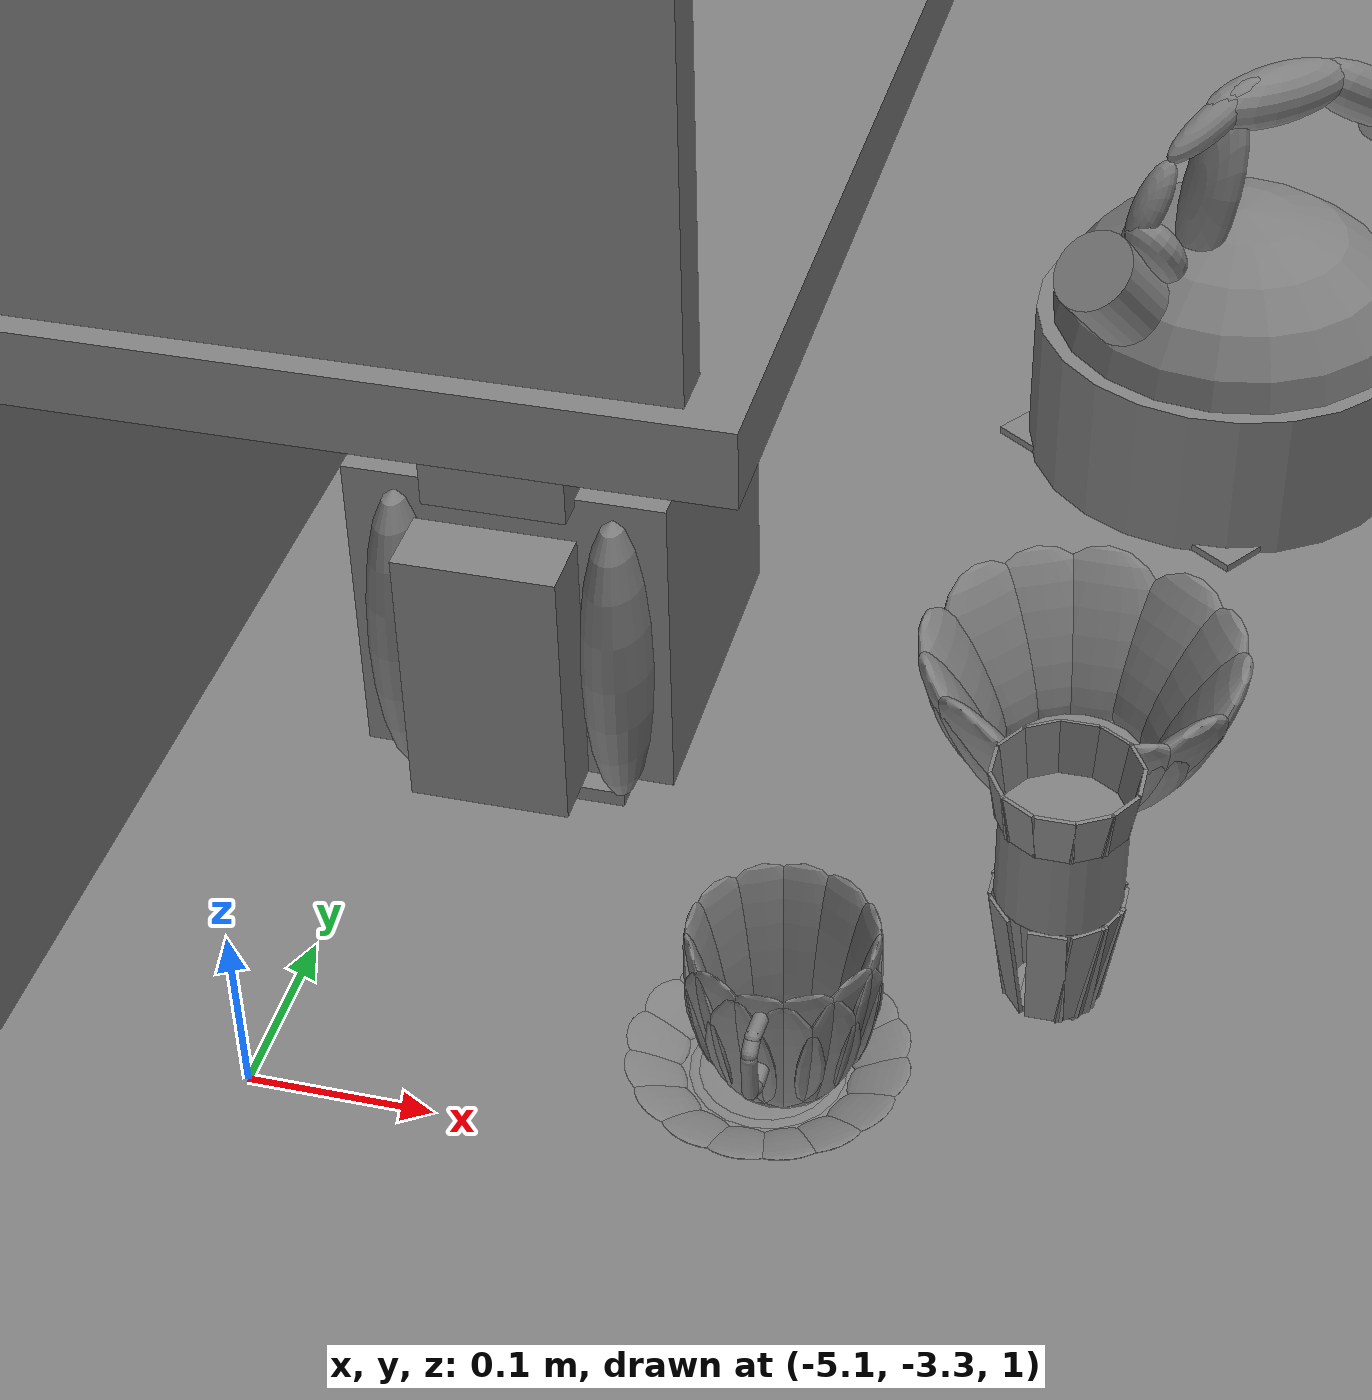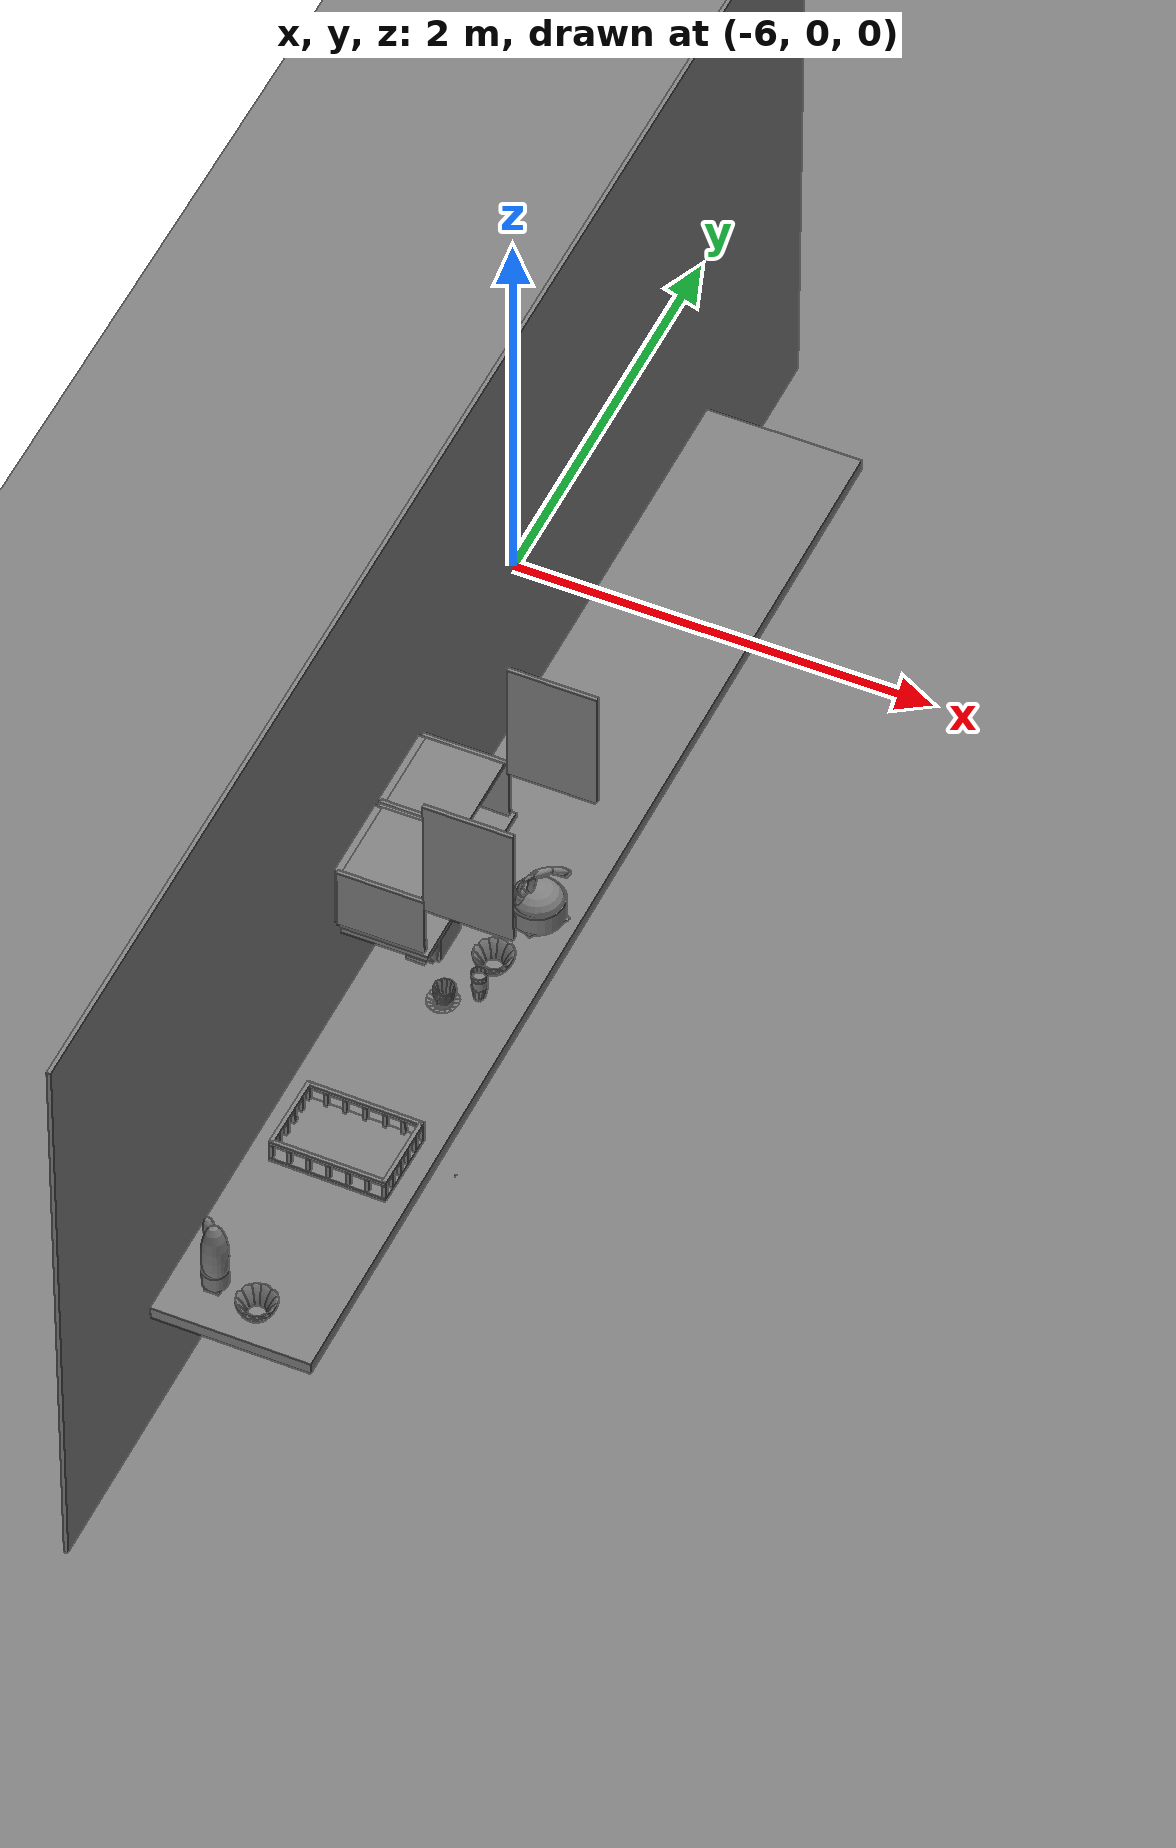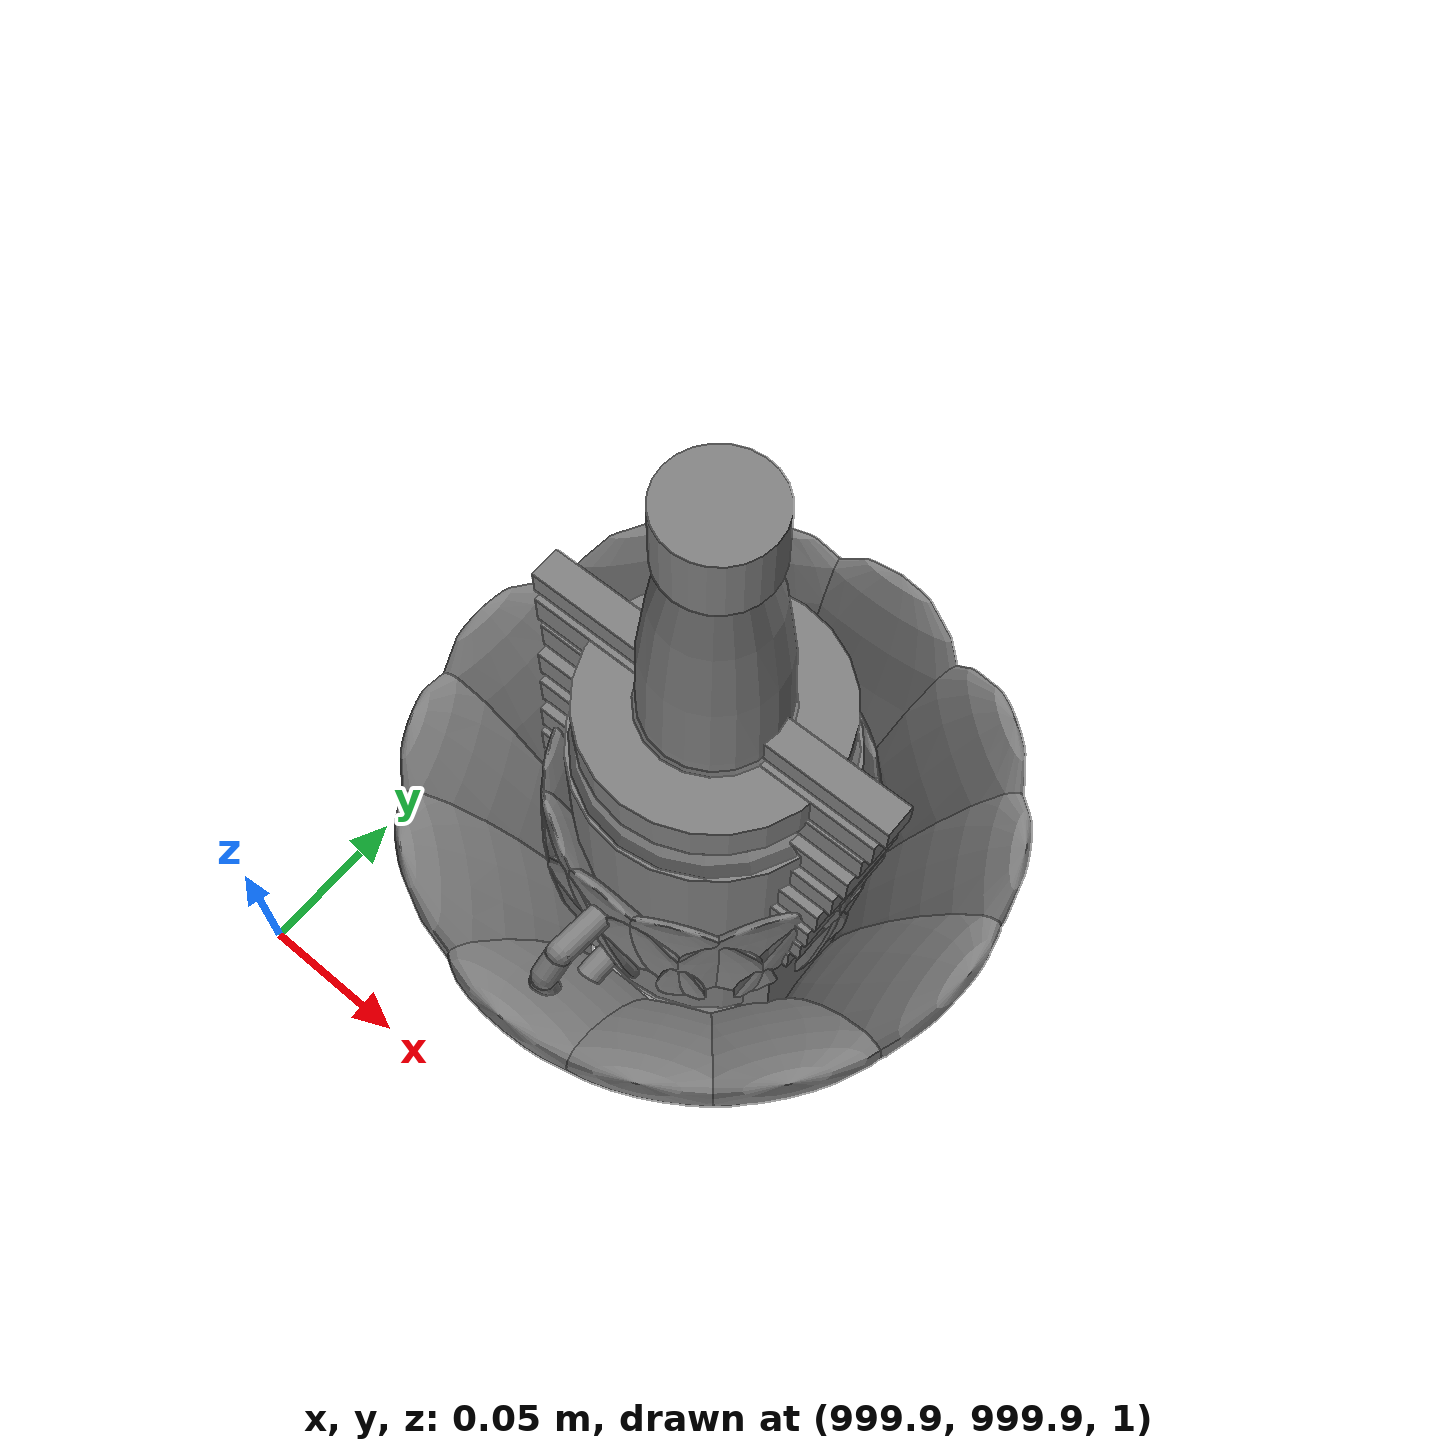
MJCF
<mujoco>
    <option gravity="0.000000000 0.000000000 -9.810000420" timestep="0.0049999999" integrator="implicitfast" density="9.8000002" viscosity="1.8000001e-05" noslip_iterations="10" iterations="100" sdf_iterations="50">
        <flag multiccd="disable"/>
    </option>
    <size memory="1000M"/>
    <compiler coordinate="local"/>
    <worldbody>
        <light cutoff="30" pos="0 1 1" dir="0 -1 -2"/>
        <light cutoff="30" pos="0 -1 1" dir="0 1 -2"/>
        <body pos="-5.020127296 -2.953741550 1.135127425" euler="89.999946594 0.000000000 0.000000000" name="Interactive Objcets_Bread">
            <geom contype="1" conaffinity="1" density="1000" type="box" material="" rgba="0.500000000 0.500000000 0.500000000 1.000000000" solimp="0.899999976 0.949999988 0.001000000" friction="1.000000000 0.005000000 0.000100000" solref="0.020000000 1.000000000" margin="0" condim="3" group="0" pos="-0.008702755 -0.017670274 -0.135069147" quat="0.707107067 -0.707106471 0.000000021 -0.000000021" size="0.045000002 0.020000000 0.079999998" name="Interactive Objcets_geom_9A789F50_4534_4860_B1EF_CD7BCDC0768B"/>
            <geom contype="1" conaffinity="1" density="1000" type="box" material="" rgba="0.500000000 0.500000000 0.500000000 1.000000000" solimp="0.899999976 0.949999988 0.001000000" friction="1.000000000 0.005000000 0.000100000" solref="0.020000000 1.000000000" margin="0" condim="3" group="0" pos="0.033925056 -0.123201847 0.086778767" quat="0.707107067 -0.707106471 0.000000021 -0.000000021" size="0.020000000 0.020000000 0.005000000" name="Interactive Objcets_geom_F9D691F0_FDE4_4409_B488_54FE6C91793D"/>
            <geom contype="1" conaffinity="1" density="1000" type="box" material="" rgba="0.500000000 0.500000000 0.500000000 1.000000000" solimp="0.899999976 0.949999988 0.001000000" friction="1.000000000 0.005000000 0.000100000" solref="0.020000000 1.000000000" margin="0" condim="3" group="0" pos="-0.008702755 -0.016588926 0.000174277" quat="0.707107067 -0.707106471 0.000000021 -0.000000021" size="0.090000004 0.100000001 0.094999999" name="Interactive Objcets_geom_2CC26682_155C_414A_A0E5_D6D6FB2EB99C"/>
            <geom contype="1" conaffinity="1" density="1000" type="ellipsoid" material="" rgba="0.500000000 0.500000000 0.500000000 1.000000000" solimp="0.899999976 0.949999988 0.001000000" friction="1.000000000 0.005000000 0.000100000" solref="0.020000000 1.000000000" margin="0" condim="3" group="0" pos="-0.067312241 -0.026057482 -0.101716787" quat="0.707107067 -0.707106471 0.000000021 -0.000000021" size="0.020000000 0.029999999 0.094999999" name="Interactive Objcets_geom_05791F58_954D_4454_BD9D_C56CC472E47C"/>
            <geom contype="1" conaffinity="1" density="1000" type="ellipsoid" material="" rgba="0.500000000 0.500000000 0.500000000 1.000000000" solimp="0.899999976 0.949999988 0.001000000" friction="1.000000000 0.005000000 0.000100000" solref="0.020000000 1.000000000" margin="0" condim="3" group="0" pos="0.052222252 -0.026057363 0.101459242" quat="0.707107067 -0.707106471 0.000000021 -0.000000021" size="0.020000000 0.029999999 0.094999999" name="Interactive Objcets_geom_C68988E7_AA82_4150_A67D_9D16E6597F5A"/>
            <geom contype="1" conaffinity="1" density="1000" type="box" material="" rgba="0.500000000 0.500000000 0.500000000 1.000000000" solimp="0.899999976 0.949999988 0.001000000" friction="1.000000000 0.005000000 0.000100000" solref="0.020000000 1.000000000" margin="0" condim="3" group="0" pos="-0.050020695 -0.123201847 0.086778767" quat="0.707107067 -0.707106471 0.000000021 -0.000000021" size="0.020000000 0.020000000 0.005000000" name="Interactive Objcets_geom_2DA77156_38BE_4EC6_89F1_E4602646CC9F"/>
            <geom contype="1" conaffinity="1" density="1000" type="box" material="" rgba="0.500000000 0.500000000 0.500000000 1.000000000" solimp="0.899999976 0.949999988 0.001000000" friction="1.000000000 0.005000000 0.000100000" solref="0.020000000 1.000000000" margin="0" condim="3" group="0" pos="0.033925056 -0.123201728 -0.092369899" quat="0.707107067 -0.707106471 0.000000021 -0.000000021" size="0.020000000 0.020000000 0.005000000" name="Interactive Objcets_geom_3DB5E2FC_0E19_4DED_8E1B_F7AF079943F9"/>
            <geom contype="1" conaffinity="1" density="1000" type="ellipsoid" material="" rgba="0.500000000 0.500000000 0.500000000 1.000000000" solimp="0.899999976 0.949999988 0.001000000" friction="1.000000000 0.005000000 0.000100000" solref="0.020000000 1.000000000" margin="0" condim="3" group="0" pos="-0.069190502 -0.026057363 0.101458766" quat="0.707107067 -0.707106471 0.000000021 -0.000000021" size="0.020000000 0.029999999 0.094999999" name="Interactive Objcets_geom_7DF1C28D_9C86_4FB5_9F4D_C307A7DB43F3"/>
            <geom contype="1" conaffinity="1" density="1000" type="box" material="" rgba="0.500000000 0.500000000 0.500000000 1.000000000" solimp="0.899999976 0.949999988 0.001000000" friction="1.000000000 0.005000000 0.000100000" solref="0.020000000 1.000000000" margin="0" condim="3" group="0" pos="-0.008702755 -0.017670155 0.134585604" quat="0.707107067 -0.707106471 0.000000021 -0.000000021" size="0.045000002 0.020000000 0.079999998" name="Interactive Objcets_geom_CB4EBC9C_AA88_4131_98B1_6C4267CD9248"/>
            <geom contype="1" conaffinity="1" density="1000" type="box" material="" rgba="0.500000000 0.500000000 0.500000000 1.000000000" solimp="0.899999976 0.949999988 0.001000000" friction="1.000000000 0.005000000 0.000100000" solref="0.020000000 1.000000000" margin="0" condim="3" group="0" pos="-0.050020695 -0.123201728 -0.092370376" quat="0.707107067 -0.707106471 0.000000021 -0.000000021" size="0.020000000 0.020000000 0.005000000" name="Interactive Objcets_geom_645E4BCB_08EE_4540_ADDD_D83BDFD46A89"/>
            <geom contype="1" conaffinity="1" density="1000" type="box" material="" rgba="0.500000000 0.500000000 0.500000000 1.000000000" solimp="0.899999976 0.949999988 0.001000000" friction="1.000000000 0.005000000 0.000100000" solref="0.020000000 1.000000000" margin="0" condim="3" group="0" pos="-0.008702755 0.104617000 -0.003706597" quat="0.707107067 -0.707106471 0.000000021 -0.000000021" size="0.039999999 0.119999997 0.030999999" name="Interactive Objcets_geom_DF6D0763_ED02_4CA2_9DF4_F98617FCFACD"/>
            <geom contype="1" conaffinity="1" density="1000" type="ellipsoid" material="" rgba="0.500000000 0.500000000 0.500000000 1.000000000" solimp="0.899999976 0.949999988 0.001000000" friction="1.000000000 0.005000000 0.000100000" solref="0.020000000 1.000000000" margin="0" condim="3" group="0" pos="0.052222252 -0.026057243 -0.106481344" quat="0.707107067 -0.707106471 0.000000021 -0.000000021" size="0.020000000 0.029999999 0.094999999" name="Interactive Objcets_geom_D8AD05D3_92C6_443E_A924_098D7248410D"/>
            <freejoint name="Interactive Objcets_Bread"/>
        </body>
        <body pos="1000.000000000 1000.000000000 1.000000000" euler="0.000000000 0.000000000 0.000000000" name="openloong_gripper_2f85_fix_base_usda_coffeecup_white_kps">
            <geom contype="1" conaffinity="1" density="1000" type="capsule" material="" rgba="0.500000000 0.500000000 0.500000000 1.000000000" solimp="0.899999976 0.949999988 0.001000000" friction="1.000000000 0.005000000 0.000100000" solref="0.020000000 1.000000000" margin="0" condim="3" group="0" pos="-0.000854492 -0.065795898 0.050029993" quat="0.343559504 -0.613204718 0.626912475 0.336047262" size="0.004000000 0.005000000 1.000000000" name="openloong_gripper_2f85_fix_base_usda_geom_DF6122B3_4CFE_4487_AB6E_C4193D9B8C9E"/>
            <geom contype="1" conaffinity="1" density="1000" type="ellipsoid" material="" rgba="0.500000000 0.500000000 0.500000000 1.000000000" solimp="0.899999976 0.949999988 0.001000000" friction="1.000000000 0.005000000 0.000100000" solref="0.020000000 1.000000000" margin="0" condim="3" group="0" pos="-0.000793457 -0.038452148 0.048040152" quat="0.711656272 0.066323131 -0.067805752 0.696095467" size="0.005000000 0.029999999 0.048999999" name="openloong_gripper_2f85_fix_base_usda_geom_C3BC689C_3385_4115_9754_F11B5BC1A973"/>
            <geom contype="1" conaffinity="1" density="1000" type="ellipsoid" material="" rgba="0.500000000 0.500000000 0.500000000 1.000000000" solimp="0.899999976 0.949999988 0.001000000" friction="1.000000000 0.005000000 0.000100000" solref="0.020000000 1.000000000" margin="0" condim="3" group="0" pos="0.037719727 -0.001892090 0.048040152" quat="0.995387912 0.001371633 0.094835162 -0.014391154" size="0.005000000 0.029999999 0.048999999" name="openloong_gripper_2f85_fix_base_usda_geom_2A09666A_B751_453B_86F7_8AB932395CD2"/>
            <geom contype="1" conaffinity="1" density="1000" type="ellipsoid" material="" rgba="0.500000000 0.500000000 0.500000000 1.000000000" solimp="0.899999976 0.949999988 0.001000000" friction="1.000000000 0.005000000 0.000100000" solref="0.020000000 1.000000000" margin="0" condim="3" group="0" pos="0.033996582 0.015502930 0.048040152" quat="0.970659733 -0.021051638 0.092478797 0.220962167" size="0.005000000 0.029999999 0.048999999" name="openloong_gripper_2f85_fix_base_usda_geom_3BE5CEAE_2BCB_45B2_8555_214427E117CA"/>
            <geom contype="1" conaffinity="1" density="1000" type="box" material="" rgba="0.500000000 0.500000000 0.500000000 1.000000000" solimp="0.899999976 0.949999988 0.001000000" friction="1.000000000 0.005000000 0.000100000" solref="0.020000000 1.000000000" margin="0" condim="3" group="0" pos="0.000793457 -0.000183105 0.000156164" quat="0.714879215 0.000000000 0.000000000 0.699247897" size="0.020000000 0.020000000 0.002000000" name="openloong_gripper_2f85_fix_base_usda_geom_4A1403C1_AA18_4F8B_B993_314ED56CB2C2"/>
            <geom contype="1" conaffinity="1" density="1000" type="ellipsoid" material="" rgba="0.500000000 0.500000000 0.500000000 1.000000000" solimp="0.899999976 0.949999988 0.001000000" friction="1.000000000 0.005000000 0.000100000" solref="0.020000000 1.000000000" margin="0" condim="3" group="0" pos="-0.019409180 -0.033081055 0.048040152" quat="0.866879702 0.046630561 -0.082595348 0.489411235" size="0.005000000 0.029999999 0.048999999" name="openloong_gripper_2f85_fix_base_usda_geom_16D5BAAB_A476_41C5_A955_991A31F5D2F2"/>
            <geom contype="1" conaffinity="1" density="1000" type="ellipsoid" material="" rgba="0.500000000 0.500000000 0.500000000 1.000000000" solimp="0.899999976 0.949999988 0.001000000" friction="1.000000000 0.005000000 0.000100000" solref="0.020000000 1.000000000" margin="0" condim="3" group="0" pos="-0.016052246 0.033264160 0.048040152" quat="0.840792537 -0.050782297 -0.080109790 -0.532983541" size="0.005000000 0.029999999 0.048999999" name="openloong_gripper_2f85_fix_base_usda_geom_5545A686_B0B8_4E7B_BDAB_B562DF86E278"/>
            <geom contype="1" conaffinity="1" density="1000" type="capsule" material="" rgba="0.500000000 0.500000000 0.500000000 1.000000000" solimp="0.899999976 0.949999988 0.001000000" friction="1.000000000 0.005000000 0.000100000" solref="0.020000000 1.000000000" margin="0" condim="3" group="0" pos="-0.000549316 -0.053527832 0.046825886" quat="0.505496025 -0.494442940 0.505495846 0.494442940" size="0.004000000 0.005000000 1.000000000" name="openloong_gripper_2f85_fix_base_usda_geom_10955384_889D_4588_81EA_E842A0C984FC"/>
            <geom contype="1" conaffinity="1" density="1000" type="ellipsoid" material="" rgba="0.500000000 0.500000000 0.500000000 1.000000000" solimp="0.899999976 0.949999988 0.001000000" friction="1.000000000 0.005000000 0.000100000" solref="0.020000000 1.000000000" margin="0" condim="3" group="0" pos="-0.032104492 0.018920898 0.048040152" quat="0.958129764 -0.025742561 -0.091288343 -0.270168930" size="0.005000000 0.029999999 0.048999999" name="openloong_gripper_2f85_fix_base_usda_geom_A280A4B7_58B6_45FE_AA61_5AB6EEB9A3F0"/>
            <geom contype="1" conaffinity="1" density="1000" type="ellipsoid" material="" rgba="0.500000000 0.500000000 0.500000000 1.000000000" solimp="0.899999976 0.949999988 0.001000000" friction="1.000000000 0.005000000 0.000100000" solref="0.020000000 1.000000000" margin="0" condim="3" group="0" pos="-0.037597656 0.000305176 0.048040152" quat="0.995387554 -0.001371440 -0.094839431 -0.014389008" size="0.005000000 0.029999999 0.048999999" name="openloong_gripper_2f85_fix_base_usda_geom_D0A275CD_4F5E_4CFC_B399_1C81AEC1A2D9"/>
            <geom contype="1" conaffinity="1" density="1000" type="capsule" material="" rgba="0.500000000 0.500000000 0.500000000 1.000000000" solimp="0.899999976 0.949999988 0.001000000" friction="1.000000000 0.005000000 0.000100000" solref="0.020000000 1.000000000" margin="0" condim="3" group="0" pos="-0.000366211 -0.043762207 0.044118762" quat="0.260488123 -0.651174724 0.665731549 0.254792154" size="0.004000000 0.003000000 1.000000000" name="openloong_gripper_2f85_fix_base_usda_geom_DE6B8401_C904_4291_95B2_01F1A9EBC354"/>
            <geom contype="1" conaffinity="1" density="1000" type="capsule" material="" rgba="0.500000000 0.500000000 0.500000000 1.000000000" solimp="0.899999976 0.949999988 0.001000000" friction="1.000000000 0.005000000 0.000100000" solref="0.020000000 1.000000000" margin="0" condim="3" group="0" pos="-0.000915527 -0.068542480 0.082936406" quat="0.624995589 -0.339446366 0.347034454 0.611329615" size="0.004000000 0.004000000 1.000000000" name="openloong_gripper_2f85_fix_base_usda_geom_BFD8C8A0_7DF8_42CD_923A_E1BC7E7DDFA2"/>
            <geom contype="1" conaffinity="1" density="1000" type="ellipsoid" material="" rgba="0.500000000 0.500000000 0.500000000 1.000000000" solimp="0.899999976 0.949999988 0.001000000" friction="1.000000000 0.005000000 0.000100000" solref="0.020000000 1.000000000" margin="0" condim="3" group="0" pos="0.016113281 -0.034851074 0.048040152" quat="0.840793252 0.050779939 0.080106191 -0.532983422" size="0.005000000 0.029999999 0.048999999" name="openloong_gripper_2f85_fix_base_usda_geom_65A370DB_CCD9_4AE3_947E_C0B536D53143"/>
            <geom contype="1" conaffinity="1" density="1000" type="ellipsoid" material="" rgba="0.500000000 0.500000000 0.500000000 1.000000000" solimp="0.899999976 0.949999988 0.001000000" friction="1.000000000 0.005000000 0.000100000" solref="0.020000000 1.000000000" margin="0" condim="3" group="0" pos="0.000854492 0.036865234 0.048040152" quat="0.711656570 -0.066320375 0.067802906 0.696095705" size="0.005000000 0.029999999 0.048999999" name="openloong_gripper_2f85_fix_base_usda_geom_DFDF3DED_9850_4A31_9A03_9C7CBA351CDC"/>
            <geom contype="1" conaffinity="1" density="1000" type="ellipsoid" material="" rgba="0.500000000 0.500000000 0.500000000 1.000000000" solimp="0.899999976 0.949999988 0.001000000" friction="1.000000000 0.005000000 0.000100000" solref="0.020000000 1.000000000" margin="0" condim="3" group="0" pos="-0.033935547 -0.017089844 0.048040152" quat="0.970659137 0.021052625 -0.092483103 0.220962465" size="0.005000000 0.029999999 0.048999999" name="openloong_gripper_2f85_fix_base_usda_geom_88875B5B_702E_4FE8_A16A_44852D93AD20"/>
            <geom contype="1" conaffinity="1" density="1000" type="ellipsoid" material="" rgba="0.500000000 0.500000000 0.500000000 1.000000000" solimp="0.899999976 0.949999988 0.001000000" friction="1.000000000 0.005000000 0.000100000" solref="0.020000000 1.000000000" margin="0" condim="3" group="0" pos="0.019531250 0.031494141 0.048040152" quat="0.866880119 -0.046628602 0.082591817 0.489411235" size="0.005000000 0.029999999 0.048999999" name="openloong_gripper_2f85_fix_base_usda_geom_E1048315_F374_4231_A111_6BD4CC2CA837"/>
            <geom contype="1" conaffinity="1" density="1000" type="ellipsoid" material="" rgba="0.500000000 0.500000000 0.500000000 1.000000000" solimp="0.899999976 0.949999988 0.001000000" friction="1.000000000 0.005000000 0.000100000" solref="0.020000000 1.000000000" margin="0" condim="3" group="0" pos="0.032165527 -0.020507812 0.048040152" quat="0.958128154 0.025740955 0.091285400 -0.270175666" size="0.005000000 0.029999999 0.048999999" name="openloong_gripper_2f85_fix_base_usda_geom_53E24F3C_F54D_4F6D_8981_732E7AA4ADB1"/>
            <geom contype="1" conaffinity="1" density="1000" type="capsule" material="" rgba="0.500000000 0.500000000 0.500000000 1.000000000" solimp="0.899999976 0.949999988 0.001000000" friction="1.000000000 0.005000000 0.000100000" solref="0.020000000 1.000000000" margin="0" condim="3" group="0" pos="-0.000610352 -0.056823730 0.083572865" quat="0.452654332 -0.541215360 0.553313971 0.442756712" size="0.004000000 0.009000000 1.000000000" name="openloong_gripper_2f85_fix_base_usda_geom_64ABC63A_ECAC_42E0_9FAE_447520EA8481"/>
            <geom contype="1" conaffinity="1" density="1000" type="ellipsoid" material="" rgba="0.500000000 0.500000000 0.500000000 1.000000000" solimp="0.899999976 0.949999988 0.001000000" friction="1.000000000 0.005000000 0.000100000" solref="0.020000000 1.000000000" margin="0" condim="3" group="0" pos="0.000061035 -0.000183105 0.001848221" quat="0.714879215 0.000000000 0.000000000 0.699247897" size="0.029999999 0.029999999 0.001000000" name="openloong_gripper_2f85_fix_base_usda_geom_36857EFC_3892_4C7A_98A8_82F928D1A8D6"/>
            <geom contype="1" conaffinity="1" density="1000" type="capsule" material="" rgba="0.500000000 0.500000000 0.500000000 1.000000000" solimp="0.899999976 0.949999988 0.001000000" friction="1.000000000 0.005000000 0.000100000" solref="0.020000000 1.000000000" margin="0" condim="3" group="0" pos="-0.000976562 -0.071838379 0.066101432" quat="0.031849027 -0.698553741 0.714169443 0.031152546" size="0.004000000 0.012000000 1.000000000" name="openloong_gripper_2f85_fix_base_usda_geom_72B14AEE_88FE_496A_8AD4_88ABE461ABD5"/>
            <freejoint name="openloong_gripper_2f85_fix_base_usda_coffeecup_white_kps_joint"/>
            <site size="0.005000000 0.005000000 0.005000000" rgba="0.500000000 0.500000000 0.500000000 1.000000000" pos="0.000000000 0.000000000 0.000000000" quat="0.999961913 0.008726534 0.000000000 0.000000000" group="0" type="sphere" name="openloong_gripper_2f85_fix_base_usda_coffeecup_white_kps"/>
        </body>
        <body pos="-4.080235958 -4.314333439 1.835103750" euler="8.100793839 65.335266113 168.161865234" mocap="true" name="spotlight6_SpotLight"/>
        <body pos="-3.942055225 -4.513264179 1.822806478" euler="-48.468181610 -45.824512482 -122.404281616" mocap="true" name="spotlight5_SpotLight"/>
        <body pos="1000.000000000 1000.000000000 1.000000000" euler="0.000000000 0.000000000 0.000000000" name="openloong_gripper_2f85_fix_base_usda_salt">
            <geom contype="1" conaffinity="1" density="1000" type="box" material="" rgba="0.500000000 0.500000000 0.500000000 1.000000000" solimp="0.899999976 0.949999988 0.001000000" friction="1.000000000 0.005000000 0.000100000" solref="0.020000000 1.000000000" margin="0" condim="3" group="0" pos="0.000305176 0.000000000 0.084862232" quat="1.000000000 0.000000000 0.000000000 0.000000000" size="0.048999999 0.018999999 0.005000000" name="openloong_gripper_2f85_fix_base_usda_geom_1C816FF0_F2F3_49A5_A581_50A8CF760A74"/>
            <geom contype="1" conaffinity="1" density="1000" type="box" material="" rgba="0.500000000 0.500000000 0.500000000 1.000000000" solimp="0.899999976 0.949999988 0.001000000" friction="1.000000000 0.005000000 0.000100000" solref="0.020000000 1.000000000" margin="0" condim="3" group="0" pos="0.000305176 0.000000000 0.104564309" quat="1.000000000 0.000000000 0.000000000 0.000000000" size="0.052000001 0.014000000 0.005000000" name="openloong_gripper_2f85_fix_base_usda_geom_8839B630_AB61_4F58_9079_E979F4D1A972"/>
            <geom contype="1" conaffinity="1" density="1000" type="box" material="" rgba="0.500000000 0.500000000 0.500000000 1.000000000" solimp="0.899999976 0.949999988 0.001000000" friction="1.000000000 0.005000000 0.000100000" solref="0.020000000 1.000000000" margin="0" condim="3" group="0" pos="0.000305176 0.000000000 0.114487171" quat="1.000000000 0.000000000 0.000000000 0.000000000" size="0.054000001 0.011500000 0.005000000" name="openloong_gripper_2f85_fix_base_usda_geom_086602DA_38E2_4FB1_9026_009A53805AE4"/>
            <geom contype="1" conaffinity="1" density="1000" type="box" material="" rgba="0.500000000 0.500000000 0.500000000 1.000000000" solimp="0.899999976 0.949999988 0.001000000" friction="1.000000000 0.005000000 0.000100000" solref="0.020000000 1.000000000" margin="0" condim="3" group="0" pos="0.000305176 0.000000000 0.075103164" quat="1.000000000 0.000000000 0.000000000 0.000000000" size="0.048000000 0.020000000 0.005000000" name="openloong_gripper_2f85_fix_base_usda_geom_0EFE2989_3D52_447F_BEE7_B910C6DCAF82"/>
            <geom contype="1" conaffinity="1" density="1000" type="box" material="" rgba="0.500000000 0.500000000 0.500000000 1.000000000" solimp="0.899999976 0.949999988 0.001000000" friction="1.000000000 0.005000000 0.000100000" solref="0.020000000 1.000000000" margin="0" condim="3" group="0" pos="0.000305176 0.000000000 0.134892464" quat="1.000000000 0.000000000 0.000000000 0.000000000" size="0.057000000 0.007000000 0.005000000" name="openloong_gripper_2f85_fix_base_usda_geom_6D26A5C5_7437_4DA5_8E43_F8BB0BA7FD39"/>
            <geom contype="1" conaffinity="1" density="1000" type="box" material="" rgba="0.500000000 0.500000000 0.500000000 1.000000000" solimp="0.899999976 0.949999988 0.001000000" friction="1.000000000 0.005000000 0.000100000" solref="0.020000000 1.000000000" margin="0" condim="3" group="0" pos="0.000305176 0.000000000 0.094920278" quat="1.000000000 0.000000000 0.000000000 0.000000000" size="0.050000001 0.017000001 0.005000000" name="openloong_gripper_2f85_fix_base_usda_geom_11F89F0D_53AD_475F_9D21_A9D8D0AE0DB7"/>
            <geom contype="1" conaffinity="1" density="1000" type="box" material="" rgba="0.500000000 0.500000000 0.500000000 1.000000000" solimp="0.899999976 0.949999988 0.001000000" friction="1.000000000 0.005000000 0.000100000" solref="0.020000000 1.000000000" margin="0" condim="3" group="0" pos="0.000305176 0.000000000 0.065204859" quat="1.000000000 0.000000000 0.000000000 0.000000000" size="0.045000002 0.021000000 0.005000000" name="openloong_gripper_2f85_fix_base_usda_geom_8A84CDBA_F44E_416A_9B2F_4515E5579BBA"/>
            <geom contype="1" conaffinity="1" density="1000" type="box" material="" rgba="0.500000000 0.500000000 0.500000000 1.000000000" solimp="0.899999976 0.949999988 0.001000000" friction="1.000000000 0.005000000 0.000100000" solref="0.020000000 1.000000000" margin="0" condim="3" group="0" pos="0.000305176 0.000000000 0.144135714" quat="1.000000000 0.000000000 0.000000000 0.000000000" size="0.059000000 0.005000000 0.004000000" name="openloong_gripper_2f85_fix_base_usda_geom_F1CC46B1_3498_489D_AFD1_56039AB1A127"/>
            <geom contype="1" conaffinity="1" density="1000" type="box" material="" rgba="0.500000000 0.500000000 0.500000000 1.000000000" solimp="0.899999976 0.949999988 0.001000000" friction="1.000000000 0.005000000 0.000100000" solref="0.020000000 1.000000000" margin="0" condim="3" group="0" pos="0.000000000 0.000000000 0.031593561" quat="1.000000000 0.000000000 0.000000000 0.000000000" size="0.041999999 0.024000000 0.029999999" name="openloong_gripper_2f85_fix_base_usda_geom_0323B24E_2D72_4595_A05C_D025753111BA"/>
            <geom contype="1" conaffinity="1" density="1000" type="box" material="" rgba="0.500000000 0.500000000 0.500000000 1.000000000" solimp="0.899999976 0.949999988 0.001000000" friction="1.000000000 0.005000000 0.000100000" solref="0.020000000 1.000000000" margin="0" condim="3" group="0" pos="0.000305176 0.000000000 0.124608755" quat="1.000000000 0.000000000 0.000000000 0.000000000" size="0.055000000 0.008000000 0.005000000" name="openloong_gripper_2f85_fix_base_usda_geom_C2AE15C9_2915_47E7_AB70_9EA85AE75485"/>
            <freejoint name="openloong_gripper_2f85_fix_base_usda_salt_joint"/>
            <site size="0.005000000 0.005000000 0.005000000" rgba="0.500000000 0.500000000 0.500000000 1.000000000" pos="0.000000000 0.000000000 0.000000000" quat="1.000000000 0.000000000 0.000000000 0.000000000" group="0" type="sphere" name="openloong_gripper_2f85_fix_base_usda_saltsite"/>
        </body>
        <body pos="0.000000000 0.000000000 0.000000000" euler="0.000000000 0.000000000 0.000000000" name="Static Objcets_Static Objcets">
            <geom contype="1" conaffinity="1" density="1000" type="box" material="" rgba="0.500000000 0.500000000 0.500000000 1.000000000" solimp="0.899999976 0.949999988 0.001000000" friction="1.000000000 0.005000000 0.000100000" solref="0.020000000 1.000000000" margin="0" condim="3" group="0" pos="-5.189302921 -3.293644905 1.760152459" quat="0.707107067 0.707106471 0.000000000 0.000000000" size="0.025000000 0.159999996 0.200000003" name="Static Objcets_geom_76DDDD66_169D_4A67_B07E_101F940B9F22"/>
            <geom contype="1" conaffinity="1" density="1000" type="box" material="" rgba="0.500000000 0.500000000 0.500000000 1.000000000" solimp="0.899999976 0.949999988 0.001000000" friction="1.000000000 0.005000000 0.000100000" solref="0.020000000 1.000000000" margin="0" condim="3" group="0" pos="-4.999745846 -3.497932911 1.764780521" quat="0.707107067 0.707106471 0.000000000 0.000000000" size="0.200000003 0.159999996 0.010000000" name="Static Objcets_geom_B4A69826_D020_4A39_95EA_16E1178842B9"/>
            <geom contype="1" conaffinity="1" density="1000" type="box" material="" rgba="0.500000000 0.500000000 0.500000000 1.000000000" solimp="0.899999976 0.949999988 0.001000000" friction="1.000000000 0.005000000 0.000100000" solref="0.020000000 1.000000000" margin="0" condim="3" group="0" pos="-4.979488373 -3.297635794 1.591412544" quat="0.707106829 0.707106709 0.000000000 0.000000000" size="0.200000003 0.015000000 0.219999999" name="Static Objcets_geom_BBBA36BA_EDAC_452B_97B2_F9D7C909DFF7"/>
            <geom contype="1" conaffinity="1" density="1000" type="box" material="" rgba="0.500000000 0.500000000 0.500000000 1.000000000" solimp="0.899999976 0.949999988 0.001000000" friction="1.000000000 0.005000000 0.000100000" solref="0.020000000 1.000000000" margin="0" condim="3" group="0" pos="-4.999745846 -3.087441683 1.763863802" quat="0.707107067 0.707106471 0.000000000 0.000000000" size="0.200000003 0.159999996 0.010000000" name="Static Objcets_geom_2F81180A_E4FD_4207_9704_FB549B6170FC"/>
            <geom contype="1" conaffinity="1" density="1000" type="box" material="" rgba="0.500000000 0.500000000 0.500000000 1.000000000" solimp="0.899999976 0.949999988 0.001000000" friction="1.000000000 0.005000000 0.000100000" solref="0.020000000 1.000000000" margin="0" condim="3" group="0" pos="-5.000125408 -3.294431210 1.913951039" quat="0.707107067 0.707106471 0.000000000 0.000000000" size="0.180000007 0.010000000 0.200000003" name="Static Objcets_geom_4548BED6_0E49_4AAA_A630_BDC43C41FFE4"/>
            <geom contype="1" conaffinity="1" density="1000" type="box" material="" rgba="0.500000000 0.500000000 0.500000000 1.000000000" solimp="0.899999976 0.949999988 0.001000000" friction="1.000000000 0.005000000 0.000100000" solref="0.020000000 1.000000000" margin="0" condim="3" group="0" pos="-4.873187065 -2.461376429 0.977675021" quat="0.707107067 0.707106471 0.000000000 0.000000000" size="0.370000005 0.029999999 2.799999952" name="Static Objcets_geom_BDAE0E99_C90F_4905_8DF4_C6E9725D9ED8"/>
            <geom contype="1" conaffinity="1" density="1000" type="box" material="" rgba="0.500000000 0.500000000 0.500000000 1.000000000" solimp="0.899999976 0.949999988 0.001000000" friction="1.000000000 0.005000000 0.000100000" solref="0.020000000 1.000000000" margin="0" condim="3" group="0" pos="-5.244853973 -2.375543594 1.820221663" quat="0.707107008 0.707106531 0.000000000 0.000000000" size="0.010000000 1.500000000 3.700000048" name="Static Objcets_geom_8E3A2D07_C9D4_4972_961B_3F37AFA3D4C7"/>
            <geom contype="1" conaffinity="1" density="1000" type="box" material="" rgba="0.500000000 0.500000000 0.500000000 1.000000000" solimp="0.899999976 0.949999988 0.001000000" friction="1.000000000 0.005000000 0.000100000" solref="0.020000000 1.000000000" margin="0" condim="3" group="0" pos="-0.720102787 0.222944975 -1.102830648" quat="0.000000954 1.000000000 0.000000000 0.000000000" size="8.000000000 8.000000000 0.010000000" name="Static Objcets_geom_ACBA9017_2942_4EF9_886F_67B50BBFDA3F"/>
            <geom contype="1" conaffinity="1" density="1000" type="box" material="" rgba="0.500000000 0.500000000 0.500000000 1.000000000" solimp="0.899999976 0.949999988 0.001000000" friction="1.000000000 0.005000000 0.000100000" solref="0.020000000 1.000000000" margin="0" condim="3" group="0" pos="-4.999745846 -2.653569937 1.764779806" quat="0.707107067 0.707106471 0.000000000 0.000000000" size="0.200000003 0.159999996 0.010000000" name="Static Objcets_geom_6F8F8ED8_88EA_45C8_87C4_9F7CCFF1005A"/>
            <geom contype="1" conaffinity="1" density="1000" type="box" material="" rgba="0.500000000 0.500000000 0.500000000 1.000000000" solimp="0.899999976 0.949999988 0.001000000" friction="1.000000000 0.005000000 0.000100000" solref="0.020000000 1.000000000" margin="0" condim="3" group="0" pos="-5.000125408 -2.861802340 1.913950682" quat="0.707107067 0.707106471 0.000000000 0.000000000" size="0.180000007 0.010000000 0.200000003" name="Static Objcets_geom_F7B6A77C_51DA_4DD1_B976_D619AB7054E1"/>
            <geom contype="1" conaffinity="1" density="1000" type="box" material="" rgba="0.500000000 0.500000000 0.500000000 1.000000000" solimp="0.899999976 0.949999988 0.001000000" friction="1.000000000 0.005000000 0.000100000" solref="0.020000000 1.000000000" margin="0" condim="3" group="0" pos="-5.189302921 -2.861564636 1.760152102" quat="0.707107067 0.707106471 0.000000000 0.000000000" size="0.025000000 0.159999996 0.200000003" name="Static Objcets_geom_1220B216_1E7E_482C_9572_E071D81D2644"/>
            <geom contype="1" conaffinity="1" density="1000" type="box" material="" rgba="0.500000000 0.500000000 0.500000000 1.000000000" solimp="0.899999976 0.949999988 0.001000000" friction="1.000000000 0.005000000 0.000100000" solref="0.020000000 1.000000000" margin="0" condim="3" group="0" pos="-4.979488373 -2.855390549 1.591412187" quat="0.707106709 0.707106769 0.000000000 0.000000000" size="0.200000003 0.015000000 0.219999999" name="Static Objcets_geom_4785FBE2_CDAA_4147_87E8_5041FA2197D4"/>
            <geom contype="1" conaffinity="1" density="1000" type="box" material="" rgba="0.500000000 0.500000000 0.500000000 1.000000000" solimp="0.899999976 0.949999988 0.001000000" friction="1.000000000 0.005000000 0.000100000" solref="0.020000000 1.000000000" margin="0" condim="3" group="0" pos="-4.999745846 -3.066934109 1.765979409" quat="0.707107067 0.707106471 0.000000000 0.000000000" size="0.200000003 0.159999996 0.010000000" name="Static Objcets_geom_B42F675E_D223_4FCF_9942_AF72CA16F0A7"/>
        </body>
        <body pos="-4.705342293 -3.169416904 1.103703976" euler="0.000000000 0.000000000 0.000000000" name="Interactive Objcets_cup_02">
            <geom contype="1" conaffinity="1" density="1000" type="box" material="" rgba="0.500000000 0.500000000 0.500000000 1.000000000" solimp="0.899999976 0.949999988 0.001000000" friction="1.000000000 0.005000000 0.000100000" solref="0.020000000 1.000000000" margin="0" condim="3" group="0" pos="0.022285938 0.016949892 -0.037281752" quat="0.893179297 -0.070051625 0.034732576 -0.442851186" size="0.010000000 0.001000000 0.035000000" name="Interactive Objcets_geom_1CBE4BAF_F94A_4C2B_96D8_8E7A927788CD"/>
            <geom contype="1" conaffinity="1" density="1000" type="box" material="" rgba="0.500000000 0.500000000 0.500000000 1.000000000" solimp="0.899999976 0.949999988 0.001000000" friction="1.000000000 0.005000000 0.000100000" solref="0.020000000 1.000000000" margin="0" condim="3" group="0" pos="0.034549713 0.000000000 0.062637210" quat="0.704941988 -0.055288255 0.055288251 -0.704942048" size="0.010000000 0.001000000 0.015000000" name="Interactive Objcets_geom_627FC606_E5DE_4E8E_A6D9_0630DC448B08"/>
            <geom contype="1" conaffinity="1" density="1000" type="box" material="" rgba="0.500000000 0.500000000 0.500000000 1.000000000" solimp="0.899999976 0.949999988 0.001000000" friction="1.000000000 0.005000000 0.000100000" solref="0.020000000 1.000000000" margin="0" condim="3" group="0" pos="0.029378891 -0.018181801 0.062637210" quat="0.870895982 0.068302706 0.038053915 0.485208035" size="0.010000000 0.001000000 0.015000000" name="Interactive Objcets_geom_E767BCEF_CCEE_4278_AAD5_DFD776ABF23E"/>
            <geom contype="1" conaffinity="1" density="1000" type="box" material="" rgba="0.500000000 0.500000000 0.500000000 1.000000000" solimp="0.899999976 0.949999988 0.001000000" friction="1.000000000 0.005000000 0.000100000" solref="0.020000000 1.000000000" margin="0" condim="3" group="0" pos="0.000000000 -0.034549713 0.062637210" quat="0.996938646 0.078187965 0.000000000 0.000000000" size="0.010000000 0.001000000 0.015000000" name="Interactive Objcets_geom_D26B4C1A_7F19_4BE5_AC57_CC8AB2EE3297"/>
            <geom contype="1" conaffinity="1" density="1000" type="cylinder" material="" rgba="0.500000000 0.500000000 0.500000000 1.000000000" solimp="0.899999976 0.949999988 0.001000000" friction="1.000000000 0.005000000 0.000100000" solref="0.020000000 1.000000000" margin="0" condim="3" group="0" pos="0.000000000 0.000000000 0.022491097" quat="1.000000000 0.000000030 0.000000000 0.000000000" size="0.033000000 0.025000000 1.000000000" name="Interactive Objcets_geom_02A914A7_1B9F_4835_90AF_0B5BADB57DB9"/>
            <geom contype="1" conaffinity="1" density="1000" type="box" material="" rgba="0.500000000 0.500000000 0.500000000 1.000000000" solimp="0.899999976 0.949999988 0.001000000" friction="1.000000000 0.005000000 0.000100000" solref="0.020000000 1.000000000" margin="0" condim="3" group="0" pos="0.000000000 0.034549713 0.062637210" quat="0.996938646 -0.078187965 0.000000000 0.000000000" size="0.010000000 0.001000000 0.015000000" name="Interactive Objcets_geom_5FD3D831_537D_4A28_A293_4658A777095D"/>
            <geom contype="1" conaffinity="1" density="1000" type="box" material="" rgba="0.500000000 0.500000000 0.500000000 1.000000000" solimp="0.899999976 0.949999988 0.001000000" friction="1.000000000 0.005000000 0.000100000" solref="0.020000000 1.000000000" margin="0" condim="3" group="0" pos="0.011943817 0.025323629 -0.037281752" quat="0.972834349 -0.076298930 0.017089661 -0.217898533" size="0.010000000 0.001000000 0.035000000" name="Interactive Objcets_geom_0F43E250_A25C_47E4_A6FE_913D648959F5"/>
            <geom contype="1" conaffinity="1" density="1000" type="box" material="" rgba="0.500000000 0.500000000 0.500000000 1.000000000" solimp="0.899999976 0.949999988 0.001000000" friction="1.000000000 0.005000000 0.000100000" solref="0.020000000 1.000000000" margin="0" condim="3" group="0" pos="0.025214195 -0.011892319 -0.037281752" quat="0.841975451 0.066034243 0.041866414 0.533820212" size="0.010000000 0.001000000 0.035000000" name="Interactive Objcets_geom_BA3A131C_4E2A_4079_A35E_7AB9250A0D49"/>
            <geom contype="1" conaffinity="1" density="1000" type="box" material="" rgba="0.500000000 0.500000000 0.500000000 1.000000000" solimp="0.899999976 0.949999988 0.001000000" friction="1.000000000 0.005000000 0.000100000" solref="0.020000000 1.000000000" margin="0" condim="3" group="0" pos="-0.027999878 0.000000000 -0.037281752" quat="0.704941988 0.055288255 -0.055288251 -0.704942048" size="0.010000000 0.001000000 0.035000000" name="Interactive Objcets_geom_0C47D52D_6A83_4C17_A1F8_25158F17CEC9"/>
            <geom contype="1" conaffinity="1" density="1000" type="box" material="" rgba="0.500000000 0.500000000 0.500000000 1.000000000" solimp="0.899999976 0.949999988 0.001000000" friction="1.000000000 0.005000000 0.000100000" solref="0.020000000 1.000000000" margin="0" condim="3" group="0" pos="0.017436981 -0.029826880 0.062637210" quat="0.962265730 0.075468659 0.020441191 0.260636479" size="0.010000000 0.001000000 0.015000000" name="Interactive Objcets_geom_1756ADA6_D789_4BA7_8BF6_B8E2635E75DD"/>
            <geom contype="1" conaffinity="1" density="1000" type="box" material="" rgba="0.500000000 0.500000000 0.500000000 1.000000000" solimp="0.899999976 0.949999988 0.001000000" friction="1.000000000 0.005000000 0.000100000" solref="0.020000000 1.000000000" margin="0" condim="3" group="0" pos="0.029827118 0.017437220 0.062637210" quat="0.864722252 -0.067819774 0.038910985 -0.496126890" size="0.010000000 0.001000000 0.015000000" name="Interactive Objcets_geom_D4CF0673_EB2E_4076_84E3_1CF0767B3E1B"/>
            <geom contype="1" conaffinity="1" density="1000" type="box" material="" rgba="0.500000000 0.500000000 0.500000000 1.000000000" solimp="0.899999976 0.949999988 0.001000000" friction="1.000000000 0.005000000 0.000100000" solref="0.020000000 1.000000000" margin="0" condim="3" group="0" pos="0.000000000 0.027877331 -0.037281752" quat="0.996938646 -0.078187965 0.000000000 0.000000000" size="0.010000000 0.001000000 0.035000000" name="Interactive Objcets_geom_31B3D0D2_2DD7_476A_BA4E_FC1BA838E624"/>
            <geom contype="1" conaffinity="1" density="1000" type="box" material="" rgba="0.500000000 0.500000000 0.500000000 1.000000000" solimp="0.899999976 0.949999988 0.001000000" friction="1.000000000 0.005000000 0.000100000" solref="0.020000000 1.000000000" margin="0" condim="3" group="0" pos="-0.025214195 0.011891127 -0.037281752" quat="0.841975451 -0.066034243 -0.041866414 0.533820212" size="0.010000000 0.001000000 0.035000000" name="Interactive Objcets_geom_BEEC1B04_D06C_4F35_82EE_7B6C48322985"/>
            <geom contype="1" conaffinity="1" density="1000" type="box" material="" rgba="0.500000000 0.500000000 0.500000000 1.000000000" solimp="0.899999976 0.949999988 0.001000000" friction="1.000000000 0.005000000 0.000100000" solref="0.020000000 1.000000000" margin="0" condim="3" group="0" pos="-0.022286415 -0.016949654 -0.037281752" quat="0.893179297 0.070051625 -0.034732576 -0.442851186" size="0.010000000 0.001000000 0.035000000" name="Interactive Objcets_geom_20F43C52_546F_40D7_9CAC_AF6B9ACA259E"/>
            <geom contype="1" conaffinity="1" density="1000" type="box" material="" rgba="0.500000000 0.500000000 0.500000000 1.000000000" solimp="0.899999976 0.949999988 0.001000000" friction="1.000000000 0.005000000 0.000100000" solref="0.020000000 1.000000000" margin="0" condim="3" group="0" pos="-0.016875744 0.022189617 -0.037281752" quat="0.944716334 -0.074092269 -0.024973858 0.318430305" size="0.010000000 0.001000000 0.035000000" name="Interactive Objcets_geom_0BCACDDE_AEAB_4AF0_B3DB_4A04A7083E31"/>
            <geom contype="1" conaffinity="1" density="1000" type="box" material="" rgba="0.500000000 0.500000000 0.500000000 1.000000000" solimp="0.899999976 0.949999988 0.001000000" friction="1.000000000 0.005000000 0.000100000" solref="0.020000000 1.000000000" margin="0" condim="3" group="0" pos="0.018182278 0.029379368 0.062637210" quat="0.958910167 -0.075206861 0.021389510 -0.272722572" size="0.010000000 0.001000000 0.015000000" name="Interactive Objcets_geom_2D177425_AA72_4F88_84EB_A839FDBA7339"/>
            <geom contype="1" conaffinity="1" density="1000" type="box" material="" rgba="0.500000000 0.500000000 0.500000000 1.000000000" solimp="0.899999976 0.949999988 0.001000000" friction="1.000000000 0.005000000 0.000100000" solref="0.020000000 1.000000000" margin="0" condim="3" group="0" pos="0.000000000 0.000000000 -0.075536966" quat="1.000000000 0.000000000 0.000000000 0.000000000" size="0.015000000 0.015000000 0.002000000" name="Interactive Objcets_geom_0A4858CE_224E_495A_878B_D3B64129EF17"/>
            <geom contype="1" conaffinity="1" density="1000" type="box" material="" rgba="0.500000000 0.500000000 0.500000000 1.000000000" solimp="0.899999976 0.949999988 0.001000000" friction="1.000000000 0.005000000 0.000100000" solref="0.020000000 1.000000000" margin="0" condim="3" group="0" pos="-0.018181324 -0.029377937 0.062637210" quat="0.958910167 0.075206861 -0.021389510 -0.272722572" size="0.010000000 0.001000000 0.015000000" name="Interactive Objcets_geom_AD554930_1BB0_419D_959F_4B92020AB5B2"/>
            <geom contype="1" conaffinity="1" density="1000" type="box" material="" rgba="0.500000000 0.500000000 0.500000000 1.000000000" solimp="0.899999976 0.949999988 0.001000000" friction="1.000000000 0.005000000 0.000100000" solref="0.020000000 1.000000000" margin="0" condim="3" group="0" pos="0.027999878 0.000000000 -0.037281752" quat="0.704941988 -0.055288255 0.055288251 -0.704942048" size="0.010000000 0.001000000 0.035000000" name="Interactive Objcets_geom_33E770FB_7BB6_459A_82AA_31F62CA20C9B"/>
            <geom contype="1" conaffinity="1" density="1000" type="box" material="" rgba="0.500000000 0.500000000 0.500000000 1.000000000" solimp="0.899999976 0.949999988 0.001000000" friction="1.000000000 0.005000000 0.000100000" solref="0.020000000 1.000000000" margin="0" condim="3" group="0" pos="0.016875744 -0.022189379 -0.037281752" quat="0.944716334 0.074092269 0.024973858 0.318430305" size="0.010000000 0.001000000 0.035000000" name="Interactive Objcets_geom_30C23F63_86ED_41E2_A97E_C4F3967ACA1D"/>
            <geom contype="1" conaffinity="1" density="1000" type="box" material="" rgba="0.500000000 0.500000000 0.500000000 1.000000000" solimp="0.899999976 0.949999988 0.001000000" friction="1.000000000 0.005000000 0.000100000" solref="0.020000000 1.000000000" margin="0" condim="3" group="0" pos="-0.029377937 0.018182278 0.062637210" quat="0.870895982 -0.068302706 -0.038053915 0.485208035" size="0.010000000 0.001000000 0.015000000" name="Interactive Objcets_geom_FD9E2EC1_40E3_4D28_B78C_2783D806B3A9"/>
            <geom contype="1" conaffinity="1" density="1000" type="box" material="" rgba="0.500000000 0.500000000 0.500000000 1.000000000" solimp="0.899999976 0.949999988 0.001000000" friction="1.000000000 0.005000000 0.000100000" solref="0.020000000 1.000000000" margin="0" condim="3" group="0" pos="-0.017436504 0.029826880 0.062637210" quat="0.962265730 -0.075468659 -0.020441191 0.260636479" size="0.010000000 0.001000000 0.015000000" name="Interactive Objcets_geom_FE4FAB37_84D6_49B3_BB40_027D4410F262"/>
            <geom contype="1" conaffinity="1" density="1000" type="box" material="" rgba="0.500000000 0.500000000 0.500000000 1.000000000" solimp="0.899999976 0.949999988 0.001000000" friction="1.000000000 0.005000000 0.000100000" solref="0.020000000 1.000000000" margin="0" condim="3" group="0" pos="-0.034549713 0.000000000 0.062637210" quat="0.704941988 0.055288255 -0.055288251 -0.704942048" size="0.010000000 0.001000000 0.015000000" name="Interactive Objcets_geom_B7494A4E_7E54_430F_93B7_B427029B0AF7"/>
            <geom contype="1" conaffinity="1" density="1000" type="box" material="" rgba="0.500000000 0.500000000 0.500000000 1.000000000" solimp="0.899999976 0.949999988 0.001000000" friction="1.000000000 0.005000000 0.000100000" solref="0.020000000 1.000000000" margin="0" condim="3" group="0" pos="-0.029826641 -0.017436504 0.062637210" quat="0.864722252 0.067819774 -0.038910985 -0.496126890" size="0.010000000 0.001000000 0.015000000" name="Interactive Objcets_geom_D9216073_DD45_4145_803A_D64DF4657170"/>
            <geom contype="1" conaffinity="1" density="1000" type="box" material="" rgba="0.500000000 0.500000000 0.500000000 1.000000000" solimp="0.899999976 0.949999988 0.001000000" friction="1.000000000 0.005000000 0.000100000" solref="0.020000000 1.000000000" margin="0" condim="3" group="0" pos="0.000000000 -0.027877331 -0.037281752" quat="0.996938646 0.078187965 0.000000000 0.000000000" size="0.010000000 0.001000000 0.035000000" name="Interactive Objcets_geom_CC58E342_C9BE_4092_AB63_403F30297498"/>
            <freejoint name="Interactive Objcets_cup_02"/>
        </body>
        <body pos="-5.046103477 -5.051773071 1.001502514" euler="0.000000000 0.000000000 0.000000000" name="Interactive Objcets_huapen">
            <geom contype="1" conaffinity="1" density="1000" type="ellipsoid" material="" rgba="0.500000000 0.500000000 0.500000000 1.000000000" solimp="0.899999976 0.949999988 0.001000000" friction="1.000000000 0.005000000 0.000100000" solref="0.020000000 1.000000000" margin="0" condim="3" group="0" pos="0.008062840 0.004346371 0.205056787" quat="1.000000000 0.000000000 0.000000000 0.000000000" size="0.059999999 0.059999999 0.180000007" name="Interactive Objcets_huapen_hua_2638D319_C6CA_4F34_ABD2_B8EF76BF2F4A"/>
            <geom contype="1" conaffinity="1" density="1000" type="ellipsoid" material="" rgba="0.500000000 0.500000000 0.500000000 1.000000000" solimp="0.899999976 0.949999988 0.001000000" friction="1.000000000 0.005000000 0.000100000" solref="0.020000000 1.000000000" margin="0" condim="3" group="0" pos="-0.029900074 0.033599377 0.321917295" quat="0.992658079 -0.083605267 -0.087364964 0.002748166" size="0.025000000 0.025000000 0.059999999" name="Interactive Objcets_huapen_hua_B34B8A7F_7177_4DB4_99BD_24441D6BB963"/>
            <geom contype="1" conaffinity="1" density="1000" type="box" material="" rgba="0.500000000 0.500000000 0.500000000 1.000000000" solimp="0.899999976 0.949999988 0.001000000" friction="1.000000000 0.005000000 0.000100000" solref="0.020000000 1.000000000" margin="0" condim="3" group="0" pos="0.008062840 0.003952503 0.020566106" quat="1.000000000 0.000000000 0.000000000 0.000000000" size="0.035000000 0.035000000 0.020000000" name="Interactive Objcets_huapen_hua_B1D8342D_0008_4006_BB9A_1B0BADED0A6F"/>
            <geom contype="1" conaffinity="1" density="1000" type="cylinder" material="" rgba="0.500000000 0.500000000 0.500000000 1.000000000" solimp="0.899999976 0.949999988 0.001000000" friction="1.000000000 0.005000000 0.000100000" solref="0.020000000 1.000000000" margin="0" condim="3" group="0" pos="0.008062840 0.003952026 0.080107450" quat="1.000000000 0.000000000 0.000000000 0.000000000" size="0.057999998 0.039999999 1.000000000" name="Interactive Objcets_huapen_hua_D793947F_1410_46F4_A425_EBC30EC360FC"/>
            <freejoint name="Interactive Objcets_huapen"/>
        </body>
        <body pos="-4.721817970 -2.990536690 1.027358174" euler="0.000000000 0.000000000 89.999946594" name="Interactive Objcets_bow_02">
            <geom contype="1" conaffinity="1" density="1000" type="ellipsoid" material="" rgba="0.500000000 0.500000000 0.500000000 1.000000000" solimp="0.899999976 0.949999988 0.001000000" friction="1.000000000 0.005000000 0.000100000" solref="0.020000000 1.000000000" margin="0" condim="3" group="0" pos="0.052321676 -0.040297508 0.044118762" quat="0.919264674 0.076882742 0.225593731 -0.313287675" size="0.010000000 0.039999999 0.052000001" name="Interactive Objcets_geom_3154986E_5DCD_4B7B_A3DD_C8C3A859CE80"/>
            <geom contype="1" conaffinity="1" density="1000" type="ellipsoid" material="" rgba="0.500000000 0.500000000 0.500000000 1.000000000" solimp="0.899999976 0.949999988 0.001000000" friction="1.000000000 0.005000000 0.000100000" solref="0.020000000 1.000000000" margin="0" condim="3" group="0" pos="0.040234569 0.052338600 0.044118762" quat="0.429593176 -0.213750035 -0.105424814 -0.871002913" size="0.010000000 0.039999999 0.052000001" name="Interactive Objcets_geom_10959BB6_4470_4E22_B4AE_2F46CF85B3E2"/>
            <geom contype="1" conaffinity="1" density="1000" type="ellipsoid" material="" rgba="0.500000000 0.500000000 0.500000000 1.000000000" solimp="0.899999976 0.949999988 0.001000000" friction="1.000000000 0.005000000 0.000100000" solref="0.020000000 1.000000000" margin="0" condim="3" group="0" pos="0.029448029 -0.059084892 0.044118762" quat="0.825555801 0.125530601 0.202597082 -0.511521280" size="0.010000000 0.039999999 0.052000001" name="Interactive Objcets_geom_A612A28C_CE36_4DA3_AF7E_6A12F4E2E118"/>
            <geom contype="1" conaffinity="1" density="1000" type="ellipsoid" material="" rgba="0.500000000 0.500000000 0.500000000 1.000000000" solimp="0.899999976 0.949999988 0.001000000" friction="1.000000000 0.005000000 0.000100000" solref="0.020000000 1.000000000" margin="0" condim="3" group="0" pos="-0.058925860 -0.029528141 0.044118762" quat="0.223252773 0.231952101 0.054787740 -0.945174515" size="0.010000000 0.039999999 0.052000001" name="Interactive Objcets_geom_1170F2E3_D501_4BB2_9267_C5057CD0B23B"/>
            <geom contype="1" conaffinity="1" density="1000" type="ellipsoid" material="" rgba="0.500000000 0.500000000 0.500000000 1.000000000" solimp="0.899999976 0.949999988 0.001000000" friction="1.000000000 0.005000000 0.000100000" solref="0.020000000 1.000000000" margin="0" condim="3" group="0" pos="-0.040080305 -0.052354336 0.044118762" quat="0.429593205 0.213749886 0.105425082 -0.871003032" size="0.010000000 0.039999999 0.052000001" name="Interactive Objcets_geom_D8EB823D_8202_4E85_BA3C_0DE947C894FA"/>
            <geom contype="1" conaffinity="1" density="1000" type="ellipsoid" material="" rgba="0.500000000 0.500000000 0.500000000 1.000000000" solimp="0.899999976 0.949999988 0.001000000" friction="1.000000000 0.005000000 0.000100000" solref="0.020000000 1.000000000" margin="0" condim="3" group="0" pos="0.000082973 0.000000000 0.005656481" quat="1.000000000 0.000000000 0.000000000 0.000000000" size="0.039999999 0.039999999 0.002000000" name="Interactive Objcets_geom_C9E93D80_016E_4A4D_9044_72B69F77D442"/>
            <geom contype="1" conaffinity="1" density="1000" type="ellipsoid" material="" rgba="0.500000000 0.500000000 0.500000000 1.000000000" solimp="0.899999976 0.949999988 0.001000000" friction="1.000000000 0.005000000 0.000100000" solref="0.020000000 1.000000000" margin="0" condim="3" group="0" pos="-0.065898418 -0.000007629 0.044118762" quat="0.971183062 -0.000000142 -0.238334835 0.000000030" size="0.010000000 0.039999999 0.052000001" name="Interactive Objcets_geom_F53709AB_740A_455F_9F0E_615024EBE2DD"/>
            <geom contype="1" conaffinity="1" density="1000" type="ellipsoid" material="" rgba="0.500000000 0.500000000 0.500000000 1.000000000" solimp="0.899999976 0.949999988 0.001000000" friction="1.000000000 0.005000000 0.000100000" solref="0.020000000 1.000000000" margin="0" condim="3" group="0" pos="-0.000090118 0.065967560 0.044118762" quat="0.687598705 -0.168314859 -0.168741152 -0.685860336" size="0.010000000 0.039999999 0.052000001" name="Interactive Objcets_geom_06AD8703_D286_4991_8E13_9B06AA431217"/>
            <geom contype="1" conaffinity="1" density="1000" type="ellipsoid" material="" rgba="0.500000000 0.500000000 0.500000000 1.000000000" solimp="0.899999976 0.949999988 0.001000000" friction="1.000000000 0.005000000 0.000100000" solref="0.020000000 1.000000000" margin="0" condim="3" group="0" pos="-0.052167647 0.040282249 0.044118762" quat="0.919264615 -0.076883025 -0.225593641 -0.313287735" size="0.010000000 0.039999999 0.052000001" name="Interactive Objcets_geom_A90009EF_4E72_4A8F_B3E2_57C9CD164EC1"/>
            <geom contype="1" conaffinity="1" density="1000" type="ellipsoid" material="" rgba="0.500000000 0.500000000 0.500000000 1.000000000" solimp="0.899999976 0.949999988 0.001000000" friction="1.000000000 0.005000000 0.000100000" solref="0.020000000 1.000000000" margin="0" condim="3" group="0" pos="0.059080135 0.029512405 0.044118762" quat="0.223252743 -0.231952220 -0.054787420 -0.945174456" size="0.010000000 0.039999999 0.052000001" name="Interactive Objcets_geom_75D2DD31_EE18_4A87_9CB4_123F2B943AB4"/>
            <geom contype="1" conaffinity="1" density="1000" type="ellipsoid" material="" rgba="0.500000000 0.500000000 0.500000000 1.000000000" solimp="0.899999976 0.949999988 0.001000000" friction="1.000000000 0.005000000 0.000100000" solref="0.020000000 1.000000000" margin="0" condim="3" group="0" pos="0.000243668 -0.065982819 0.044118762" quat="0.687598705 0.168314636 0.168741375 -0.685860336" size="0.010000000 0.039999999 0.052000001" name="Interactive Objcets_geom_734CCD43_E90D_4346_A6EF_94EED9E5F963"/>
            <geom contype="1" conaffinity="1" density="1000" type="ellipsoid" material="" rgba="0.500000000 0.500000000 0.500000000 1.000000000" solimp="0.899999976 0.949999988 0.001000000" friction="1.000000000 0.005000000 0.000100000" solref="0.020000000 1.000000000" margin="0" condim="3" group="0" pos="0.066052437 -0.000007629 0.044118762" quat="0.971183062 -0.000000156 0.238334835 0.000000030" size="0.010000000 0.039999999 0.052000001" name="Interactive Objcets_geom_8A34D57E_25ED_4BE4_80AF_1EAF05ACE217"/>
            <geom contype="1" conaffinity="1" density="1000" type="ellipsoid" material="" rgba="0.500000000 0.500000000 0.500000000 1.000000000" solimp="0.899999976 0.949999988 0.001000000" friction="1.000000000 0.005000000 0.000100000" solref="0.020000000 1.000000000" margin="0" condim="3" group="0" pos="0.000082973 0.000000000 0.000446677" quat="1.000000000 0.000000000 0.000000000 0.000000000" size="0.039999999 0.039999999 0.002000000" name="Interactive Objcets_geom_AF67D867_732A_419E_9DE2_D14E2108AF37"/>
            <geom contype="1" conaffinity="1" density="1000" type="ellipsoid" material="" rgba="0.500000000 0.500000000 0.500000000 1.000000000" solimp="0.899999976 0.949999988 0.001000000" friction="1.000000000 0.005000000 0.000100000" solref="0.020000000 1.000000000" margin="0" condim="3" group="0" pos="-0.029293532 0.059069633 0.044118762" quat="0.825555801 -0.125530809 -0.202596903 -0.511521280" size="0.010000000 0.039999999 0.052000001" name="Interactive Objcets_geom_51394C3A_ACFE_43B5_AEF3_39B0134536F3"/>
            <freejoint name="Interactive Objcets_bow_02"/>
        </body>
        <body pos="-4.835184574 -3.254794121 1.033557892" euler="0.000000000 0.000000000 0.000000000" name="Interactive Objcets_cupplate_01">
            <geom contype="1" conaffinity="1" density="1000" type="ellipsoid" material="" rgba="0.500000000 0.500000000 0.500000000 1.000000000" solimp="0.899999976 0.949999988 0.001000000" friction="1.000000000 0.005000000 0.000100000" solref="0.020000000 1.000000000" margin="0" condim="3" group="0" pos="0.022432804 0.052464008 0.000154614" quat="0.455865860 -0.467545629 -0.308059722 -0.691871881" size="0.002000000 0.020000000 0.017000001" name="Interactive Objcets_geom_899BABE3_E419_471D_9F9E_EC1E0FE28BA5"/>
            <geom contype="1" conaffinity="1" density="1000" type="ellipsoid" material="" rgba="0.500000000 0.500000000 0.500000000 1.000000000" solimp="0.899999976 0.949999988 0.001000000" friction="1.000000000 0.005000000 0.000100000" solref="0.020000000 1.000000000" margin="0" condim="3" group="0" pos="-0.052522659 0.022613287 0.000154614" quat="0.811438143 -0.113215551 -0.548344791 -0.167535841" size="0.002000000 0.020000000 0.017000001" name="Interactive Objcets_geom_977F119B_1269_4093_A589_3EEFCA809581"/>
            <geom contype="1" conaffinity="1" density="1000" type="ellipsoid" material="" rgba="0.500000000 0.500000000 0.500000000 1.000000000" solimp="0.899999976 0.949999988 0.001000000" friction="1.000000000 0.005000000 0.000100000" solref="0.020000000 1.000000000" margin="0" condim="3" group="0" pos="0.052457333 0.022318602 0.000154614" quat="0.165263638 -0.548659503 -0.111679509 -0.811904132" size="0.002000000 0.020000000 0.017000001" name="Interactive Objcets_geom_5DD70C1C_8B32_4DB4_AD39_57E04DFB02F8"/>
            <geom contype="1" conaffinity="1" density="1000" type="ellipsoid" material="" rgba="0.500000000 0.500000000 0.500000000 1.000000000" solimp="0.899999976 0.949999988 0.001000000" friction="1.000000000 0.005000000 0.000100000" solref="0.020000000 1.000000000" margin="0" condim="3" group="0" pos="0.057000160 0.000000477 0.000000000" quat="0.828553081 0.000000000 0.559910476 0.000000000" size="0.002000000 0.020000000 0.017000001" name="Interactive Objcets_geom_C2C6DD75_AF3D_49A4_B9F1_4005AFF667DD"/>
            <geom contype="1" conaffinity="1" density="1000" type="ellipsoid" material="" rgba="0.500000000 0.500000000 0.500000000 1.000000000" solimp="0.899999976 0.949999988 0.001000000" friction="1.000000000 0.005000000 0.000100000" solref="0.020000000 1.000000000" margin="0" condim="3" group="0" pos="-0.000003815 -0.057095528 0.000000000" quat="0.586347640 0.395597160 0.396235406 -0.585402966" size="0.002000000 0.020000000 0.017000001" name="Interactive Objcets_geom_9187317F_F341_4637_99AC_7C28D8013EB5"/>
            <geom contype="1" conaffinity="1" density="1000" type="ellipsoid" material="" rgba="0.500000000 0.500000000 0.500000000 1.000000000" solimp="0.899999976 0.949999988 0.001000000" friction="1.000000000 0.005000000 0.000100000" solref="0.020000000 1.000000000" margin="0" condim="3" group="0" pos="-0.041719437 -0.039082766 0.000000000" quat="0.304989874 0.520597219 0.206102297 -0.770377457" size="0.002000000 0.020000000 0.017000001" name="Interactive Objcets_geom_AEABEF0A_4509_4468_A902_761965DD74C0"/>
            <geom contype="1" conaffinity="1" density="1000" type="ellipsoid" material="" rgba="0.500000000 0.500000000 0.500000000 1.000000000" solimp="0.899999976 0.949999988 0.001000000" friction="1.000000000 0.005000000 0.000100000" solref="0.020000000 1.000000000" margin="0" condim="3" group="0" pos="0.041527748 0.039082766 0.000154614" quat="0.304989874 -0.520597219 -0.206102297 -0.770377457" size="0.002000000 0.020000000 0.017000001" name="Interactive Objcets_geom_F14BE085_3209_4E8E_A3F9_764F920B3EA6"/>
            <geom contype="1" conaffinity="1" density="1000" type="ellipsoid" material="" rgba="0.500000000 0.500000000 0.500000000 1.000000000" solimp="0.899999976 0.949999988 0.001000000" friction="1.000000000 0.005000000 0.000100000" solref="0.020000000 1.000000000" margin="0" condim="3" group="0" pos="-0.057191849 0.000000477 0.000154614" quat="0.828553081 0.000000000 -0.559910476 0.000000000" size="0.002000000 0.020000000 0.017000001" name="Interactive Objcets_geom_853230CC_DB5A_4B2E_BCD0_E71719ABFD7B"/>
            <geom contype="1" conaffinity="1" density="1000" type="ellipsoid" material="" rgba="0.500000000 0.500000000 0.500000000 1.000000000" solimp="0.899999976 0.949999988 0.001000000" friction="1.000000000 0.005000000 0.000100000" solref="0.020000000 1.000000000" margin="0" condim="3" group="0" pos="0.000000000 0.000000000 -0.007192612" quat="1.000000000 0.000000000 0.000000000 0.000000000" size="0.039999999 0.039999999 0.001000000" name="Interactive Objcets_geom_01C8FE4F_880C_4A9D_BB96_FA52711D6DE2"/>
            <geom contype="1" conaffinity="1" density="1000" type="ellipsoid" material="" rgba="0.500000000 0.500000000 0.500000000 1.000000000" solimp="0.899999976 0.949999988 0.001000000" friction="1.000000000 0.005000000 0.000100000" solref="0.020000000 1.000000000" margin="0" condim="3" group="0" pos="0.022139072 -0.052588940 0.000000119" quat="0.690592766 0.309367865 0.466681093 -0.457801163" size="0.002000000 0.020000000 0.017000001" name="Interactive Objcets_geom_A563B17E_EAEF_42DA_8125_204D56CEDFF6"/>
            <geom contype="1" conaffinity="1" density="1000" type="ellipsoid" material="" rgba="0.500000000 0.500000000 0.500000000 1.000000000" solimp="0.899999976 0.949999988 0.001000000" friction="1.000000000 0.005000000 0.000100000" solref="0.020000000 1.000000000" margin="0" condim="3" group="0" pos="-0.052649021 -0.022319317 0.000000119" quat="0.165263638 0.548659503 0.111679509 -0.811904132" size="0.002000000 0.020000000 0.017000001" name="Interactive Objcets_geom_38B8A204_A8BC_4018_AC35_817B55251956"/>
            <geom contype="1" conaffinity="1" density="1000" type="ellipsoid" material="" rgba="0.500000000 0.500000000 0.500000000 1.000000000" solimp="0.899999976 0.949999988 0.001000000" friction="1.000000000 0.005000000 0.000100000" solref="0.020000000 1.000000000" margin="0" condim="3" group="0" pos="0.052331448 -0.022612572 0.000000000" quat="0.811438143 0.113215551 0.548344791 -0.167535841" size="0.002000000 0.020000000 0.017000001" name="Interactive Objcets_geom_E3A5C958_D032_4D97_BBF0_D77D8506BBF1"/>
            <geom contype="1" conaffinity="1" density="1000" type="ellipsoid" material="" rgba="0.500000000 0.500000000 0.500000000 1.000000000" solimp="0.899999976 0.949999988 0.001000000" friction="1.000000000 0.005000000 0.000100000" solref="0.020000000 1.000000000" margin="0" condim="3" group="0" pos="-0.000187874 0.057096481 0.000154614" quat="0.586347640 -0.395597160 -0.396235406 -0.585402966" size="0.002000000 0.020000000 0.017000001" name="Interactive Objcets_geom_C17D4B3A_A0E2_441E_9233_92A40A5AF08B"/>
            <geom contype="1" conaffinity="1" density="1000" type="ellipsoid" material="" rgba="0.500000000 0.500000000 0.500000000 1.000000000" solimp="0.899999976 0.949999988 0.001000000" friction="1.000000000 0.005000000 0.000100000" solref="0.020000000 1.000000000" margin="0" condim="3" group="0" pos="-0.039110661 0.041686535 0.000154614" quat="0.760133922 -0.222795680 -0.513674736 -0.329691947" size="0.002000000 0.020000000 0.017000001" name="Interactive Objcets_geom_933C0B2B_653C_4F71_A7C5_EA9FE1722F03"/>
            <geom contype="1" conaffinity="1" density="1000" type="ellipsoid" material="" rgba="0.500000000 0.500000000 0.500000000 1.000000000" solimp="0.899999976 0.949999988 0.001000000" friction="1.000000000 0.005000000 0.000100000" solref="0.020000000 1.000000000" margin="0" condim="3" group="0" pos="-0.022624493 -0.052463770 0.000000000" quat="0.455865860 0.467545629 0.308059722 -0.691871881" size="0.002000000 0.020000000 0.017000001" name="Interactive Objcets_geom_2BB149F2_E1F7_4A20_82C6_0309A125D23B"/>
            <geom contype="1" conaffinity="1" density="1000" type="ellipsoid" material="" rgba="0.500000000 0.500000000 0.500000000 1.000000000" solimp="0.899999976 0.949999988 0.001000000" friction="1.000000000 0.005000000 0.000100000" solref="0.020000000 1.000000000" margin="0" condim="3" group="0" pos="0.000000000 0.000000000 -0.006308794" quat="1.000000000 0.000000000 0.000000000 0.000000000" size="0.035000000 0.035000000 0.001000000" name="Interactive Objcets_geom_B7E2A00F_0DB6_4390_ACF7_4604D80B11B3"/>
            <geom contype="1" conaffinity="1" density="1000" type="ellipsoid" material="" rgba="0.500000000 0.500000000 0.500000000 1.000000000" solimp="0.899999976 0.949999988 0.001000000" friction="1.000000000 0.005000000 0.000100000" solref="0.020000000 1.000000000" margin="0" condim="3" group="0" pos="-0.022329807 0.052588463 0.000154614" quat="0.690592766 -0.309367865 -0.466681093 -0.457801163" size="0.002000000 0.020000000 0.017000001" name="Interactive Objcets_geom_DC1B1CBF_1A31_4A9E_BB7E_34E22AA10250"/>
            <geom contype="1" conaffinity="1" density="1000" type="ellipsoid" material="" rgba="0.500000000 0.500000000 0.500000000 1.000000000" solimp="0.899999976 0.949999988 0.001000000" friction="1.000000000 0.005000000 0.000100000" solref="0.020000000 1.000000000" margin="0" condim="3" group="0" pos="0.038919926 -0.041685820 0.000000000" quat="0.760133922 0.222795680 0.513674736 -0.329691947" size="0.002000000 0.020000000 0.017000001" name="Interactive Objcets_geom_1B90CCDB_AA44_4052_ABF4_7B06755668CC"/>
            <freejoint name="Interactive Objcets_cupplate_01"/>
        </body>
        <body pos="-4.685121059 -2.618872881 1.139834642" euler="-89.999885559 -75.046211243 -179.999633789" name="Interactive Objcets_shuihu">
            <geom contype="1" conaffinity="1" density="1000" type="ellipsoid" material="" rgba="0.500000000 0.500000000 0.500000000 1.000000000" solimp="0.899999976 0.949999988 0.001000000" friction="1.000000000 0.005000000 0.000100000" solref="0.020000000 1.000000000" margin="0" condim="3" group="0" pos="0.076839805 0.041928887 0.028444767" quat="0.777403057 0.260122687 0.543099582 -0.181723833" size="0.020000000 0.029999999 0.015000000" name="Interactive Objcets_geom_72CAEA60_E3ED_417E_9FAB_E75DE968A13E"/>
            <geom contype="1" conaffinity="1" density="1000" type="cylinder" material="" rgba="0.500000000 0.500000000 0.500000000 1.000000000" solimp="0.899999976 0.949999988 0.001000000" friction="1.000000000 0.005000000 0.000100000" solref="0.020000000 1.000000000" margin="0" condim="3" group="0" pos="0.006719470 -0.083229184 -0.000185013" quat="0.579664290 -0.579662681 0.404957741 0.404956520" size="0.123000003 0.050000001 1.000000000" name="Interactive Objcets_geom_A52C895E_547F_4D10_87E5_1BC793FAA320"/>
            <geom contype="1" conaffinity="1" density="1000" type="cylinder" material="" rgba="0.500000000 0.500000000 0.500000000 1.000000000" solimp="0.899999976 0.949999988 0.001000000" friction="1.000000000 0.005000000 0.000100000" solref="0.020000000 1.000000000" margin="0" condim="3" group="0" pos="0.097564876 0.019223809 0.042538166" quat="0.757945418 -0.330064029 0.507527351 0.242883876" size="0.027000001 0.032499999 1.000000000" name="Interactive Objcets_geom_2EE48C6A_D57C_462B_A10E_8B47CAEB1891"/>
            <geom contype="1" conaffinity="1" density="1000" type="ellipsoid" material="" rgba="0.500000000 0.500000000 0.500000000 1.000000000" solimp="0.899999976 0.949999988 0.001000000" friction="1.000000000 0.005000000 0.000100000" solref="0.020000000 1.000000000" margin="0" condim="3" group="0" pos="0.006307602 -0.038442492 -0.000561237" quat="0.579664290 -0.579662681 0.404957741 0.404956520" size="0.115000002 0.115000002 0.079999998" name="Interactive Objcets_geom_1DC2531B_EE34_4C48_823F_31F0DBB723B2"/>
            <geom contype="1" conaffinity="1" density="1000" type="ellipsoid" material="" rgba="0.500000000 0.500000000 0.500000000 1.000000000" solimp="0.899999976 0.949999988 0.001000000" friction="1.000000000 0.005000000 0.000100000" solref="0.020000000 1.000000000" margin="0" condim="3" group="0" pos="0.079775751 0.074323297 0.032407284" quat="0.807211578 -0.212389767 0.536951303 0.122406662" size="0.011000000 0.029999999 0.010000000" name="Interactive Objcets_geom_68F669B4_4ACC_45FE_8BFA_FA97C2E75F62"/>
            <geom contype="1" conaffinity="1" density="1000" type="cylinder" material="" rgba="0.500000000 0.500000000 0.500000000 1.000000000" solimp="0.899999976 0.949999988 0.001000000" friction="1.000000000 0.005000000 0.000100000" solref="0.020000000 1.000000000" margin="0" condim="3" group="0" pos="-0.109747589 0.061178923 -0.054180622" quat="0.791120291 -0.252390862 0.522301614 0.193980843" size="0.017000001 0.015000000 1.000000000" name="Interactive Objcets_geom_D840E399_04F6_466C_AD1A_6C998CAEBCC6"/>
            <geom contype="1" conaffinity="1" density="1000" type="box" material="" rgba="0.500000000 0.500000000 0.500000000 1.000000000" solimp="0.899999976 0.949999988 0.001000000" friction="1.000000000 0.005000000 0.000100000" solref="0.020000000 1.000000000" margin="0" condim="3" group="0" pos="0.006720424 -0.132364750 -0.000183582" quat="0.579664230 -0.579662681 0.404957652 0.404956520" size="0.100000001 0.100000001 0.005000000" name="Interactive Objcets_geom_3D3E88D2_8567_4123_8E3D_9D7C56A4CD64"/>
            <geom contype="1" conaffinity="1" density="1000" type="ellipsoid" material="" rgba="0.500000000 0.500000000 0.500000000 1.000000000" solimp="0.899999976 0.949999988 0.001000000" friction="1.000000000 0.005000000 0.000100000" solref="0.020000000 1.000000000" margin="0" condim="3" group="0" pos="-0.012925148 0.115441918 -0.008463383" quat="0.573223114 -0.617213011 0.363985062 0.397464871" size="0.020000000 0.059999999 0.017999999" name="Interactive Objcets_geom_7388AC40_81BD_4D27_A571_03D8C340CDBB"/>
            <geom contype="1" conaffinity="1" density="1000" type="ellipsoid" material="" rgba="0.500000000 0.500000000 0.500000000 1.000000000" solimp="0.899999976 0.949999988 0.001000000" friction="1.000000000 0.005000000 0.000100000" solref="0.020000000 1.000000000" margin="0" condim="3" group="0" pos="0.036164403 0.116219044 0.012343884" quat="0.691036344 -0.468154669 0.465933800 0.293608427" size="0.011000000 0.039999999 0.010000000" name="Interactive Objcets_geom_B601FBAE_0C96_4B96_B73E_D5A474FF9735"/>
            <geom contype="1" conaffinity="1" density="1000" type="ellipsoid" material="" rgba="0.500000000 0.500000000 0.500000000 1.000000000" solimp="0.899999976 0.949999988 0.001000000" friction="1.000000000 0.005000000 0.000100000" solref="0.020000000 1.000000000" margin="0" condim="3" group="0" pos="-0.081469536 0.090929627 -0.040654182" quat="0.423473954 -0.728255510 0.250199795 0.477193654" size="0.020000000 0.059999999 0.017999999" name="Interactive Objcets_geom_680CE7DF_9D95_472E_AFB8_BC6A10F7F824"/>
            <geom contype="1" conaffinity="1" density="1000" type="ellipsoid" material="" rgba="0.500000000 0.500000000 0.500000000 1.000000000" solimp="0.899999976 0.949999988 0.001000000" friction="1.000000000 0.005000000 0.000100000" solref="0.020000000 1.000000000" margin="0" condim="3" group="0" pos="0.031587839 0.066336274 0.011863232" quat="0.813834965 -0.098448642 0.568551302 0.068776846" size="0.020000000 0.059999999 0.015000000" name="Interactive Objcets_geom_CF5C88FF_DD43_42DF_8E1F_4A31C012B056"/>
            <freejoint name="Interactive Objcets_shuihu"/>
        </body>
        <body pos="-4.821335316 -5.105734825 1.007418752" euler="0.000000000 0.000000000 89.999946594" name="Interactive Objcets_bow_04">
            <geom contype="1" conaffinity="1" density="1000" type="ellipsoid" material="" rgba="0.500000000 0.500000000 0.500000000 1.000000000" solimp="0.899999976 0.949999988 0.001000000" friction="1.000000000 0.005000000 0.000100000" solref="0.020000000 1.000000000" margin="0" condim="3" group="0" pos="0.052321672 -0.040297985 0.044118762" quat="0.919264674 0.076882720 0.225593746 -0.313287675" size="0.010000000 0.039999999 0.052000001" name="Interactive Objcets_geom_3431BB2D_D25A_4094_8924_E00A2E62AB3F"/>
            <geom contype="1" conaffinity="1" density="1000" type="ellipsoid" material="" rgba="0.500000000 0.500000000 0.500000000 1.000000000" solimp="0.899999976 0.949999988 0.001000000" friction="1.000000000 0.005000000 0.000100000" solref="0.020000000 1.000000000" margin="0" condim="3" group="0" pos="0.059080124 0.029511929 0.044118762" quat="0.223252952 -0.231952190 -0.054787360 -0.945174456" size="0.010000000 0.039999999 0.052000001" name="Interactive Objcets_geom_7A473656_B292_4E74_9930_0CC9A7C89E22"/>
            <geom contype="1" conaffinity="1" density="1000" type="ellipsoid" material="" rgba="0.500000000 0.500000000 0.500000000 1.000000000" solimp="0.899999976 0.949999988 0.001000000" friction="1.000000000 0.005000000 0.000100000" solref="0.020000000 1.000000000" margin="0" condim="3" group="0" pos="0.000082970 0.000000000 0.003118873" quat="1.000000000 0.000000000 0.000000000 0.000000000" size="0.039999999 0.039999999 0.002000000" name="Interactive Objcets_geom_678B2251_3E04_4644_AC88_C73CDA7485EA"/>
            <geom contype="1" conaffinity="1" density="1000" type="ellipsoid" material="" rgba="0.500000000 0.500000000 0.500000000 1.000000000" solimp="0.899999976 0.949999988 0.001000000" friction="1.000000000 0.005000000 0.000100000" solref="0.020000000 1.000000000" margin="0" condim="3" group="0" pos="-0.040080309 -0.052354813 0.044118762" quat="0.429593146 0.213749856 0.105425127 -0.871003032" size="0.010000000 0.039999999 0.052000001" name="Interactive Objcets_geom_D072CECF_410B_4BCB_BB67_5717A844D565"/>
            <geom contype="1" conaffinity="1" density="1000" type="ellipsoid" material="" rgba="0.500000000 0.500000000 0.500000000 1.000000000" solimp="0.899999976 0.949999988 0.001000000" friction="1.000000000 0.005000000 0.000100000" solref="0.020000000 1.000000000" margin="0" condim="3" group="0" pos="0.000243664 -0.065983295 0.044118762" quat="0.687598884 0.168314576 0.168741226 -0.685860336" size="0.010000000 0.039999999 0.052000001" name="Interactive Objcets_geom_43DE2A87_2834_492E_AA2F_EB41BA36FC76"/>
            <geom contype="1" conaffinity="1" density="1000" type="ellipsoid" material="" rgba="0.500000000 0.500000000 0.500000000 1.000000000" solimp="0.899999976 0.949999988 0.001000000" friction="1.000000000 0.005000000 0.000100000" solref="0.020000000 1.000000000" margin="0" condim="3" group="0" pos="-0.065898657 -0.000007629 0.044118762" quat="0.971183062 -0.000000142 -0.238334835 0.000000030" size="0.010000000 0.039999999 0.052000001" name="Interactive Objcets_geom_7A07CD55_E014_4A35_AA48_6D6310CC5B80"/>
            <geom contype="1" conaffinity="1" density="1000" type="ellipsoid" material="" rgba="0.500000000 0.500000000 0.500000000 1.000000000" solimp="0.899999976 0.949999988 0.001000000" friction="1.000000000 0.005000000 0.000100000" solref="0.020000000 1.000000000" margin="0" condim="3" group="0" pos="-0.052167892 0.040281773 0.044118762" quat="0.919264615 -0.076883025 -0.225593626 -0.313287735" size="0.010000000 0.039999999 0.052000001" name="Interactive Objcets_geom_FE77204B_EE54_452D_AD4B_2C2361F9F1AF"/>
            <geom contype="1" conaffinity="1" density="1000" type="ellipsoid" material="" rgba="0.500000000 0.500000000 0.500000000 1.000000000" solimp="0.899999976 0.949999988 0.001000000" friction="1.000000000 0.005000000 0.000100000" solref="0.020000000 1.000000000" margin="0" condim="3" group="0" pos="-0.029293537 0.059069157 0.044118762" quat="0.825556040 -0.125530839 -0.202596709 -0.511521041" size="0.010000000 0.039999999 0.052000001" name="Interactive Objcets_geom_DA65B629_FFE5_4C35_9205_D8E0C08F1573"/>
            <geom contype="1" conaffinity="1" density="1000" type="ellipsoid" material="" rgba="0.500000000 0.500000000 0.500000000 1.000000000" solimp="0.899999976 0.949999988 0.001000000" friction="1.000000000 0.005000000 0.000100000" solref="0.020000000 1.000000000" margin="0" condim="3" group="0" pos="0.000082970 0.000000000 0.000446677" quat="1.000000000 0.000000000 0.000000000 0.000000000" size="0.039999999 0.039999999 0.002000000" name="Interactive Objcets_geom_BF90687A_6CD7_4AA2_B5BB_7402DAD02DED"/>
            <geom contype="1" conaffinity="1" density="1000" type="ellipsoid" material="" rgba="0.500000000 0.500000000 0.500000000 1.000000000" solimp="0.899999976 0.949999988 0.001000000" friction="1.000000000 0.005000000 0.000100000" solref="0.020000000 1.000000000" margin="0" condim="3" group="0" pos="0.029448032 -0.059085369 0.044118762" quat="0.825555801 0.125530601 0.202597082 -0.511521280" size="0.010000000 0.039999999 0.052000001" name="Interactive Objcets_geom_B186F915_9A6F_42AF_A454_6266E40CF9CD"/>
            <geom contype="1" conaffinity="1" density="1000" type="ellipsoid" material="" rgba="0.500000000 0.500000000 0.500000000 1.000000000" solimp="0.899999976 0.949999988 0.001000000" friction="1.000000000 0.005000000 0.000100000" solref="0.020000000 1.000000000" margin="0" condim="3" group="0" pos="0.066051960 -0.000007629 0.044118762" quat="0.971183062 -0.000000156 0.238334835 0.000000030" size="0.010000000 0.039999999 0.052000001" name="Interactive Objcets_geom_0E4C3A60_6786_44FE_977C_0B4C5C404FF3"/>
            <geom contype="1" conaffinity="1" density="1000" type="ellipsoid" material="" rgba="0.500000000 0.500000000 0.500000000 1.000000000" solimp="0.899999976 0.949999988 0.001000000" friction="1.000000000 0.005000000 0.000100000" solref="0.020000000 1.000000000" margin="0" condim="3" group="0" pos="-0.058925867 -0.029528618 0.044118762" quat="0.223252863 0.231952116 0.054787725 -0.945174456" size="0.010000000 0.039999999 0.052000001" name="Interactive Objcets_geom_E585D70B_7393_465C_B5D2_7F412A3AF52F"/>
            <geom contype="1" conaffinity="1" density="1000" type="ellipsoid" material="" rgba="0.500000000 0.500000000 0.500000000 1.000000000" solimp="0.899999976 0.949999988 0.001000000" friction="1.000000000 0.005000000 0.000100000" solref="0.020000000 1.000000000" margin="0" condim="3" group="0" pos="0.040234327 0.052339077 0.044118762" quat="0.429593533 -0.213750005 -0.105424747 -0.871002972" size="0.010000000 0.039999999 0.052000001" name="Interactive Objcets_geom_E2F4FA61_0EBF_4432_8BBA_2FE04EAE774B"/>
            <geom contype="1" conaffinity="1" density="1000" type="ellipsoid" material="" rgba="0.500000000 0.500000000 0.500000000 1.000000000" solimp="0.899999976 0.949999988 0.001000000" friction="1.000000000 0.005000000 0.000100000" solref="0.020000000 1.000000000" margin="0" condim="3" group="0" pos="-0.000090122 0.065967083 0.044118762" quat="0.687598825 -0.168314755 -0.168741047 -0.685860395" size="0.010000000 0.039999999 0.052000001" name="Interactive Objcets_geom_2FF5EE8C_0E08_43B9_A95E_17446144AD1E"/>
            <freejoint name="Interactive Objcets_bow_04"/>
        </body>
        <body pos="1000.000000000 1000.000000000 1.000000000" euler="0.000000000 0.000000000 0.000000000" name="openloong_gripper_2f85_fix_base_usda_jar_01">
            <geom contype="1" conaffinity="1" density="1000" type="box" material="" rgba="0.500000000 0.500000000 0.500000000 1.000000000" solimp="0.899999976 0.949999988 0.001000000" friction="1.000000000 0.005000000 0.000100000" solref="0.020000000 1.000000000" margin="0" condim="3" group="0" pos="0.000000000 0.000000000 0.006158113" quat="1.000000000 0.000000000 0.000000000 0.000000000" size="0.020000000 0.020000000 0.005000000" name="openloong_gripper_2f85_fix_base_usda_geom_6337C810_CED5_4B2D_91FD_D3A6BC4EDB84"/>
            <geom contype="1" conaffinity="1" density="1000" type="cylinder" material="" rgba="0.500000000 0.500000000 0.500000000 1.000000000" solimp="0.899999976 0.949999988 0.001000000" friction="1.000000000 0.005000000 0.000100000" solref="0.020000000 1.000000000" margin="0" condim="3" group="0" pos="0.000000000 0.000000000 0.062744498" quat="1.000000000 0.000000000 0.000000000 0.000000000" size="0.041000001 0.052999999 1.000000000" name="openloong_gripper_2f85_fix_base_usda_geom_F68A8D4C_C63A_44BE_9869_EAEC96D94F39"/>
            <geom contype="1" conaffinity="1" density="1000" type="ellipsoid" material="" rgba="0.500000000 0.500000000 0.500000000 1.000000000" solimp="0.899999976 0.949999988 0.001000000" friction="1.000000000 0.005000000 0.000100000" solref="0.020000000 1.000000000" margin="0" condim="3" group="0" pos="0.000000000 0.000000000 0.122252703" quat="1.000000000 0.000000000 0.000000000 0.000000000" size="0.035999998 0.035999998 0.010000000" name="openloong_gripper_2f85_fix_base_usda_geom_CBC29D73_0206_4A7B_84D2_10E3F017EDB8"/>
            <geom contype="1" conaffinity="1" density="1000" type="cylinder" material="" rgba="0.500000000 0.500000000 0.500000000 1.000000000" solimp="0.899999976 0.949999988 0.001000000" friction="1.000000000 0.005000000 0.000100000" solref="0.020000000 1.000000000" margin="0" condim="3" group="0" pos="0.000000000 0.000000000 0.015747190" quat="1.000000000 0.000000000 0.000000000 0.000000000" size="0.035000000 0.010000000 1.000000000" name="openloong_gripper_2f85_fix_base_usda_geom_BA72B024_15DA_499F_86F7_89783F30AB96"/>
            <geom contype="1" conaffinity="1" density="1000" type="ellipsoid" material="" rgba="0.500000000 0.500000000 0.500000000 1.000000000" solimp="0.899999976 0.949999988 0.001000000" friction="1.000000000 0.005000000 0.000100000" solref="0.020000000 1.000000000" margin="0" condim="3" group="0" pos="0.000000000 0.000000000 0.115815401" quat="1.000000000 0.000000000 0.000000000 0.000000000" size="0.039999999 0.039999999 0.010000000" name="openloong_gripper_2f85_fix_base_usda_geom_0FD86AB6_639C_4D70_B517_44931E6B0FB2"/>
            <geom contype="1" conaffinity="1" density="1000" type="cylinder" material="" rgba="0.500000000 0.500000000 0.500000000 1.000000000" solimp="0.899999976 0.949999988 0.001000000" friction="1.000000000 0.005000000 0.000100000" solref="0.020000000 1.000000000" margin="0" condim="3" group="0" pos="0.000000000 0.000000000 0.133183479" quat="1.000000000 0.000000000 0.000000000 0.000000000" size="0.037999999 0.006500000 1.000000000" name="openloong_gripper_2f85_fix_base_usda_geom_C48616EB_FF81_4EFC_B698_4B36EA3B2A08"/>
            <freejoint name="openloong_gripper_2f85_fix_base_usda_jar_01_joint"/>
            <site size="0.005000000 0.005000000 0.005000000" rgba="0.500000000 0.500000000 0.500000000 1.000000000" pos="0.000000000 0.000000000 0.000000000" quat="1.000000000 0.000000000 0.000000000 0.000000000" group="0" type="sphere" name="openloong_gripper_2f85_fix_base_usda_jar_01site"/>
        </body>
        <body pos="-4.827295780 -3.287638187 1.074643731" euler="0.000000000 0.000000000 89.999992371" name="Interactive Objcets_coffeecup_01">
            <geom contype="1" conaffinity="1" density="1000" type="ellipsoid" material="" rgba="0.500000000 0.500000000 0.500000000 1.000000000" solimp="0.899999976 0.949999988 0.001000000" friction="1.000000000 0.005000000 0.000100000" solref="0.020000000 1.000000000" margin="0" condim="3" group="0" pos="0.035336256 0.000558376 -0.043215394" quat="0.999999881 0.000000000 0.000000000 0.000000000" size="0.029999999 0.029999999 0.001000000" name="Interactive Objcets_geom_962D50CD_FA3F_4A18_A026_50A5A62232D7"/>
            <geom contype="1" conaffinity="1" density="1000" type="ellipsoid" material="" rgba="0.500000000 0.500000000 0.500000000 1.000000000" solimp="0.899999976 0.949999988 0.001000000" friction="1.000000000 0.005000000 0.000100000" solref="0.020000000 1.000000000" margin="0" condim="3" group="0" pos="0.067416430 -0.018191338 0.002976775" quat="0.961934388 0.024418317 0.091648072 -0.256293803" size="0.005000000 0.029999999 0.048999999" name="Interactive Objcets_geom_0756CD79_AACC_4BBB_9507_FCB992D73B16"/>
            <geom contype="1" conaffinity="1" density="1000" type="ellipsoid" material="" rgba="0.500000000 0.500000000 0.500000000 1.000000000" solimp="0.899999976 0.949999988 0.001000000" friction="1.000000000 0.005000000 0.000100000" solref="0.020000000 1.000000000" margin="0" condim="3" group="0" pos="0.034471050 -0.037125111 0.002976775" quat="0.701517045 0.067293778 0.066836871 -0.706313014" size="0.005000000 0.029999999 0.048999999" name="Interactive Objcets_geom_1BD19618_8579_42B6_9387_67D396301DFA"/>
            <geom contype="1" conaffinity="1" density="1000" type="ellipsoid" material="" rgba="0.500000000 0.500000000 0.500000000 1.000000000" solimp="0.899999976 0.949999988 0.001000000" friction="1.000000000 0.005000000 0.000100000" solref="0.020000000 1.000000000" margin="0" condim="3" group="0" pos="0.035336256 0.000558376 -0.045152068" quat="0.999999881 0.000000000 0.000000000 0.000000000" size="0.029999999 0.029999999 0.001000000" name="Interactive Objcets_geom_8BC0A206_367C_4AA0_AA93_2AE9A3813DE8"/>
            <geom contype="1" conaffinity="1" density="1000" type="ellipsoid" material="" rgba="0.500000000 0.500000000 0.500000000 1.000000000" solimp="0.899999976 0.949999988 0.001000000" friction="1.000000000 0.005000000 0.000100000" solref="0.020000000 1.000000000" margin="0" condim="3" group="0" pos="0.001010895 -0.016271591 0.002976775" quat="0.228377163 0.092315644 0.021758538 -0.968941689" size="0.005000000 0.029999999 0.048999999" name="Interactive Objcets_geom_90A0E538_9379_4DDA_8294_E446B75EFAC7"/>
            <geom contype="1" conaffinity="1" density="1000" type="capsule" material="" rgba="0.500000000 0.500000000 0.500000000 1.000000000" solimp="0.899999976 0.949999988 0.001000000" friction="1.000000000 0.005000000 0.000100000" solref="0.020000000 1.000000000" margin="0" condim="3" group="0" pos="-0.021276474 0.000000000 0.038509369" quat="0.633189917 0.000000000 0.773996413 0.000000000" size="0.004000000 0.009000000 1.000000000" name="Interactive Objcets_geom_2F5935A9_70AC_4BDF_9761_041435A679B3"/>
            <geom contype="1" conaffinity="1" density="1000" type="capsule" material="" rgba="0.500000000 0.500000000 0.500000000 1.000000000" solimp="0.899999976 0.949999988 0.001000000" friction="1.000000000 0.005000000 0.000100000" solref="0.020000000 1.000000000" margin="0" condim="3" group="0" pos="-0.018014431 0.000000000 0.001762271" quat="0.707106769 -0.000000004 0.707106709 -0.000000088" size="0.004000000 0.005000000 1.000000000" name="Interactive Objcets_geom_2F26AD9F_067B_4F74_A483_68CC4B346565"/>
            <geom contype="1" conaffinity="1" density="1000" type="ellipsoid" material="" rgba="0.500000000 0.500000000 0.500000000 1.000000000" solimp="0.899999976 0.949999988 0.001000000" friction="1.000000000 0.005000000 0.000100000" solref="0.020000000 1.000000000" margin="0" condim="3" group="0" pos="0.068445444 0.017385960 0.002976775" quat="0.228377223 -0.092319682 -0.021759447 -0.968941331" size="0.005000000 0.029999999 0.048999999" name="Interactive Objcets_geom_2457B708_BBD8_4372_AAE0_1EDD0E72562B"/>
            <geom contype="1" conaffinity="1" density="1000" type="ellipsoid" material="" rgba="0.500000000 0.500000000 0.500000000 1.000000000" solimp="0.899999976 0.949999988 0.001000000" friction="1.000000000 0.005000000 0.000100000" solref="0.020000000 1.000000000" margin="0" condim="3" group="0" pos="0.002039194 0.019308567 0.002976775" quat="0.961933970 -0.024419386 -0.091652036 -0.256293654" size="0.005000000 0.029999999 0.048999999" name="Interactive Objcets_geom_EBABC056_D87B_4CC0_BF8B_A314503B7144"/>
            <geom contype="1" conaffinity="1" density="1000" type="ellipsoid" material="" rgba="0.500000000 0.500000000 0.500000000 1.000000000" solimp="0.899999976 0.949999988 0.001000000" friction="1.000000000 0.005000000 0.000100000" solref="0.020000000 1.000000000" margin="0" condim="3" group="0" pos="0.034984604 0.038240910 0.002976775" quat="0.701516926 -0.067296736 -0.066839755 -0.706312656" size="0.005000000 0.029999999 0.048999999" name="Interactive Objcets_geom_CB0459DB_E156_4E7D_9643_0D9560C2D110"/>
            <geom contype="1" conaffinity="1" density="1000" type="ellipsoid" material="" rgba="0.500000000 0.500000000 0.500000000 1.000000000" solimp="0.899999976 0.949999988 0.001000000" friction="1.000000000 0.005000000 0.000100000" solref="0.020000000 1.000000000" margin="0" condim="3" group="0" pos="0.017669693 0.034160614 0.002976775" quat="0.848410904 -0.049618516 -0.080835648 -0.520770907" size="0.005000000 0.029999999 0.048999999" name="Interactive Objcets_geom_C2FA35AA_C1D4_4469_985F_8AF401F53B4D"/>
            <geom contype="1" conaffinity="1" density="1000" type="ellipsoid" material="" rgba="0.500000000 0.500000000 0.500000000 1.000000000" solimp="0.899999976 0.949999988 0.001000000" friction="1.000000000 0.005000000 0.000100000" solref="0.020000000 1.000000000" margin="0" condim="3" group="0" pos="-0.002956629 0.000558376 0.002976775" quat="0.995491505 0.000000004 -0.094849378 -0.000000089" size="0.005000000 0.029999999 0.048999999" name="Interactive Objcets_geom_486862EE_B3E2_46AE_8E42_D21E00B685F1"/>
            <geom contype="1" conaffinity="1" density="1000" type="ellipsoid" material="" rgba="0.500000000 0.500000000 0.500000000 1.000000000" solimp="0.899999976 0.949999988 0.001000000" friction="1.000000000 0.005000000 0.000100000" solref="0.020000000 1.000000000" margin="0" condim="3" group="0" pos="0.051787138 -0.033043861 0.002976775" quat="0.848411202 0.049616337 0.080832161 -0.520771146" size="0.005000000 0.029999999 0.048999999" name="Interactive Objcets_geom_1FB5F727_EBE2_4CF2_A169_98A05312DF40"/>
            <geom contype="1" conaffinity="1" density="1000" type="capsule" material="" rgba="0.500000000 0.500000000 0.500000000 1.000000000" solimp="0.899999976 0.949999988 0.001000000" friction="1.000000000 0.005000000 0.000100000" solref="0.020000000 1.000000000" margin="0" condim="3" group="0" pos="-0.030251026 0.000000000 0.004966617" quat="0.480583906 -0.000000000 0.876948774 -0.000000126" size="0.004000000 0.005000000 1.000000000" name="Interactive Objcets_geom_ACDC8C08_E7D8_4B34_B700_7C2F44EC916C"/>
            <geom contype="1" conaffinity="1" density="1000" type="capsule" material="" rgba="0.500000000 0.500000000 0.500000000 1.000000000" solimp="0.899999976 0.949999988 0.001000000" friction="1.000000000 0.005000000 0.000100000" solref="0.020000000 1.000000000" margin="0" condim="3" group="0" pos="-0.036300898 0.000000000 0.021037936" quat="0.044551343 -0.000000000 0.999007046 -0.000000126" size="0.004000000 0.012000000 1.000000000" name="Interactive Objcets_geom_FECA44BE_875E_4C5A_A268_69D4384ADDE2"/>
            <geom contype="1" conaffinity="1" density="1000" type="capsule" material="" rgba="0.500000000 0.500000000 0.500000000 1.000000000" solimp="0.899999976 0.949999988 0.001000000" friction="1.000000000 0.005000000 0.000100000" solref="0.020000000 1.000000000" margin="0" condim="3" group="0" pos="-0.008219719 0.000000000 -0.000944734" quat="0.364379913 0.000000063 0.931250274 -0.000000063" size="0.004000000 0.003000000 1.000000000" name="Interactive Objcets_geom_21C2ADD2_F8ED_460D_A528_53BF8D5C5292"/>
            <geom contype="1" conaffinity="1" density="1000" type="capsule" material="" rgba="0.500000000 0.500000000 0.500000000 1.000000000" solimp="0.899999976 0.949999988 0.001000000" friction="1.000000000 0.005000000 0.000100000" solref="0.020000000 1.000000000" margin="0" condim="3" group="0" pos="-0.033022881 0.000000000 0.037873149" quat="0.874267220 0.000000042 0.485444903 -0.000000084" size="0.004000000 0.004000000 1.000000000" name="Interactive Objcets_geom_E7EC03C0_8F84_4BCF_B3F3_C85E44F153C2"/>
            <geom contype="1" conaffinity="1" density="1000" type="ellipsoid" material="" rgba="0.500000000 0.500000000 0.500000000 1.000000000" solimp="0.899999976 0.949999988 0.001000000" friction="1.000000000 0.005000000 0.000100000" solref="0.020000000 1.000000000" margin="0" condim="3" group="0" pos="0.015755907 -0.032001972 0.002976775" quat="0.496025920 0.082232773 0.047258731 -0.863112032" size="0.005000000 0.029999999 0.048999999" name="Interactive Objcets_geom_CFD1A56B_BA1B_40D7_ADF0_AC6CD142D11F"/>
            <geom contype="1" conaffinity="1" density="1000" type="ellipsoid" material="" rgba="0.500000000 0.500000000 0.500000000 1.000000000" solimp="0.899999976 0.949999988 0.001000000" friction="1.000000000 0.005000000 0.000100000" solref="0.020000000 1.000000000" margin="0" condim="3" group="0" pos="0.072411790 0.000558376 0.002976775" quat="0.995491922 -0.000000019 0.094845265 -0.000000089" size="0.005000000 0.029999999 0.048999999" name="Interactive Objcets_geom_DADCF948_612C_4C68_BBB1_E765938736E8"/>
            <geom contype="1" conaffinity="1" density="1000" type="ellipsoid" material="" rgba="0.500000000 0.500000000 0.500000000 1.000000000" solimp="0.899999976 0.949999988 0.001000000" friction="1.000000000 0.005000000 0.000100000" solref="0.020000000 1.000000000" margin="0" condim="3" group="0" pos="0.053700209 0.033117294 0.002976775" quat="0.496025741 -0.082236379 -0.047260769 -0.863111615" size="0.005000000 0.029999999 0.048999999" name="Interactive Objcets_geom_AEAE63AD_D7BE_4F22_A60C_816BBA314529"/>
            <freejoint name="Interactive Objcets_coffeecup_01"/>
        </body>
        <body pos="-4.805274963 -2.665403366 1.876015186" euler="89.999877930 89.999969482 0.000000000" name="Interactive Objcets_guimen_02">
            <geom contype="1" conaffinity="1" density="1000" type="box" material="" rgba="0.500000000 0.500000000 0.500000000 1.000000000" solimp="0.899999976 0.949999988 0.001000000" friction="1.000000000 0.005000000 0.000100000" solref="0.020000000 1.000000000" margin="0" condim="3" group="0" pos="0.006727815 0.314709663 0.203009367" quat="0.999999940 0.000000000 0.000000000 0.000000000" size="0.010000000 0.317999989 0.204999998" name="Interactive Objcets_geom_02E8510D_C784_46DA_AFEB_D42657F21C8A"/>
            <joint armature="0" stiffness="0" damping="1" axis="0.000000 1.000000 0.000000" type="hinge" name="Interactive Objcets_guimen_02"/>
        </body>
        <body pos="-4.802892208 -3.488179445 1.876015186" euler="89.999992371 -89.999946594 0.000000000" name="Interactive Objcets_guimen_01">
            <geom contype="1" conaffinity="1" density="1000" type="box" material="" rgba="0.500000000 0.500000000 0.500000000 1.000000000" solimp="0.899999976 0.949999988 0.001000000" friction="1.000000000 0.005000000 0.000100000" solref="0.020000000 1.000000000" margin="0" condim="3" group="0" pos="0.006727934 0.314709902 -0.203009605" quat="1.000000000 0.000000119 -0.000000119 0.000000000" size="0.010000000 0.317999989 0.204999998" name="Interactive Objcets_geom_B5EBE3E6_DDCA_4606_A08F_61C8B4816CDB"/>
            <joint armature="0" stiffness="0" damping="1" axis="0.000000 1.000000 0.000000" type="hinge" name="Interactive Objcets_guimen_01"/>
        </body>
        <body pos="-4.860558510 -4.149443150 1.004824519" euler="0.000000000 0.000000000 -90.691101074" name="openloong_gripper_2f85_fix_base_usda_Basket_Kitchen_01">
            <geom contype="1" conaffinity="1" density="1000" type="box" material="" rgba="0.500000000 0.500000000 0.500000000 1.000000000" solimp="0.899999976 0.949999988 0.001000000" friction="1.000000000 0.005000000 0.000100000" solref="0.020000000 1.000000000" margin="0" condim="3" group="0" pos="-0.175679624 -0.000001907 0.109079957" quat="0.707106948 0.000000000 0.000000000 0.707106292" size="0.268999994 0.010000000 0.010500000" name="openloong_gripper_2f85_fix_base_usda_geom_3963029D_717D_4A20_BE1D_038218232FDC"/>
            <geom contype="1" conaffinity="1" density="1000" type="box" material="" rgba="0.500000000 0.500000000 0.500000000 1.000000000" solimp="0.899999976 0.949999988 0.001000000" friction="1.000000000 0.005000000 0.000100000" solref="0.020000000 1.000000000" margin="0" condim="3" group="0" pos="-0.176020086 0.002991676 0.059861541" quat="0.707106948 0.000000000 0.000000000 0.707106292" size="0.009500000 0.009500000 0.039999999" name="openloong_gripper_2f85_fix_base_usda_geom_F17F6F5D_5A20_468B_B858_41F32BD8C702"/>
            <geom contype="1" conaffinity="1" density="1000" type="box" material="" rgba="0.500000000 0.500000000 0.500000000 1.000000000" solimp="0.899999976 0.949999988 0.001000000" friction="1.000000000 0.005000000 0.000100000" solref="0.020000000 1.000000000" margin="0" condim="3" group="0" pos="0.176000476 0.002991199 0.059860587" quat="0.707106948 0.000000000 0.000000000 0.707106292" size="0.009500000 0.009500000 0.039999999" name="openloong_gripper_2f85_fix_base_usda_geom_18DB7EEE_68F8_4CE8_8512_1E1EA88098BD"/>
            <geom contype="1" conaffinity="1" density="1000" type="box" material="" rgba="0.500000000 0.500000000 0.500000000 1.000000000" solimp="0.899999976 0.949999988 0.001000000" friction="1.000000000 0.005000000 0.000100000" solref="0.020000000 1.000000000" margin="0" condim="3" group="0" pos="0.176003337 0.259475470 0.059859991" quat="0.707106948 0.000000000 0.000000000 0.707106292" size="0.009500000 0.009500000 0.039999999" name="openloong_gripper_2f85_fix_base_usda_geom_C54B2BF4_9900_46AD_90A0_4D1CE4807972"/>
            <geom contype="1" conaffinity="1" density="1000" type="box" material="" rgba="0.500000000 0.500000000 0.500000000 1.000000000" solimp="0.899999976 0.949999988 0.001000000" friction="1.000000000 0.005000000 0.000100000" solref="0.020000000 1.000000000" margin="0" condim="3" group="0" pos="-0.176020086 -0.088696003 0.059861422" quat="0.707106948 0.000000000 0.000000000 0.707106292" size="0.009500000 0.009500000 0.039999999" name="openloong_gripper_2f85_fix_base_usda_geom_9B829956_60FC_4913_8963_8EA84E320323"/>
            <geom contype="1" conaffinity="1" density="1000" type="box" material="" rgba="0.500000000 0.500000000 0.500000000 1.000000000" solimp="0.899999976 0.949999988 0.001000000" friction="1.000000000 0.005000000 0.000100000" solref="0.020000000 1.000000000" margin="0" condim="3" group="0" pos="0.000000000 0.259647608 0.109079957" quat="0.707106948 0.000000000 0.000000000 0.707106292" size="0.010000000 0.185000002 0.010500000" name="openloong_gripper_2f85_fix_base_usda_geom_C8A66AB3_573A_4924_8D19_2EBD95F52D53"/>
            <geom contype="1" conaffinity="1" density="1000" type="box" material="" rgba="0.500000000 0.500000000 0.500000000 1.000000000" solimp="0.899999976 0.949999988 0.001000000" friction="1.000000000 0.005000000 0.000100000" solref="0.020000000 1.000000000" margin="0" condim="3" group="0" pos="0.176001906 -0.259545803 0.059860349" quat="0.707106948 0.000000000 0.000000000 0.707106292" size="0.009500000 0.009500000 0.039999999" name="openloong_gripper_2f85_fix_base_usda_geom_9405B22C_8A87_479D_952F_8A83B9F12AAE"/>
            <geom contype="1" conaffinity="1" density="1000" type="box" material="" rgba="0.500000000 0.500000000 0.500000000 1.000000000" solimp="0.899999976 0.949999988 0.001000000" friction="1.000000000 0.005000000 0.000100000" solref="0.020000000 1.000000000" margin="0" condim="3" group="0" pos="0.036305428 -0.259545326 0.059860587" quat="0.707106948 0.000000000 0.000000000 0.707106292" size="0.009500000 0.009500000 0.039999999" name="openloong_gripper_2f85_fix_base_usda_geom_B4D9CE52_52C7_4D68_80AC_CEC54653AA95"/>
            <geom contype="1" conaffinity="1" density="1000" type="box" material="" rgba="0.500000000 0.500000000 0.500000000 1.000000000" solimp="0.899999976 0.949999988 0.001000000" friction="1.000000000 0.005000000 0.000100000" solref="0.020000000 1.000000000" margin="0" condim="3" group="0" pos="0.000000119 -0.259647369 0.109079957" quat="0.707106948 0.000000000 0.000000000 0.707106292" size="0.010000000 0.185000002 0.010500000" name="openloong_gripper_2f85_fix_base_usda_geom_65B32554_45D7_4D48_BA22_1A977C58C236"/>
            <geom contype="1" conaffinity="1" density="1000" type="box" material="" rgba="0.500000000 0.500000000 0.500000000 1.000000000" solimp="0.899999976 0.949999988 0.001000000" friction="1.000000000 0.005000000 0.000100000" solref="0.020000000 1.000000000" margin="0" condim="3" group="0" pos="-0.034950614 -0.259546280 0.059860826" quat="0.707106948 0.000000000 0.000000000 0.707106292" size="0.009500000 0.009500000 0.039999999" name="openloong_gripper_2f85_fix_base_usda_geom_01ED2D1A_34C1_48CE_96A8_903C6D3D5FF6"/>
            <geom contype="1" conaffinity="1" density="1000" type="box" material="" rgba="0.500000000 0.500000000 0.500000000 1.000000000" solimp="0.899999976 0.949999988 0.001000000" friction="1.000000000 0.005000000 0.000100000" solref="0.020000000 1.000000000" margin="0" condim="3" group="0" pos="0.108178139 0.259475708 0.059860229" quat="0.707106948 0.000000000 0.000000000 0.707106292" size="0.009500000 0.009500000 0.039999999" name="openloong_gripper_2f85_fix_base_usda_geom_5E8F5699_B9BD_48E1_BFBA_068277803688"/>
            <geom contype="1" conaffinity="1" density="1000" type="box" material="" rgba="0.500000000 0.500000000 0.500000000 1.000000000" solimp="0.899999976 0.949999988 0.001000000" friction="1.000000000 0.005000000 0.000100000" solref="0.020000000 1.000000000" margin="0" condim="3" group="0" pos="-0.106845737 0.259474993 0.059860826" quat="0.707106948 0.000000000 0.000000000 0.707106292" size="0.009500000 0.009500000 0.039999999" name="openloong_gripper_2f85_fix_base_usda_geom_5889ACA2_0638_4359_ACB3_78F0F9B9CF73"/>
            <geom contype="1" conaffinity="1" density="1000" type="box" material="" rgba="0.500000000 0.500000000 0.500000000 1.000000000" solimp="0.899999976 0.949999988 0.001000000" friction="1.000000000 0.005000000 0.000100000" solref="0.020000000 1.000000000" margin="0" condim="3" group="0" pos="-0.176020563 0.179505825 0.059861779" quat="0.707106948 0.000000000 0.000000000 0.707106292" size="0.009500000 0.009500000 0.039999999" name="openloong_gripper_2f85_fix_base_usda_geom_54FC024C_8F21_4134_9555_B959025F5F27"/>
            <geom contype="1" conaffinity="1" density="1000" type="box" material="" rgba="0.500000000 0.500000000 0.500000000 1.000000000" solimp="0.899999976 0.949999988 0.001000000" friction="1.000000000 0.005000000 0.000100000" solref="0.020000000 1.000000000" margin="0" condim="3" group="0" pos="-0.034949303 0.259475708 0.059860587" quat="0.707106948 0.000000000 0.000000000 0.707106292" size="0.009500000 0.009500000 0.039999999" name="openloong_gripper_2f85_fix_base_usda_geom_A39A21F7_6A50_46DD_BA38_9C6D7BB647F1"/>
            <geom contype="1" conaffinity="1" density="1000" type="box" material="" rgba="0.500000000 0.500000000 0.500000000 1.000000000" solimp="0.899999976 0.949999988 0.001000000" friction="1.000000000 0.005000000 0.000100000" solref="0.020000000 1.000000000" margin="0" condim="3" group="0" pos="0.175792098 -0.000002384 0.109079838" quat="0.707106948 0.000000000 0.000000000 0.707106292" size="0.268999994 0.010000000 0.010500000" name="openloong_gripper_2f85_fix_base_usda_geom_CFF54473_8830_48A7_B5C1_D15CE1FC5046"/>
            <geom contype="1" conaffinity="1" density="1000" type="box" material="" rgba="0.500000000 0.500000000 0.500000000 1.000000000" solimp="0.899999976 0.949999988 0.001000000" friction="1.000000000 0.005000000 0.000100000" solref="0.020000000 1.000000000" margin="0" condim="3" group="0" pos="-0.000015259 0.000000000 0.010667920" quat="0.707106948 0.000000000 0.000000000 0.707106292" size="0.268999994 0.186000004 0.010500000" name="openloong_gripper_2f85_fix_base_usda_geom_994466CE_D6E1_4F3A_8E55_5722429E61EF"/>
            <geom contype="1" conaffinity="1" density="1000" type="box" material="" rgba="0.500000000 0.500000000 0.500000000 1.000000000" solimp="0.899999976 0.949999988 0.001000000" friction="1.000000000 0.005000000 0.000100000" solref="0.020000000 1.000000000" margin="0" condim="3" group="0" pos="-0.176020026 0.094224930 0.059861660" quat="0.707106948 0.000000000 0.000000000 0.707106292" size="0.009500000 0.009500000 0.039999999" name="openloong_gripper_2f85_fix_base_usda_geom_25977D66_497F_4BA0_ACE8_8685E265387C"/>
            <geom contype="1" conaffinity="1" density="1000" type="box" material="" rgba="0.500000000 0.500000000 0.500000000 1.000000000" solimp="0.899999976 0.949999988 0.001000000" friction="1.000000000 0.005000000 0.000100000" solref="0.020000000 1.000000000" margin="0" condim="3" group="0" pos="0.108177185 -0.259545326 0.059860349" quat="0.707106948 0.000000000 0.000000000 0.707106292" size="0.009500000 0.009500000 0.039999999" name="openloong_gripper_2f85_fix_base_usda_geom_D0F3B408_501C_4A15_BBE7_BA986BF708E9"/>
            <geom contype="1" conaffinity="1" density="1000" type="box" material="" rgba="0.500000000 0.500000000 0.500000000 1.000000000" solimp="0.899999976 0.949999988 0.001000000" friction="1.000000000 0.005000000 0.000100000" solref="0.020000000 1.000000000" margin="0" condim="3" group="0" pos="-0.176020026 -0.177031994 0.059861183" quat="0.707106948 0.000000000 0.000000000 0.707106292" size="0.009500000 0.009500000 0.039999999" name="openloong_gripper_2f85_fix_base_usda_geom_414BCE22_F654_4D8E_9811_2D5F8C1116A3"/>
            <geom contype="1" conaffinity="1" density="1000" type="box" material="" rgba="0.500000000 0.500000000 0.500000000 1.000000000" solimp="0.899999976 0.949999988 0.001000000" friction="1.000000000 0.005000000 0.000100000" solref="0.020000000 1.000000000" margin="0" condim="3" group="0" pos="-0.176020086 -0.259545803 0.059861183" quat="0.707106948 0.000000000 0.000000000 0.707106292" size="0.009500000 0.009500000 0.039999999" name="openloong_gripper_2f85_fix_base_usda_geom_0D3FE3E2_6503_4DA4_BB9D_33D65EDBA038"/>
            <geom contype="1" conaffinity="1" density="1000" type="box" material="" rgba="0.500000000 0.500000000 0.500000000 1.000000000" solimp="0.899999976 0.949999988 0.001000000" friction="1.000000000 0.005000000 0.000100000" solref="0.020000000 1.000000000" margin="0" condim="3" group="0" pos="-0.106846333 -0.259545803 0.059861064" quat="0.707106948 0.000000000 0.000000000 0.707106292" size="0.009500000 0.009500000 0.039999999" name="openloong_gripper_2f85_fix_base_usda_geom_D7A7938C_4022_4C42_A804_2168BBBDABB6"/>
            <geom contype="1" conaffinity="1" density="1000" type="box" material="" rgba="0.500000000 0.500000000 0.500000000 1.000000000" solimp="0.899999976 0.949999988 0.001000000" friction="1.000000000 0.005000000 0.000100000" solref="0.020000000 1.000000000" margin="0" condim="3" group="0" pos="0.176000595 0.094224453 0.059860826" quat="0.707106948 0.000000000 0.000000000 0.707106292" size="0.009500000 0.009500000 0.039999999" name="openloong_gripper_2f85_fix_base_usda_geom_17E6C122_2BA8_43EC_9404_42D73A690C48"/>
            <geom contype="1" conaffinity="1" density="1000" type="box" material="" rgba="0.500000000 0.500000000 0.500000000 1.000000000" solimp="0.899999976 0.949999988 0.001000000" friction="1.000000000 0.005000000 0.000100000" solref="0.020000000 1.000000000" margin="0" condim="3" group="0" pos="0.176001072 -0.088696480 0.059860587" quat="0.707106948 0.000000000 0.000000000 0.707106292" size="0.009500000 0.009500000 0.039999999" name="openloong_gripper_2f85_fix_base_usda_geom_1F251278_0C7F_40F3_8EB9_780005162489"/>
            <geom contype="1" conaffinity="1" density="1000" type="box" material="" rgba="0.500000000 0.500000000 0.500000000 1.000000000" solimp="0.899999976 0.949999988 0.001000000" friction="1.000000000 0.005000000 0.000100000" solref="0.020000000 1.000000000" margin="0" condim="3" group="0" pos="0.036306858 0.259475946 0.059860349" quat="0.707106948 0.000000000 0.000000000 0.707106292" size="0.009500000 0.009500000 0.039999999" name="openloong_gripper_2f85_fix_base_usda_geom_CF46C0DF_C522_46C0_A745_569E7F90189C"/>
            <geom contype="1" conaffinity="1" density="1000" type="box" material="" rgba="0.500000000 0.500000000 0.500000000 1.000000000" solimp="0.899999976 0.949999988 0.001000000" friction="1.000000000 0.005000000 0.000100000" solref="0.020000000 1.000000000" margin="0" condim="3" group="0" pos="0.176001430 -0.177032471 0.059860349" quat="0.707106948 0.000000000 0.000000000 0.707106292" size="0.009500000 0.009500000 0.039999999" name="openloong_gripper_2f85_fix_base_usda_geom_C2052785_BDC5_479D_B647_0061FC41DEFB"/>
            <geom contype="1" conaffinity="1" density="1000" type="box" material="" rgba="0.500000000 0.500000000 0.500000000 1.000000000" solimp="0.899999976 0.949999988 0.001000000" friction="1.000000000 0.005000000 0.000100000" solref="0.020000000 1.000000000" margin="0" condim="3" group="0" pos="0.175999999 0.179504871 0.059860945" quat="0.707106948 0.000000000 0.000000000 0.707106292" size="0.009500000 0.009500000 0.039999999" name="openloong_gripper_2f85_fix_base_usda_geom_5EDF9FA5_17C3_491A_B4E9_28304D38AD26"/>
            <geom contype="1" conaffinity="1" density="1000" type="box" material="" rgba="0.500000000 0.500000000 0.500000000 1.000000000" solimp="0.899999976 0.949999988 0.001000000" friction="1.000000000 0.005000000 0.000100000" solref="0.020000000 1.000000000" margin="0" condim="3" group="0" pos="-0.176020026 0.259474516 0.059860945" quat="0.707106948 0.000000000 0.000000000 0.707106292" size="0.009500000 0.009500000 0.039999999" name="openloong_gripper_2f85_fix_base_usda_geom_64D26037_CB38_4B6F_98F7_2C0C71AEC367"/>
            <freejoint name="openloong_gripper_2f85_fix_base_usda_Basket_Kitchen_01_joint"/>
        </body>
        <body pos="-4.126202583 -4.137293339 1.817062497" euler="53.006874084 -58.480445862 -92.333786011" mocap="true" name="spotlight3_SpotLight"/>
        <body pos="1000.000000000 1000.000000000 1.000000000" euler="0.000000000 0.000000000 0.000000000" name="openloong_gripper_2f85_fix_base_usda_bow_yellow_kps">
            <geom contype="1" conaffinity="1" density="1000" type="ellipsoid" material="" rgba="0.500000000 0.500000000 0.500000000 1.000000000" solimp="0.899999976 0.949999988 0.001000000" friction="1.000000000 0.005000000 0.000100000" solref="0.020000000 1.000000000" margin="0" condim="3" group="0" pos="-0.052185059 0.040283203 0.044118762" quat="0.919264615 -0.076883033 -0.225593656 -0.313287765" size="0.010000000 0.039999999 0.052000001" name="openloong_gripper_2f85_fix_base_usda_geom_6CEABEA2_7D8C_41F7_B91E_CA6523A3D012"/>
            <geom contype="1" conaffinity="1" density="1000" type="ellipsoid" material="" rgba="0.500000000 0.500000000 0.500000000 1.000000000" solimp="0.899999976 0.949999988 0.001000000" friction="1.000000000 0.005000000 0.000100000" solref="0.020000000 1.000000000" margin="0" condim="3" group="0" pos="-0.000061035 0.065979004 0.044118762" quat="0.687598765 -0.168314874 -0.168741167 -0.685860336" size="0.010000000 0.039999999 0.052000001" name="openloong_gripper_2f85_fix_base_usda_geom_640C24BE_A884_4149_A5FE_0C3D3234405D"/>
            <geom contype="1" conaffinity="1" density="1000" type="box" material="" rgba="0.500000000 0.500000000 0.500000000 1.000000000" solimp="0.899999976 0.949999988 0.001000000" friction="1.000000000 0.005000000 0.000100000" solref="0.020000000 1.000000000" margin="0" condim="3" group="0" pos="0.000061035 0.000000000 -0.002001643" quat="1.000000000 0.000000000 0.000000000 0.000000000" size="0.029999999 0.029999999 0.002000000" name="openloong_gripper_2f85_fix_base_usda_geom_2E613FF7_FFC4_4AA6_97C5_93D500B54D6D"/>
            <geom contype="1" conaffinity="1" density="1000" type="ellipsoid" material="" rgba="0.500000000 0.500000000 0.500000000 1.000000000" solimp="0.899999976 0.949999988 0.001000000" friction="1.000000000 0.005000000 0.000100000" solref="0.020000000 1.000000000" margin="0" condim="3" group="0" pos="0.029418945 -0.059082031 0.044118762" quat="0.825555861 0.125530601 0.202597082 -0.511521280" size="0.010000000 0.039999999 0.052000001" name="openloong_gripper_2f85_fix_base_usda_geom_8A293192_F7AE_4735_A47B_91D302D98A2F"/>
            <geom contype="1" conaffinity="1" density="1000" type="ellipsoid" material="" rgba="0.500000000 0.500000000 0.500000000 1.000000000" solimp="0.899999976 0.949999988 0.001000000" friction="1.000000000 0.005000000 0.000100000" solref="0.020000000 1.000000000" margin="0" condim="3" group="0" pos="0.000244141 -0.065979004 0.044118762" quat="0.687598765 0.168314651 0.168741375 -0.685860336" size="0.010000000 0.039999999 0.052000001" name="openloong_gripper_2f85_fix_base_usda_geom_AE9246D5_64A2_4352_98B6_02C00DA5B64C"/>
            <geom contype="1" conaffinity="1" density="1000" type="ellipsoid" material="" rgba="0.500000000 0.500000000 0.500000000 1.000000000" solimp="0.899999976 0.949999988 0.001000000" friction="1.000000000 0.005000000 0.000100000" solref="0.020000000 1.000000000" margin="0" condim="3" group="0" pos="0.000061035 0.000000000 0.000446677" quat="1.000000000 0.000000000 0.000000000 0.000000000" size="0.039999999 0.039999999 0.002000000" name="openloong_gripper_2f85_fix_base_usda_geom_3235B2AF_90AC_40B8_B688_487598331B18"/>
            <geom contype="1" conaffinity="1" density="1000" type="ellipsoid" material="" rgba="0.500000000 0.500000000 0.500000000 1.000000000" solimp="0.899999976 0.949999988 0.001000000" friction="1.000000000 0.005000000 0.000100000" solref="0.020000000 1.000000000" margin="0" condim="3" group="0" pos="0.059082031 0.029541016 0.044118762" quat="0.223252773 -0.231952220 -0.054787423 -0.945174456" size="0.010000000 0.039999999 0.052000001" name="openloong_gripper_2f85_fix_base_usda_geom_A397F7D8_A302_419A_8B9C_8D56DDA689D5"/>
            <geom contype="1" conaffinity="1" density="1000" type="ellipsoid" material="" rgba="0.500000000 0.500000000 0.500000000 1.000000000" solimp="0.899999976 0.949999988 0.001000000" friction="1.000000000 0.005000000 0.000100000" solref="0.020000000 1.000000000" margin="0" condim="3" group="0" pos="0.000061035 0.000000000 0.007335305" quat="1.000000000 0.000000000 0.000000000 0.000000000" size="0.039999999 0.039999999 0.002000000" name="openloong_gripper_2f85_fix_base_usda_geom_CC019059_B30F_42A0_A331_7BC54CB1B4DD"/>
            <geom contype="1" conaffinity="1" density="1000" type="ellipsoid" material="" rgba="0.500000000 0.500000000 0.500000000 1.000000000" solimp="0.899999976 0.949999988 0.001000000" friction="1.000000000 0.005000000 0.000100000" solref="0.020000000 1.000000000" margin="0" condim="3" group="0" pos="-0.029296875 0.059082031 0.044118762" quat="0.825555861 -0.125530809 -0.202596918 -0.511521280" size="0.010000000 0.039999999 0.052000001" name="openloong_gripper_2f85_fix_base_usda_geom_FFEEF48E_08B8_4BCE_9388_E011D5DD92D6"/>
            <geom contype="1" conaffinity="1" density="1000" type="ellipsoid" material="" rgba="0.500000000 0.500000000 0.500000000 1.000000000" solimp="0.899999976 0.949999988 0.001000000" friction="1.000000000 0.005000000 0.000100000" solref="0.020000000 1.000000000" margin="0" condim="3" group="0" pos="0.040222168 0.052368164 0.044118762" quat="0.429593176 -0.213750049 -0.105424821 -0.871002972" size="0.010000000 0.039999999 0.052000001" name="openloong_gripper_2f85_fix_base_usda_geom_7F49928F_AE46_4454_825F_83BC0FB3FB92"/>
            <geom contype="1" conaffinity="1" density="1000" type="ellipsoid" material="" rgba="0.500000000 0.500000000 0.500000000 1.000000000" solimp="0.899999976 0.949999988 0.001000000" friction="1.000000000 0.005000000 0.000100000" solref="0.020000000 1.000000000" margin="0" condim="3" group="0" pos="0.066040039 0.000000000 0.044118762" quat="0.971183062 -0.000000156 0.238334835 0.000000030" size="0.010000000 0.039999999 0.052000001" name="openloong_gripper_2f85_fix_base_usda_geom_E1916D7B_2859_4914_B32A_404A4EE31596"/>
            <geom contype="1" conaffinity="1" density="1000" type="ellipsoid" material="" rgba="0.500000000 0.500000000 0.500000000 1.000000000" solimp="0.899999976 0.949999988 0.001000000" friction="1.000000000 0.005000000 0.000100000" solref="0.020000000 1.000000000" margin="0" condim="3" group="0" pos="0.052307129 -0.040283203 0.044118762" quat="0.919264674 0.076882750 0.225593731 -0.313287705" size="0.010000000 0.039999999 0.052000001" name="openloong_gripper_2f85_fix_base_usda_geom_8E001032_545A_419A_BB4D_C46B67408A38"/>
            <geom contype="1" conaffinity="1" density="1000" type="ellipsoid" material="" rgba="0.500000000 0.500000000 0.500000000 1.000000000" solimp="0.899999976 0.949999988 0.001000000" friction="1.000000000 0.005000000 0.000100000" solref="0.020000000 1.000000000" margin="0" condim="3" group="0" pos="-0.065917969 0.000000000 0.044118762" quat="0.971183062 -0.000000142 -0.238334835 0.000000030" size="0.010000000 0.039999999 0.052000001" name="openloong_gripper_2f85_fix_base_usda_geom_D732C78E_7626_421E_9066_22EAE4B53B63"/>
            <geom contype="1" conaffinity="1" density="1000" type="ellipsoid" material="" rgba="0.500000000 0.500000000 0.500000000 1.000000000" solimp="0.899999976 0.949999988 0.001000000" friction="1.000000000 0.005000000 0.000100000" solref="0.020000000 1.000000000" margin="0" condim="3" group="0" pos="-0.058898926 -0.029541016 0.044118762" quat="0.223252758 0.231952101 0.054787733 -0.945174575" size="0.010000000 0.039999999 0.052000001" name="openloong_gripper_2f85_fix_base_usda_geom_07441586_85D2_4B34_88EA_83ECB5940B94"/>
            <geom contype="1" conaffinity="1" density="1000" type="ellipsoid" material="" rgba="0.500000000 0.500000000 0.500000000 1.000000000" solimp="0.899999976 0.949999988 0.001000000" friction="1.000000000 0.005000000 0.000100000" solref="0.020000000 1.000000000" margin="0" condim="3" group="0" pos="-0.040100098 -0.052368164 0.044118762" quat="0.429593235 0.213749886 0.105425082 -0.871003032" size="0.010000000 0.039999999 0.052000001" name="openloong_gripper_2f85_fix_base_usda_geom_5405D05F_127E_4EBA_A5F0_3F9247524305"/>
            <freejoint name="openloong_gripper_2f85_fix_base_usda_bow_yellow_kps_joint"/>
            <site size="0.005000000 0.005000000 0.005000000" rgba="0.500000000 0.500000000 0.500000000 1.000000000" pos="0.000000000 0.000000000 0.000000000" quat="0.999961913 0.008726534 0.000000000 0.000000000" group="0" type="sphere" name="openloong_gripper_2f85_fix_base_usda_bow_yellow_kps"/>
        </body>
        <body pos="1000.000000000 1000.000000000 1.000000000" euler="0.000000000 0.000000000 0.000000000" name="openloong_gripper_2f85_fix_base_usda_bottle_red">
            <geom contype="1" conaffinity="1" density="1000" type="ellipsoid" material="" rgba="0.500000000 0.500000000 0.500000000 1.000000000" solimp="0.899999976 0.949999988 0.001000000" friction="1.000000000 0.005000000 0.000100000" solref="0.020000000 1.000000000" margin="0" condim="3" group="0" pos="0.000000000 0.000000000 0.144284487" quat="1.000000000 0.000000000 0.000000000 0.000000000" size="0.021000000 0.021000000 0.079999998" name="openloong_gripper_2f85_fix_base_usda_geom_EE332974_3EDF_42E7_938E_3C823736710C"/>
            <geom contype="1" conaffinity="1" density="1000" type="cylinder" material="" rgba="0.500000000 0.500000000 0.500000000 1.000000000" solimp="0.899999976 0.949999988 0.001000000" friction="1.000000000 0.005000000 0.000100000" solref="0.020000000 1.000000000" margin="0" condim="3" group="0" pos="0.000000000 0.000000000 0.220618963" quat="1.000000000 0.000000000 0.000000000 0.000000000" size="0.016000001 0.010000000 1.000000000" name="openloong_gripper_2f85_fix_base_usda_geom_D3885D1D_8560_4AD9_8D82_074B5910085B"/>
            <geom contype="1" conaffinity="1" density="1000" type="ellipsoid" material="" rgba="0.500000000 0.500000000 0.500000000 1.000000000" solimp="0.899999976 0.949999988 0.001000000" friction="1.000000000 0.005000000 0.000100000" solref="0.020000000 1.000000000" margin="0" condim="3" group="0" pos="0.000000000 0.000000000 0.118945479" quat="1.000000000 0.000000000 0.000000000 0.000000000" size="0.030999999 0.030999999 0.029999999" name="openloong_gripper_2f85_fix_base_usda_geom_0483F04E_EBDF_474B_8BC3_AC3557AA208D"/>
            <geom contype="1" conaffinity="1" density="1000" type="box" material="" rgba="0.500000000 0.500000000 0.500000000 1.000000000" solimp="0.899999976 0.949999988 0.001000000" friction="1.000000000 0.005000000 0.000100000" solref="0.020000000 1.000000000" margin="0" condim="3" group="0" pos="0.000000000 0.000000000 0.002189159" quat="1.000000000 0.000000000 0.000000000 0.000000000" size="0.020000000 0.020000000 0.003000000" name="openloong_gripper_2f85_fix_base_usda_geom_CAB13EDF_6202_4DAC_9D37_E210CF2DD50C"/>
            <geom contype="1" conaffinity="1" density="1000" type="cylinder" material="" rgba="0.500000000 0.500000000 0.500000000 1.000000000" solimp="0.899999976 0.949999988 0.001000000" friction="1.000000000 0.005000000 0.000100000" solref="0.020000000 1.000000000" margin="0" condim="3" group="0" pos="0.000000000 -0.000366211 0.060884237" quat="1.000000000 0.000000000 0.000000000 0.000000000" size="0.030999999 0.057999998 1.000000000" name="openloong_gripper_2f85_fix_base_usda_geom_D7DBD29F_472D_467F_8C10_EFDBB7D37D73"/>
            <freejoint name="openloong_gripper_2f85_fix_base_usda_bottle_red_joint"/>
            <site size="0.005000000 0.005000000 0.005000000" rgba="0.500000000 0.500000000 0.500000000 1.000000000" pos="0.000000000 0.000000000 0.000000000" quat="0.999961913 0.008726535 0.000000000 0.000000000" group="0" type="sphere" name="openloong_gripper_2f85_fix_base_usda_bottle_redsite"/>
        </body>
        <body pos="-4.356668472 -4.161190033 -0.097664952" euler="0.000000000 0.000000000 180.000000000" mocap="true" name="openloong_gripper_2f85_fix_base_usda_leftHandMocap"/>
        <body pos="-4.356668472 -4.161190033 -0.097664952" euler="0.000000000 0.000000000 180.000000000" mocap="true" name="openloong_gripper_2f85_fix_base_usda_rightHandMocap"/>
        <body pos="-4.356668472 -4.161190033 1.102335095" euler="0.000000000 0.000000000 180.000000000" name="openloong_gripper_2f85_fix_base_usda_base_link">
            <geom contype="1" conaffinity="1" density="1000" type="mesh" material="" rgba="0.783999979 0.783999979 0.783999979 1.000000000" solimp="0.899999976 0.949999988 0.001000000" friction="1.000000000 0.005000000 0.000100000" solref="0.020000000 1.000000000" margin="0" condim="3" group="3" mesh="base_link" pos="0.000000000 0.000000000 0.000000000" quat="1.000000000 0.000000000 0.000000000 0.000000000" size="1.000000000 1.000000000 1.000000000" name="openloong_gripper_2f85_fix_base_usda__geom_7_082821BC_22FD_4502_A5EE_35F0AAC7CB1E"/>
            <site size="0.005000000 0.005000000 0.005000000" rgba="0.500000000 0.500000000 0.500000000 1.000000000" pos="0.000000000 0.000000000 0.000000000" quat="1.000000000 0.000000000 0.000000000 0.000000000" group="0" type="sphere" name="openloong_gripper_2f85_fix_base_usda_imu"/>
            <inertial mass="22.447001" pos="-0.005664100 -0.001336700 0.238289997" diaginertia="0.374352545 0.277180195 0.220617250" quat="0.999247074 0.035235517 -0.015086859 0.006023135"/>
            <body pos="0.000000000 0.000000000 0.300000072" euler="0.000000000 0.000000000 0.000000000" name="openloong_gripper_2f85_fix_base_usda_dummy_body">
                <geom contype="1" conaffinity="1" density="1000" type="sphere" material="" rgba="0.783999979 0.783999979 0.783999979 1.000000000" solimp="0.899999976 0.949999988 0.001000000" friction="1.000000000 0.005000000 0.000100000" solref="0.020000000 1.000000000" margin="0" condim="3" group="3" pos="0.000000000 0.000000000 0.000000000" quat="1.000000000 0.000000000 0.000000000 0.000000000" size="0.010000000 0.000000000 0.000000000" name="openloong_gripper_2f85_fix_base_usda__geom_8_6C5C7700_02A8_4564_BA58_5FCED03328A5"/>
                <joint armature="0.0099999998" stiffness="0" damping="0.1" axis="0.000000 0.000000 1.000000" type="hinge" name="openloong_gripper_2f85_fix_base_usda_dummy_joint"/>
                <site size="0.010000000 0.005000000 0.005000000" rgba="0.500000000 0.500000000 0.500000000 1.000000000" pos="0.000000000 0.000000000 0.000000000" quat="1.000000000 0.000000000 0.000000000 0.000000000" group="3" type="sphere" name="openloong_gripper_2f85_fix_base_usda_dummy_site"/>
            </body>
            <body pos="0.009000063 0.000000000 0.406399965" euler="0.000000000 0.000000000 0.000000000" name="openloong_gripper_2f85_fix_base_usda_Link_head_yaw">
                <geom contype="1" conaffinity="1" density="1000" type="mesh" material="" rgba="0.783999979 0.783999979 0.783999979 1.000000000" solimp="0.899999976 0.949999988 0.001000000" friction="1.000000000 0.005000000 0.000100000" solref="0.020000000 1.000000000" margin="0" condim="3" group="3" mesh="Link_head_yaw" pos="0.000000000 0.000000000 0.000000000" quat="1.000000000 0.000000000 0.000000000 0.000000000" size="1.000000000 1.000000000 1.000000000" name="openloong_gripper_2f85_fix_base_usda__geom_10_67E20440_820E_414F_BA16_8987E64079C0"/>
                <inertial mass="0.84249002" pos="0.000000000 -0.002081400 0.044801001" diaginertia="0.000700588 0.000629000 0.000553812" quat="0.706933022 -0.015675601 0.015677100 0.706933022"/>
                <body pos="0.000000000 -0.034600019 0.048499942" euler="0.000000000 0.000000000 0.000000000" name="openloong_gripper_2f85_fix_base_usda_Link_head_pitch">
                    <geom contype="1" conaffinity="1" density="1000" type="mesh" material="" rgba="0.783999979 0.783999979 0.783999979 1.000000000" solimp="0.899999976 0.949999988 0.001000000" friction="1.000000000 0.005000000 0.000100000" solref="0.020000000 1.000000000" margin="0" condim="3" group="3" mesh="Link_head_pitch" pos="0.000000000 0.000000000 0.000000000" quat="1.000000000 0.000000000 0.000000000 0.000000000" size="1.000000000 1.000000000 1.000000000" name="openloong_gripper_2f85_fix_base_usda__geom_12_08E284C1_1AD7_4606_83C5_A3687F6ACD4B"/>
                    <inertial mass="1.3943" pos="0.020569000 0.033004001 0.125000000" diaginertia="0.006381400 0.006289940 0.004481460" quat="0.973390222 0.008406822 0.228157058 0.019624906"/>
                    <body pos="0.000000000 0.029999971 0.000000000" euler="0.000000000 0.000000000 0.000000000" name="openloong_gripper_2f85_fix_base_usda_neck_center_body">
                        <site size="0.010000000 0.005000000 0.005000000" rgba="0.500000000 0.500000000 0.500000000 1.000000000" pos="0.000000000 0.000000000 0.000000000" quat="1.000000000 0.000000000 0.000000000 0.000000000" group="3" type="sphere" name="openloong_gripper_2f85_fix_base_usda_neck_center_site"/>
                        <body pos="0.019999981 0.000000000 0.149999976" euler="-0.000002229 39.998176575 -90.000205994" name="openloong_gripper_2f85_fix_base_usda_camera_head">
                            <site size="0.010000000 0.005000000 0.005000000" rgba="0.500000000 0.500000000 0.500000000 1.000000000" pos="0.000000000 0.000000000 0.000000000" quat="1.000000000 0.000000000 0.000000000 0.000000000" group="3" type="sphere" name="openloong_gripper_2f85_fix_base_usda_camera_head_site"/>
                        </body>
                    </body>
                </body>
            </body>
            <body pos="0.003999949 -0.161599994 0.392199993" euler="0.000000000 0.000000000 0.000000000" name="openloong_gripper_2f85_fix_base_usda_Link_arm_r_01">
                <geom contype="1" conaffinity="1" density="1000" type="mesh" material="" rgba="0.783999979 0.783999979 0.783999979 1.000000000" solimp="0.899999976 0.949999988 0.001000000" friction="1.000000000 0.005000000 0.000100000" solref="0.020000000 1.000000000" margin="0" condim="3" group="3" mesh="Link_arm_r_01" pos="0.000000000 0.000000000 0.000000000" quat="1.000000000 0.000000000 0.000000000 0.000000000" size="1.000000000 1.000000000 1.000000000" name="openloong_gripper_2f85_fix_base_usda__geom_14_C3BCF82E_3090_4DE8_830A_4F4AD5BB857C"/>
                <joint armature="0.0099999998" stiffness="0" damping="1" axis="0.000000 -1.000000 0.000000" limited="true" range="-170.000015259 170.000015259" type="hinge" name="openloong_gripper_2f85_fix_base_usda_J_arm_r_01"/>
                <inertial mass="0.75641" pos="0.004494600 -0.038293999 -0.000001874" diaginertia="0.000842990 0.000803050 0.000587120" quat="-0.000163502 0.707098067 0.000812463 0.707115054"/>
                <body pos="-0.042000055 -0.041000009 0.000000000" euler="0.000000000 0.000000000 0.000000000" name="openloong_gripper_2f85_fix_base_usda_Link_arm_r_02">
                    <geom contype="1" conaffinity="1" density="1000" type="mesh" material="" rgba="0.783999979 0.783999979 0.783999979 1.000000000" solimp="0.899999976 0.949999988 0.001000000" friction="1.000000000 0.005000000 0.000100000" solref="0.020000000 1.000000000" margin="0" condim="3" group="3" mesh="Link_arm_r_02" pos="0.000000000 0.000000000 0.000000000" quat="1.000000000 0.000000000 0.000000000 0.000000000" size="1.000000000 1.000000000 1.000000000" name="openloong_gripper_2f85_fix_base_usda__geom_16_C15FA582_2174_4AA2_8AF5_371AE6F3AEFB"/>
                    <joint armature="0.0099999998" stiffness="0" damping="1" axis="-1.000000 0.000000 0.000000" limited="true" range="-105.000244141 105.000244141" type="hinge" name="openloong_gripper_2f85_fix_base_usda_J_arm_r_02"/>
                    <inertial mass="0.98500001" pos="0.041999999 -0.067430697 0.000000000" diaginertia="0.002262690 0.001730990 0.001154020" quat="0.500000000 0.500000000 -0.500000000 0.500000000"/>
                    <body pos="0.042000055 -0.122600019 0.000000000" euler="0.000000000 0.000000000 0.000000000" name="openloong_gripper_2f85_fix_base_usda_Link_arm_r_03">
                        <geom contype="1" conaffinity="1" density="1000" type="mesh" material="" rgba="0.783999979 0.783999979 0.783999979 1.000000000" solimp="0.899999976 0.949999988 0.001000000" friction="1.000000000 0.005000000 0.000100000" solref="0.020000000 1.000000000" margin="0" condim="3" group="3" mesh="Link_arm_r_03" pos="0.000000000 0.000000000 0.000000000" quat="1.000000000 0.000000000 0.000000000 0.000000000" size="1.000000000 1.000000000 1.000000000" name="openloong_gripper_2f85_fix_base_usda__geom_18_CC1DA7A0_B1BC_4FB9_8691_AB919DC6F329"/>
                        <joint armature="0.0099999998" stiffness="0" damping="1" axis="0.000000 -1.000000 0.000000" limited="true" range="-170.000015259 170.000015259" type="hinge" name="openloong_gripper_2f85_fix_base_usda_J_arm_r_03"/>
                        <inertial mass="0.95899999" pos="-0.001413580 -0.164663002 0.020757901" diaginertia="0.002101340 0.002064590 0.000754802" quat="0.560480952 0.454391927 -0.443732947 0.531497955"/>
                        <body pos="0.035300016 -0.177399993 0.024000049" euler="0.000000000 0.000000000 0.000000000" name="openloong_gripper_2f85_fix_base_usda_Link_arm_r_04">
                            <geom contype="1" conaffinity="1" density="1000" type="mesh" material="" rgba="0.783999979 0.783999979 0.783999979 1.000000000" solimp="0.899999976 0.949999988 0.001000000" friction="1.000000000 0.005000000 0.000100000" solref="0.020000000 1.000000000" margin="0" condim="3" group="3" mesh="Link_arm_r_04" pos="0.000000000 0.000000000 0.000000000" quat="1.000000000 0.000000000 0.000000000 0.000000000" size="1.000000000 1.000000000 1.000000000" name="openloong_gripper_2f85_fix_base_usda__geom_20_E5813209_F0D0_4329_A126_7E34F54E2DC3"/>
                            <joint armature="0.0099999998" stiffness="0" damping="1" axis="-1.000000 0.000000 0.000000" limited="true" range="0.000000000 170.000015259" type="hinge" name="openloong_gripper_2f85_fix_base_usda_J_arm_r_04"/>
                            <inertial mass="0.60000002" pos="-0.038727000 -0.060766999 -0.021003000" diaginertia="0.001092610 0.000712422 0.000645102" quat="0.327701002 0.632602990 -0.467366993 0.523443997"/>
                            <body pos="-0.035300016 -0.103500009 -0.024000049" euler="0.000000000 0.000000000 0.000000000" name="openloong_gripper_2f85_fix_base_usda_Link_arm_r_05">
                                <geom contype="1" conaffinity="1" density="1000" type="mesh" material="" rgba="0.783999979 0.783999979 0.783999979 1.000000000" solimp="0.899999976 0.949999988 0.001000000" friction="1.000000000 0.005000000 0.000100000" solref="0.020000000 1.000000000" margin="0" condim="3" group="3" mesh="Link_arm_r_05" pos="0.000000000 0.000000000 0.000000000" quat="1.000000000 0.000000000 0.000000000 0.000000000" size="1.000000000 1.000000000 1.000000000" name="openloong_gripper_2f85_fix_base_usda__geom_22_A4852C58_8A38_4DFB_8A17_330BA3BFE639"/>
                                <joint armature="0.0099999998" stiffness="0" damping="1" axis="0.000000 -1.000000 0.000000" limited="true" range="-170.000015259 170.000015259" type="hinge" name="openloong_gripper_2f85_fix_base_usda_J_arm_r_05"/>
                                <inertial mass="0.68976003" pos="0.000032712 -0.068658002 -0.000111780" diaginertia="0.002522510 0.002411100 0.000448695" quat="0.707660973 0.706543028 -0.002603360 0.002470550"/>
                                <body pos="-0.026499987 -0.196500003 0.000000000" euler="0.000000000 0.000000000 0.000000000" name="openloong_gripper_2f85_fix_base_usda_Link_arm_r_06">
                                    <geom contype="1" conaffinity="1" density="1000" type="mesh" material="" rgba="0.783999979 0.783999979 0.783999979 1.000000000" solimp="0.899999976 0.949999988 0.001000000" friction="1.000000000 0.005000000 0.000100000" solref="0.020000000 1.000000000" margin="0" condim="3" group="3" mesh="Link_arm_r_06" pos="0.000000000 0.000000000 0.000000000" quat="1.000000000 0.000000000 0.000000000 0.000000000" size="1.000000000 1.000000000 1.000000000" name="openloong_gripper_2f85_fix_base_usda__geom_24_06247787_2096_4FC6_8A45_16E678D54C4E"/>
                                    <joint armature="0.0099999998" stiffness="0" damping="1" axis="1.000000 0.000000 0.000000" limited="true" range="-105.000244141 105.000244141" type="hinge" name="openloong_gripper_2f85_fix_base_usda_J_arm_r_06"/>
                                    <inertial mass="0.28" pos="0.026078001 -0.000000896 0.001663700" diaginertia="0.000156930 0.000145601 0.000104979" quat="0.707080841 0.001851080 0.001883810 0.707127810"/>
                                    <body pos="0.026499987 0.000000000 0.031800032" euler="0.000000000 0.000000000 0.000000000" name="openloong_gripper_2f85_fix_base_usda_Link_arm_r_07">
                                        <geom contype="1" conaffinity="1" density="1000" type="mesh" material="" rgba="0.783999979 0.783999979 0.783999979 1.000000000" solimp="0.899999976 0.949999988 0.001000000" friction="1.000000000 0.005000000 0.000100000" solref="0.020000000 1.000000000" margin="0" condim="3" group="3" mesh="Link_arm_r_07" pos="0.000000000 0.000000000 0.000000000" quat="1.000000000 0.000000000 0.000000000 0.000000000" size="1.000000000 1.000000000 1.000000000" name="openloong_gripper_2f85_fix_base_usda__geom_26_2E91D08D_FAA3_4D74_8CF6_E4438187B304"/>
                                        <joint armature="0.0099999998" stiffness="0" damping="1" axis="0.000000 0.000000 1.000000" limited="true" range="-60.000133514 60.000133514" type="hinge" name="openloong_gripper_2f85_fix_base_usda_J_arm_r_07"/>
                                        <inertial mass="0.61353999" pos="-0.007859000 -0.158170000 -0.027736001" diaginertia="0.003037610 0.002570910 0.000729379" quat="0.427542925 0.443532884 -0.553093910 0.560867906"/>
                                        <body pos="0.000000000 0.000000000 -0.149999976" euler="150.000350952 0.000000000 0.000000000" name="openloong_gripper_2f85_fix_base_usda_camera_wrist_r">
                                            <site size="0.010000000 0.005000000 0.005000000" rgba="0.500000000 0.500000000 0.500000000 1.000000000" pos="0.000000000 0.000000000 0.000000000" quat="1.000000000 0.000000000 0.000000000 0.000000000" group="3" type="sphere" name="openloong_gripper_2f85_fix_base_usda_camera_wrist_r_site"/>
                                        </body>
                                        <body pos="0.000000000 -0.219999999 -0.032999992" euler="0.000000000 0.000000000 179.999969482" name="openloong_gripper_2f85_fix_base_usda_ee_center_body_r">
                                            <site size="0.010000000 0.005000000 0.005000000" rgba="0.500000000 0.500000000 0.500000000 1.000000000" pos="0.000000000 0.000000000 0.000000000" quat="1.000000000 0.000000000 0.000000000 0.000000000" group="3" type="sphere" name="openloong_gripper_2f85_fix_base_usda_ee_center_site_r"/>
                                        </body>
                                        <body pos="0.000000000 -0.065999985 -0.031000018" euler="89.999984741 0.000000000 180.000000000" name="openloong_gripper_2f85_fix_base_usda_zbr_base_link">
                                            <geom contype="1" conaffinity="1" density="1000" type="mesh" material="" rgba="0.783999979 0.783999979 0.783999979 1.000000000" solimp="0.899999976 0.949999988 0.001000000" friction="1.000000000 0.005000000 0.000100000" solref="0.020000000 1.000000000" margin="0" condim="3" group="3" mesh="base" pos="0.000000238 0.000000000 0.000000000" quat="1.000000000 0.000000000 0.000000000 0.000000000" size="1.000000238 1.000000238 1.000000238" name="openloong_gripper_2f85_fix_base_usda__geom_30_12C1AE5D_B5FE_4030_AB46_E43214655225"/>
                                            <inertial mass="0.77744102" pos="0.000000000 -0.000027039 0.035467502" diaginertia="0.000260285 0.000225381 0.000152708" quat="0.999998808 -0.001528488 0.000000000 0.000000000"/>
                                            <body pos="-0.030600794 0.004750014 0.065704525" euler="-89.999977112 0.000000000 0.000000000" name="openloong_gripper_2f85_fix_base_usda_r_left_driver">
                                                <geom contype="1" conaffinity="1" density="1000" type="mesh" material="" rgba="0.783999979 0.783999979 0.783999979 1.000000000" solimp="0.899999976 0.949999988 0.001000000" friction="1.000000000 0.005000000 0.000100000" solref="0.020000000 1.000000000" margin="0" condim="3" group="3" mesh="driver" pos="0.030601032 0.054904506 -0.004699946" quat="0.707106709 0.707106590 0.000000000 0.000000000" size="1.000000238 1.000000238 1.000000238" name="openloong_gripper_2f85_fix_base_usda__geom_32_BEE0BFC7_FFD7_4C63_BC3D_617AC413C050"/>
                                                <joint armature="0.0049999999" stiffness="0" damping="0.1" axis="0.000000 0.000000 1.000000" limited="true" range="0.000000000 51.566200256" type="hinge" name="openloong_gripper_2f85_fix_base_usda_r_left_driver_joint"/>
                                                <inertial mass="0.0089956298" pos="0.000000000 0.017754700 0.001073140" diaginertia="0.000001724 0.000001609 0.000000322" quat="0.681301236 0.732003212 0.000000000 0.000000000"/>
                                                <body pos="-0.031425007 0.004532234 -0.010199907" euler="0.000000000 0.000000000 180.000000000" name="openloong_gripper_2f85_fix_base_usda_r_left_coupler">
                                                    <geom contype="1" conaffinity="1" density="1000" type="mesh" material="" rgba="0.783999979 0.783999979 0.783999979 1.000000000" solimp="0.899999976 0.949999988 0.001000000" friction="1.000000000 0.005000000 0.000100000" solref="0.020000000 1.000000000" margin="0" condim="3" group="3" mesh="coupler" pos="-0.062026039 -0.050372269 0.005499841" quat="0.707106709 -0.707106590 0.000000000 0.000000000" size="1.000000238 1.000000238 1.000000238" name="openloong_gripper_2f85_fix_base_usda__geom_34_5112529D_D689_43A0_B723_076221AA6BED"/>
                                                    <inertial mass="0.0140974" pos="0.000000000 0.003012090 0.023217499" diaginertia="0.000004162 0.000003522 0.000000888" quat="0.705635548 -0.045590367 0.045590367 0.705635548"/>
                                                </body>
                                            </body>
                                            <body pos="-0.012699845 -0.011999848 0.072220027" euler="-89.999977112 0.000000000 0.000000000" name="openloong_gripper_2f85_fix_base_usda_r_left_spring_link">
                                                <geom contype="1" conaffinity="1" density="1000" type="mesh" material="" rgba="0.783999979 0.783999979 0.783999979 1.000000000" solimp="0.899999976 0.949999988 0.001000000" friction="1.000000000 0.005000000 0.000100000" solref="0.020000000 1.000000000" margin="0" condim="3" group="3" mesh="spring_link" pos="0.012700084 0.061420009 0.012049797" quat="0.707106709 0.707106590 0.000000000 0.000000000" size="1.000000238 1.000000238 1.000000238" name="openloong_gripper_2f85_fix_base_usda__geom_36_2F01B15B_4916_4FB0_A1BB_214F4B803F84"/>
                                                <joint armature="0.001" stiffness="0.050000001" damping="0.00125" axis="0.000000 0.000000 1.000000" limited="true" range="-17.000000000 51.566200256" type="hinge" name="openloong_gripper_2f85_fix_base_usda_r_left_spring_link_joint"/>
                                                <inertial mass="0.0221642" pos="-0.000000009 0.018162400 0.021265799" diaginertia="0.000008969 0.000006717 0.000002639" quat="0.663403213 -0.244737089 0.244737089 0.663403213"/>
                                                <body pos="-0.038208015 -0.042500284 0.002949954" euler="180.000000000 0.000000000 -0.002179886" name="openloong_gripper_2f85_fix_base_usda_r_left_follower">
                                                    <geom contype="1" conaffinity="1" density="1000" type="mesh" material="" rgba="0.783999979 0.783999979 0.783999979 1.000000000" solimp="0.899999976 0.949999988 0.001000000" friction="1.000000000 0.005000000 0.000100000" solref="0.020000000 1.000000000" margin="0" condim="3" group="3" mesh="tongue" pos="0.050908100 -0.103919990 -0.009099843" quat="0.707106709 -0.707106590 0.000000000 -0.000000000" size="1.000000238 1.000000238 1.000000238" name="openloong_gripper_2f85_fix_base_usda__geom_40_706643ED_57A7_4465_BCC4_AFB9469C91CA"/>
                                                    <geom contype="1" conaffinity="1" density="1000" type="mesh" material="" rgba="0.783999979 0.783999979 0.783999979 1.000000000" solimp="0.899999976 0.949999988 0.001000000" friction="1.000000000 0.005000000 0.000100000" solref="0.020000000 1.000000000" margin="0" condim="3" group="3" mesh="follower" pos="0.050908100 -0.103919990 -0.009099843" quat="0.707106709 -0.707106590 0.000000000 -0.000000000" size="1.000000238 1.000000238 1.000000238" name="openloong_gripper_2f85_fix_base_usda__geom_39_0CB2D48A_5927_4A09_B76F_0E345F30788B"/>
                                                    <joint armature="0.001" stiffness="0" damping="0.1" axis="0.000000 0.000000 1.000000" limited="true" range="-49.999961853 51.566200256" type="hinge" name="openloong_gripper_2f85_fix_base_usda_r_left_follower"/>
                                                    <inertial mass="0.0125222" pos="0.000000000 -0.011046000 0.012478600" diaginertia="0.000002674 0.000002456 0.000000602" quat="0.986436546 0.164143041 0.000000000 0.000000000"/>
                                                    <body pos="-0.037789591 -0.103915967 -0.009099843" euler="-89.999961853 0.000000000 -0.000000000" name="openloong_gripper_2f85_fix_base_usda_r_left_pad">
                                                        <geom contype="1" conaffinity="1" density="1000" type="box" material="" rgba="0.550000012 0.550000012 0.550000012 1.000000000" solimp="0.949999988 0.990000010 0.001000000" friction="0.699999988 0.005000000 0.000100000" solref="0.020000000 1.000000000" margin="0" condim="3" group="3" mass="1e-06" pos="0.043258440 0.000000000 0.120000005" quat="0.999999821 0.000000000 0.000000000 0.000000000" size="0.002000001 0.011000003 0.009375002" name="openloong_gripper_2f85_fix_base_usda_r_left_pad1_80C3D137_C2CA_451C_A4E5_CABC5E11247B"/>
                                                        <geom contype="1" conaffinity="1" density="1000" type="box" material="" rgba="0.449999988 0.449999988 0.449999988 1.000000000" solimp="0.949999988 0.990000010 0.001000000" friction="0.600000024 0.005000000 0.000100000" solref="0.020000000 1.000000000" margin="0" condim="3" group="3" mass="1e-06" pos="0.043258201 0.000000000 0.138750002" quat="0.999999821 0.000000000 0.000000000 0.000000000" size="0.002000001 0.011000003 0.009375002" name="openloong_gripper_2f85_fix_base_usda_r_left_pad2_C1CC3C19_1E54_4E4D_AAB0_6C9CC604D8CE"/>
                                                    </body>
                                                </body>
                                            </body>
                                            <body pos="0.030601032 -0.004749895 0.065704525" euler="89.999984741 0.000000000 180.000000000" name="openloong_gripper_2f85_fix_base_usda_r_right_driver">
                                                <geom contype="1" conaffinity="1" density="1000" type="mesh" material="" rgba="0.783999979 0.783999979 0.783999979 1.000000000" solimp="0.899999976 0.949999988 0.001000000" friction="1.000000000 0.005000000 0.000100000" solref="0.020000000 1.000000000" margin="0" condim="3" group="3" mesh="driver" pos="0.030601032 0.054904506 -0.004699946" quat="0.707106829 0.707106709 0.000000000 0.000000000" size="1.000000238 1.000000238 1.000000238" name="openloong_gripper_2f85_fix_base_usda__geom_42_ABDA4D28_C732_401C_BAFC_097E347DE6D5"/>
                                                <joint armature="0.0049999999" stiffness="0" damping="0.1" axis="0.000000 0.000000 1.000000" limited="true" range="0.000000000 51.566200256" type="hinge" name="openloong_gripper_2f85_fix_base_usda_r_right_driver_joint"/>
                                                <inertial mass="0.0089956298" pos="0.000000000 0.017754700 0.001073140" diaginertia="0.000001724 0.000001609 0.000000322" quat="0.681301236 0.732003212 0.000000000 0.000000000"/>
                                                <body pos="-0.031425007 0.004532234 -0.010200026" euler="0.000000000 0.000000000 180.000000000" name="openloong_gripper_2f85_fix_base_usda_r_right_coupler">
                                                    <geom contype="1" conaffinity="1" density="1000" type="mesh" material="" rgba="0.783999979 0.783999979 0.783999979 1.000000000" solimp="0.899999976 0.949999988 0.001000000" friction="1.000000000 0.005000000 0.000100000" solref="0.020000000 1.000000000" margin="0" condim="3" group="3" mesh="coupler" pos="-0.062026039 -0.050372299 0.005499960" quat="0.707106829 -0.707106709 0.000000000 0.000000000" size="1.000000238 1.000000238 1.000000238" name="openloong_gripper_2f85_fix_base_usda__geom_44_8FDA0895_6E95_4877_856C_3CED994B70EB"/>
                                                    <inertial mass="0.0140974" pos="0.000000000 0.003012090 0.023217499" diaginertia="0.000004162 0.000003522 0.000000888" quat="0.705635548 -0.045590367 0.045590367 0.705635548"/>
                                                </body>
                                            </body>
                                            <body pos="0.012700084 0.012000087 0.072220027" euler="89.999984741 0.000000000 180.000000000" name="openloong_gripper_2f85_fix_base_usda_r_right_spring_link">
                                                <geom contype="1" conaffinity="1" density="1000" type="mesh" material="" rgba="0.783999979 0.783999979 0.783999979 1.000000000" solimp="0.899999976 0.949999988 0.001000000" friction="1.000000000 0.005000000 0.000100000" solref="0.020000000 1.000000000" margin="0" condim="3" group="3" mesh="spring_link" pos="0.012700084 0.061420009 0.012050035" quat="0.707106829 0.707106709 0.000000000 0.000000000" size="1.000000238 1.000000238 1.000000238" name="openloong_gripper_2f85_fix_base_usda__geom_46_4BBBD921_409F_4557_A6CC_5DEEA5200807"/>
                                                <joint armature="0.001" stiffness="0.050000001" damping="0.00125" axis="0.000000 0.000000 1.000000" limited="true" range="-17.000000000 51.566200256" type="hinge" name="openloong_gripper_2f85_fix_base_usda_r_right_spring_link_joint"/>
                                                <inertial mass="0.0221642" pos="-0.000000009 0.018162400 0.021265799" diaginertia="0.000008969 0.000006717 0.000002639" quat="0.663403213 -0.244737089 0.244737089 0.663403213"/>
                                                <body pos="-0.038208015 -0.042500298 0.002949954" euler="180.000000000 0.000000000 0.000000000" name="openloong_gripper_2f85_fix_base_usda_r_right_follower">
                                                    <geom contype="1" conaffinity="1" density="1000" type="mesh" material="" rgba="0.783999979 0.783999979 0.783999979 1.000000000" solimp="0.899999976 0.949999988 0.001000000" friction="1.000000000 0.005000000 0.000100000" solref="0.020000000 1.000000000" margin="0" condim="3" group="3" mesh="follower" pos="0.050907861 -0.103920005 -0.009099962" quat="0.707106829 -0.707106709 0.000000000 0.000000000" size="1.000000238 1.000000238 1.000000238" name="openloong_gripper_2f85_fix_base_usda__geom_50_FACB5D09_5992_4469_9E94_E79A16FE2D6F"/>
                                                    <geom contype="1" conaffinity="1" density="1000" type="mesh" material="" rgba="0.783999979 0.783999979 0.783999979 1.000000000" solimp="0.899999976 0.949999988 0.001000000" friction="1.000000000 0.005000000 0.000100000" solref="0.020000000 1.000000000" margin="0" condim="3" group="3" mesh="tongue" pos="0.050907861 -0.103920005 -0.009099962" quat="0.707106829 -0.707106709 0.000000000 0.000000000" size="1.000000238 1.000000238 1.000000238" name="openloong_gripper_2f85_fix_base_usda__geom_49_8340E625_F661_4048_8E7A_950541FD3483"/>
                                                    <joint armature="0.001" stiffness="0" damping="0.1" axis="0.000000 0.000000 1.000000" limited="true" range="-49.999961853 51.566200256" type="hinge" name="openloong_gripper_2f85_fix_base_usda_r_right_follower_joint"/>
                                                    <inertial mass="0.0125222" pos="0.000000000 -0.011046000 0.012478600" diaginertia="0.000002674 0.000002456 0.000000602" quat="0.986436546 0.164143041 0.000000000 0.000000000"/>
                                                    <body pos="-0.037789829 -0.103916012 -0.009099962" euler="-89.999984741 0.000000000 0.000000000" name="openloong_gripper_2f85_fix_base_usda_r_right_pad">
                                                        <geom contype="1" conaffinity="1" density="1000" type="box" material="" rgba="0.550000012 0.550000012 0.550000012 1.000000000" solimp="0.949999988 0.990000010 0.001000000" friction="0.699999988 0.005000000 0.000100000" solref="0.020000000 1.000000000" margin="0" condim="3" group="3" mass="1e-06" pos="0.043257963 0.000000000 0.119999975" quat="1.000000000 0.000000000 0.000000000 0.000000000" size="0.002000001 0.011000003 0.009375002" name="openloong_gripper_2f85_fix_base_usda_r_right_pad1_81A71735_6221_4CF8_AD06_25E2B10AAAF8"/>
                                                        <geom contype="1" conaffinity="1" density="1000" type="box" material="" rgba="0.449999988 0.449999988 0.449999988 1.000000000" solimp="0.949999988 0.990000010 0.001000000" friction="0.600000024 0.005000000 0.000100000" solref="0.020000000 1.000000000" margin="0" condim="3" group="3" mass="1e-06" pos="0.043257963 0.000000000 0.138750046" quat="1.000000000 0.000000000 0.000000000 0.000000000" size="0.002000001 0.011000003 0.009375002" name="openloong_gripper_2f85_fix_base_usda_r_right_pad2_20C7D5CE_191E_4F20_B390_A350B7399578"/>
                                                    </body>
                                                </body>
                                            </body>
                                        </body>
                                    </body>
                                </body>
                            </body>
                        </body>
                    </body>
                </body>
            </body>
            <body pos="0.003999949 0.161599994 0.392199993" euler="0.000000000 0.000000000 0.000000000" name="openloong_gripper_2f85_fix_base_usda_Link_arm_l_01">
                <geom contype="1" conaffinity="1" density="1000" type="mesh" material="" rgba="0.783999979 0.783999979 0.783999979 1.000000000" solimp="0.899999976 0.949999988 0.001000000" friction="1.000000000 0.005000000 0.000100000" solref="0.020000000 1.000000000" margin="0" condim="3" group="3" mesh="Link_arm_l_01" pos="0.000000000 0.000000000 0.000000000" quat="1.000000000 0.000000000 0.000000000 0.000000000" size="1.000000000 1.000000000 1.000000000" name="openloong_gripper_2f85_fix_base_usda__geom_52_256805A5_3AB2_4EED_9315_9CCF4A285A53"/>
                <joint armature="0.0099999998" stiffness="0" damping="1" axis="0.000000 1.000000 0.000000" limited="true" range="-170.000015259 170.000015259" type="hinge" name="openloong_gripper_2f85_fix_base_usda_J_arm_l_01"/>
                <inertial mass="0.75640601" pos="-0.004494650 0.038294200 -0.000001874" diaginertia="0.000842986 0.000803053 0.000587115" quat="-0.000812496 0.707115054 0.000163424 0.707098067"/>
                <body pos="0.042000055 0.041000009 0.000000000" euler="0.000000000 0.000000000 0.000000000" name="openloong_gripper_2f85_fix_base_usda_Link_arm_l_02">
                    <geom contype="1" conaffinity="1" density="1000" type="mesh" material="" rgba="0.783999979 0.783999979 0.783999979 1.000000000" solimp="0.899999976 0.949999988 0.001000000" friction="1.000000000 0.005000000 0.000100000" solref="0.020000000 1.000000000" margin="0" condim="3" group="3" mesh="Link_arm_l_02" pos="0.000000000 0.000000000 0.000000000" quat="1.000000000 0.000000000 0.000000000 0.000000000" size="1.000000000 1.000000000 1.000000000" name="openloong_gripper_2f85_fix_base_usda__geom_54_A221651F_FFA6_47D8_9731_82A12FB21558"/>
                    <joint armature="0.0099999998" stiffness="0" damping="1" axis="-1.000000 0.000000 0.000000" limited="true" range="-105.000244141 105.000244141" type="hinge" name="openloong_gripper_2f85_fix_base_usda_J_arm_l_02"/>
                    <inertial mass="0.98500001" pos="-0.041999999 0.067430697 0.000000000" diaginertia="0.002262690 0.001730990 0.001154020" quat="0.500000000 0.500000000 -0.500000000 0.500000000"/>
                    <body pos="-0.042000055 0.122599959 0.000000000" euler="0.000000000 0.000000000 0.000000000" name="openloong_gripper_2f85_fix_base_usda_Link_arm_l_03">
                        <geom contype="1" conaffinity="1" density="1000" type="mesh" material="" rgba="0.783999979 0.783999979 0.783999979 1.000000000" solimp="0.899999976 0.949999988 0.001000000" friction="1.000000000 0.005000000 0.000100000" solref="0.020000000 1.000000000" margin="0" condim="3" group="3" mesh="Link_arm_l_03" pos="0.000000000 0.000000000 0.000000000" quat="1.000000000 0.000000000 0.000000000 0.000000000" size="1.000000000 1.000000000 1.000000000" name="openloong_gripper_2f85_fix_base_usda__geom_56_7F251544_285E_4BEA_9D41_EA6A7FC50A59"/>
                        <joint armature="0.0099999998" stiffness="0" damping="1" axis="0.000000 1.000000 0.000000" limited="true" range="-170.000015259 170.000015259" type="hinge" name="openloong_gripper_2f85_fix_base_usda_J_arm_l_03"/>
                        <inertial mass="0.95899999" pos="0.001413580 0.164663002 0.020757901" diaginertia="0.002101340 0.002064590 0.000754802" quat="0.443732947 0.531497955 -0.560480952 0.454391927"/>
                        <body pos="-0.035300016 0.177399993 0.024000049" euler="0.000000000 0.000000000 0.000000000" name="openloong_gripper_2f85_fix_base_usda_Link_arm_l_04">
                            <geom contype="1" conaffinity="1" density="1000" type="mesh" material="" rgba="0.783999979 0.783999979 0.783999979 1.000000000" solimp="0.899999976 0.949999988 0.001000000" friction="1.000000000 0.005000000 0.000100000" solref="0.020000000 1.000000000" margin="0" condim="3" group="3" mesh="Link_arm_l_04" pos="0.000000000 0.000000000 0.000000000" quat="1.000000000 0.000000000 0.000000000 0.000000000" size="1.000000000 1.000000000 1.000000000" name="openloong_gripper_2f85_fix_base_usda__geom_58_1B5CDBF0_5B50_4039_B294_2668D3AC441B"/>
                            <joint armature="0.0099999998" stiffness="0" damping="1" axis="1.000000 0.000000 0.000000" limited="true" range="0.000000000 170.000015259" type="hinge" name="openloong_gripper_2f85_fix_base_usda_J_arm_l_04"/>
                            <inertial mass="0.60000002" pos="0.038727000 0.060767200 -0.021003200" diaginertia="0.001092570 0.000712419 0.000645098" quat="0.467370987 0.523440003 -0.327692002 0.632607996"/>
                            <body pos="0.035300016 0.103500009 -0.024000049" euler="0.000000000 0.000000000 0.000000000" name="openloong_gripper_2f85_fix_base_usda_Link_arm_l_05">
                                <geom contype="1" conaffinity="1" density="1000" type="mesh" material="" rgba="0.783999979 0.783999979 0.783999979 1.000000000" solimp="0.899999976 0.949999988 0.001000000" friction="1.000000000 0.005000000 0.000100000" solref="0.020000000 1.000000000" margin="0" condim="3" group="3" mesh="Link_arm_l_05" pos="0.000000000 0.000000000 0.000000000" quat="1.000000000 0.000000000 0.000000000 0.000000000" size="1.000000000 1.000000000 1.000000000" name="openloong_gripper_2f85_fix_base_usda__geom_60_2B8A89B9_FA53_43E2_81BA_C4D1FF60EDD8"/>
                                <joint armature="0.0099999998" stiffness="0" damping="1" axis="0.000000 1.000000 0.000000" limited="true" range="-170.000015259 170.000015259" type="hinge" name="openloong_gripper_2f85_fix_base_usda_J_arm_l_05"/>
                                <inertial mass="0.68976003" pos="-0.000032712 0.068658002 -0.000111780" diaginertia="0.002522510 0.002411100 0.000448695" quat="0.706543028 0.707660973 0.002470550 -0.002603360"/>
                                <body pos="0.026499987 0.196499944 0.000000000" euler="0.000000000 0.000000000 0.000000000" name="openloong_gripper_2f85_fix_base_usda_Link_arm_l_06">
                                    <geom contype="1" conaffinity="1" density="1000" type="mesh" material="" rgba="0.783999979 0.783999979 0.783999979 1.000000000" solimp="0.899999976 0.949999988 0.001000000" friction="1.000000000 0.005000000 0.000100000" solref="0.020000000 1.000000000" margin="0" condim="3" group="3" mesh="Link_arm_l_06" pos="0.000000000 0.000000000 0.000000000" quat="1.000000000 0.000000000 0.000000000 0.000000000" size="1.000000000 1.000000000 1.000000000" name="openloong_gripper_2f85_fix_base_usda__geom_62_48AF85D0_E0E1_4D6D_8743_CFC8DD405948"/>
                                    <joint armature="0.0099999998" stiffness="0" damping="1" axis="-1.000000 0.000000 0.000000" limited="true" range="-105.000244141 105.000244141" type="hinge" name="openloong_gripper_2f85_fix_base_usda_J_arm_l_06"/>
                                    <inertial mass="0.28" pos="-0.026077701 0.000000896 0.001663730" diaginertia="0.000156927 0.000145598 0.000104981" quat="0.707080841 -0.001851280 -0.001884020 0.707127810"/>
                                    <body pos="-0.026499987 0.000000000 0.031800032" euler="0.000000000 0.000000000 0.000000000" name="openloong_gripper_2f85_fix_base_usda_Link_arm_l_07">
                                        <geom contype="1" conaffinity="1" density="1000" type="mesh" material="" rgba="0.783999979 0.783999979 0.783999979 1.000000000" solimp="0.899999976 0.949999988 0.001000000" friction="1.000000000 0.005000000 0.000100000" solref="0.020000000 1.000000000" margin="0" condim="3" group="3" mesh="Link_arm_l_07" pos="0.000000000 0.000000000 0.000000000" quat="1.000000000 0.000000000 0.000000000 0.000000000" size="1.000000000 1.000000000 1.000000000" name="openloong_gripper_2f85_fix_base_usda__geom_64_533FA6F3_55F5_4217_B24D_30502471C297"/>
                                        <joint armature="0.0099999998" stiffness="0" damping="1" axis="0.000000 0.000000 1.000000" limited="true" range="-60.000133514 60.000133514" type="hinge" name="openloong_gripper_2f85_fix_base_usda_J_arm_l_07"/>
                                        <inertial mass="0.61353999" pos="-0.007787200 0.157049999 -0.027733000" diaginertia="0.003037200 0.002570420 0.000729374" quat="0.443562120 0.427539080 -0.560871124 0.553070128"/>
                                        <body pos="0.000000000 0.000000000 -0.149999976" euler="-150.000350952 -0.000000000 -179.999572754" name="openloong_gripper_2f85_fix_base_usda_camera_wrist_l">
                                            <site size="0.010000000 0.005000000 0.005000000" rgba="0.500000000 0.500000000 0.500000000 1.000000000" pos="0.000000000 0.000000000 0.000000000" quat="1.000000000 0.000000000 0.000000000 0.000000000" group="3" type="sphere" name="openloong_gripper_2f85_fix_base_usda_camera_wrist_l_site"/>
                                        </body>
                                        <body pos="0.000000000 0.220000029 -0.032999992" euler="0.000000000 0.000000000 0.000000000" name="openloong_gripper_2f85_fix_base_usda_ee_center_body">
                                            <site size="0.010000000 0.005000000 0.005000000" rgba="0.500000000 0.500000000 0.500000000 1.000000000" pos="0.000000000 0.000000000 0.000000000" quat="1.000000000 0.000000000 0.000000000 0.000000000" group="3" type="sphere" name="openloong_gripper_2f85_fix_base_usda_ee_center_site"/>
                                        </body>
                                        <body pos="0.000000000 0.065999985 -0.031000018" euler="-90.000007629 0.000000000 0.000000000" name="openloong_gripper_2f85_fix_base_usda_zbll_base_link">
                                            <geom contype="1" conaffinity="1" density="1000" type="mesh" material="" rgba="0.783999979 0.783999979 0.783999979 1.000000000" solimp="0.899999976 0.949999988 0.001000000" friction="1.000000000 0.005000000 0.000100000" solref="0.020000000 1.000000000" margin="0" condim="3" group="3" mesh="base" pos="0.000000000 0.000000000 0.000000000" quat="1.000000000 0.000000000 0.000000000 0.000000000" size="1.000000000 1.000000000 1.000000000" name="openloong_gripper_2f85_fix_base_usda__geom_68_12DF725D_895D_433E_8F1E_497DCDD06FE2"/>
                                            <inertial mass="0.77744102" pos="0.000000000 -0.000027039 0.035467502" diaginertia="0.000260285 0.000225381 0.000152708" quat="0.999998808 -0.001528488 0.000000000 0.000000000"/>
                                            <body pos="-0.030601025 0.004750252 0.065704346" euler="-89.999992371 0.000000000 0.000000000" name="openloong_gripper_2f85_fix_base_usda_l_left_driver">
                                                <geom contype="1" conaffinity="1" density="1000" type="mesh" material="" rgba="0.783999979 0.783999979 0.783999979 1.000000000" solimp="0.899999976 0.949999988 0.001000000" friction="1.000000000 0.005000000 0.000100000" solref="0.020000000 1.000000000" margin="0" condim="3" group="3" mesh="driver" pos="0.030601025 0.054904461 -0.004699945" quat="0.707106829 0.707106709 0.000000000 0.000000000" size="1.000000000 1.000000000 1.000000000" name="openloong_gripper_2f85_fix_base_usda__geom_70_93977BFF_CF06_437C_B41F_F24CF64FD54E"/>
                                                <joint armature="0.0049999999" stiffness="0" damping="0.1" axis="0.000000 0.000000 1.000000" limited="true" range="0.000000000 51.566200256" type="hinge" name="openloong_gripper_2f85_fix_base_usda_l_left_driver_joint"/>
                                                <inertial mass="0.0089956298" pos="0.000000000 0.017754700 0.001073140" diaginertia="0.000001724 0.000001609 0.000000322" quat="0.681301236 0.732003212 0.000000000 0.000000000"/>
                                                <body pos="-0.031424999 0.004532337 -0.010200024" euler="0.000000000 0.000000000 180.000000000" name="openloong_gripper_2f85_fix_base_usda_l_left_coupler">
                                                    <geom contype="1" conaffinity="1" density="1000" type="mesh" material="" rgba="0.783999979 0.783999979 0.783999979 1.000000000" solimp="0.899999976 0.949999988 0.001000000" friction="1.000000000 0.005000000 0.000100000" solref="0.020000000 1.000000000" margin="0" condim="3" group="3" mesh="coupler" pos="-0.062026024 -0.050372362 0.005499959" quat="0.707106829 -0.707106709 0.000000000 0.000000000" size="1.000000000 1.000000000 1.000000000" name="openloong_gripper_2f85_fix_base_usda__geom_72_B5B781C5_01A6_4E06_A5C4_2427502237FF"/>
                                                    <inertial mass="0.0140974" pos="0.000000000 0.003012090 0.023217499" diaginertia="0.000004162 0.000003522 0.000000888" quat="0.705635548 -0.045590367 0.045590367 0.705635548"/>
                                                </body>
                                            </body>
                                            <body pos="-0.012700081 -0.011999846 0.072219849" euler="-89.999992371 0.000000000 0.000000000" name="openloong_gripper_2f85_fix_base_usda_l_left_spring_link">
                                                <geom contype="1" conaffinity="1" density="1000" type="mesh" material="" rgba="0.783999979 0.783999979 0.783999979 1.000000000" solimp="0.899999976 0.949999988 0.001000000" friction="1.000000000 0.005000000 0.000100000" solref="0.020000000 1.000000000" margin="0" condim="3" group="3" mesh="spring_link" pos="0.012700081 0.061419964 0.012050033" quat="0.707106829 0.707106709 0.000000000 0.000000000" size="1.000000000 1.000000000 1.000000000" name="openloong_gripper_2f85_fix_base_usda__geom_74_3C3E86AE_75ED_461E_9D1A_86E7424EA89F"/>
                                                <joint armature="0.001" stiffness="0.050000001" damping="0.00125" axis="0.000000 0.000000 1.000000" limited="true" range="-17.000000000 51.566200256" type="hinge" name="openloong_gripper_2f85_fix_base_usda_l_left_spring_link_joint"/>
                                                <inertial mass="0.0221642" pos="-0.000000009 0.018162400 0.021265799" diaginertia="0.000008969 0.000006717 0.000002639" quat="0.663403213 -0.244737089 0.244737089 0.663403213"/>
                                                <body pos="-0.038208008 -0.042500257 0.002949953" euler="180.000000000 0.000000000 -0.002179887" name="openloong_gripper_2f85_fix_base_usda_l_left_follower">
                                                    <geom contype="1" conaffinity="1" density="1000" type="mesh" material="" rgba="0.783999979 0.783999979 0.783999979 1.000000000" solimp="0.899999976 0.949999988 0.001000000" friction="1.000000000 0.005000000 0.000100000" solref="0.020000000 1.000000000" margin="0" condim="3" group="3" mesh="follower" pos="0.050907850 -0.103919983 -0.009099960" quat="0.707106829 -0.707106709 0.000000000 -0.000000000" size="1.000000000 1.000000000 1.000000000" name="openloong_gripper_2f85_fix_base_usda__geom_77_F82B0DEB_DAA9_4522_97B7_D0D57C75F805"/>
                                                    <geom contype="1" conaffinity="1" density="1000" type="mesh" material="" rgba="0.783999979 0.783999979 0.783999979 1.000000000" solimp="0.899999976 0.949999988 0.001000000" friction="1.000000000 0.005000000 0.000100000" solref="0.020000000 1.000000000" margin="0" condim="3" group="3" mesh="tongue" pos="0.050907850 -0.103919983 -0.009099960" quat="0.707106829 -0.707106709 0.000000000 -0.000000000" size="1.000000000 1.000000000 1.000000000" name="openloong_gripper_2f85_fix_base_usda__geom_78_03FD47B8_7DF1_4720_87F2_EECE62E39B66"/>
                                                    <joint armature="0.001" stiffness="0" damping="0.1" axis="0.000000 0.000000 1.000000" limited="true" range="-49.999961853 51.566200256" type="hinge" name="openloong_gripper_2f85_fix_base_usda_l_left_follower"/>
                                                    <inertial mass="0.0125222" pos="0.000000000 -0.011046000 0.012478600" diaginertia="0.000002674 0.000002456 0.000000602" quat="0.986436546 0.164143041 0.000000000 0.000000000"/>
                                                    <body pos="-0.037789822 -0.103915930 -0.009099960" euler="-89.999984741 0.000000000 -0.000000000" name="openloong_gripper_2f85_fix_base_usda_l_left_pad">
                                                        <geom contype="1" conaffinity="1" density="1000" type="box" material="" rgba="0.449999988 0.449999988 0.449999988 1.000000000" solimp="0.949999988 0.990000010 0.001000000" friction="0.600000024 0.005000000 0.000100000" solref="0.020000000 1.000000000" margin="0" condim="3" group="3" mass="1e-06" pos="0.043257713 0.000000000 0.138749838" quat="1.000000000 0.000000000 0.000000000 0.000000000" size="0.002000000 0.011000000 0.009375000" name="openloong_gripper_2f85_fix_base_usda_l_left_pad2_193E9C1E_5BF0_4813_BAA5_B1CA571A45A5"/>
                                                        <geom contype="1" conaffinity="1" density="1000" type="box" material="" rgba="0.550000012 0.550000012 0.550000012 1.000000000" solimp="0.949999988 0.990000010 0.001000000" friction="0.699999988 0.005000000 0.000100000" solref="0.020000000 1.000000000" margin="0" condim="3" group="3" mass="1e-06" pos="0.043257713 0.000000000 0.119999647" quat="1.000000000 0.000000000 0.000000000 0.000000000" size="0.002000000 0.011000000 0.009375000" name="openloong_gripper_2f85_fix_base_usda_l_left_pad1_F7379766_0959_49FF_A2BC_2C7DB42C0C54"/>
                                                    </body>
                                                </body>
                                            </body>
                                            <body pos="0.030601025 -0.004749775 0.065704346" euler="89.999992371 0.000000000 180.000000000" name="openloong_gripper_2f85_fix_base_usda_l_right_driver">
                                                <geom contype="1" conaffinity="1" density="1000" type="mesh" material="" rgba="0.783999979 0.783999979 0.783999979 1.000000000" solimp="0.899999976 0.949999988 0.001000000" friction="1.000000000 0.005000000 0.000100000" solref="0.020000000 1.000000000" margin="0" condim="3" group="3" mesh="driver" pos="0.030601025 0.054904222 -0.004699945" quat="0.707106829 0.707106709 0.000000000 0.000000000" size="1.000000000 1.000000000 1.000000000" name="openloong_gripper_2f85_fix_base_usda__geom_80_2731784B_7596_481C_B401_E4891A878479"/>
                                                <joint armature="0.0049999999" stiffness="0" damping="0.1" axis="0.000000 0.000000 1.000000" limited="true" range="0.000000000 51.566200256" type="hinge" name="openloong_gripper_2f85_fix_base_usda_l_right_driver_joint"/>
                                                <inertial mass="0.0089956298" pos="0.000000000 0.017754700 0.001073140" diaginertia="0.000001724 0.000001609 0.000000322" quat="0.681301236 0.732003212 0.000000000 0.000000000"/>
                                                <body pos="-0.031424999 0.004532099 -0.010200024" euler="0.000000000 0.000000000 180.000000000" name="openloong_gripper_2f85_fix_base_usda_l_right_coupler">
                                                    <geom contype="1" conaffinity="1" density="1000" type="mesh" material="" rgba="0.783999979 0.783999979 0.783999979 1.000000000" solimp="0.899999976 0.949999988 0.001000000" friction="1.000000000 0.005000000 0.000100000" solref="0.020000000 1.000000000" margin="0" condim="3" group="3" mesh="coupler" pos="-0.062026024 -0.050372362 0.005499959" quat="0.707106829 -0.707106709 0.000000000 0.000000000" size="1.000000000 1.000000000 1.000000000" name="openloong_gripper_2f85_fix_base_usda__geom_82_4D66BF75_7846_48DB_88C7_C905549B68F9"/>
                                                    <inertial mass="0.0140974" pos="0.000000000 0.003012090 0.023217499" diaginertia="0.000004162 0.000003522 0.000000888" quat="0.705635548 -0.045590367 0.045590367 0.705635548"/>
                                                </body>
                                            </body>
                                            <body pos="0.012700081 0.012000322 0.072219849" euler="89.999992371 0.000000000 180.000000000" name="openloong_gripper_2f85_fix_base_usda_l_right_spring_link">
                                                <geom contype="1" conaffinity="1" density="1000" type="mesh" material="" rgba="0.783999979 0.783999979 0.783999979 1.000000000" solimp="0.899999976 0.949999988 0.001000000" friction="1.000000000 0.005000000 0.000100000" solref="0.020000000 1.000000000" margin="0" condim="3" group="3" mesh="spring_link" pos="0.012700081 0.061419964 0.012050033" quat="0.707106829 0.707106709 0.000000000 0.000000000" size="1.000000000 1.000000000 1.000000000" name="openloong_gripper_2f85_fix_base_usda__geom_84_0D4B2738_D76B_4A12_9C9C_813B188EF0AB"/>
                                                <joint armature="0.001" stiffness="0.050000001" damping="0.00125" axis="0.000000 0.000000 1.000000" limited="true" range="-17.000000000 51.566200256" type="hinge" name="openloong_gripper_2f85_fix_base_usda_l_right_spring_link_joint"/>
                                                <inertial mass="0.0221642" pos="-0.000000009 0.018162400 0.021265799" diaginertia="0.000008969 0.000006717 0.000002639" quat="0.663403213 -0.244737089 0.244737089 0.663403213"/>
                                                <body pos="-0.038208008 -0.042500257 0.002949953" euler="180.000000000 0.000000000 0.000000000" name="openloong_gripper_2f85_fix_base_usda_l_right_follower">
                                                    <geom contype="1" conaffinity="1" density="1000" type="mesh" material="" rgba="0.783999979 0.783999979 0.783999979 1.000000000" solimp="0.899999976 0.949999988 0.001000000" friction="1.000000000 0.005000000 0.000100000" solref="0.020000000 1.000000000" margin="0" condim="3" group="3" mesh="follower" pos="0.050907850 -0.103919983 -0.009100080" quat="0.707106829 -0.707106709 0.000000000 0.000000000" size="1.000000000 1.000000000 1.000000000" name="openloong_gripper_2f85_fix_base_usda__geom_88_DDBF0E51_2D42_485A_8D55_A531995E7B32"/>
                                                    <geom contype="1" conaffinity="1" density="1000" type="mesh" material="" rgba="0.783999979 0.783999979 0.783999979 1.000000000" solimp="0.899999976 0.949999988 0.001000000" friction="1.000000000 0.005000000 0.000100000" solref="0.020000000 1.000000000" margin="0" condim="3" group="3" mesh="tongue" pos="0.050907850 -0.103919983 -0.009100080" quat="0.707106829 -0.707106709 0.000000000 0.000000000" size="1.000000000 1.000000000 1.000000000" name="openloong_gripper_2f85_fix_base_usda__geom_87_9D803512_05A7_41E2_ACE7_FD9804075DB0"/>
                                                    <joint armature="0.001" stiffness="0" damping="0.1" axis="0.000000 0.000000 1.000000" limited="true" range="-49.999961853 51.566200256" type="hinge" name="openloong_gripper_2f85_fix_base_usda_l_right_follower_joint"/>
                                                    <inertial mass="0.0125222" pos="0.000000000 -0.011046000 0.012478600" diaginertia="0.000002674 0.000002456 0.000000602" quat="0.986436546 0.164143041 0.000000000 0.000000000"/>
                                                    <body pos="-0.037789583 -0.103915930 -0.009100080" euler="-89.999984741 0.000000000 0.000000000" name="openloong_gripper_2f85_fix_base_usda_l_right_pad">
                                                        <geom contype="1" conaffinity="1" density="1000" type="box" material="" rgba="0.449999988 0.449999988 0.449999988 1.000000000" solimp="0.949999988 0.990000010 0.001000000" friction="0.600000024 0.005000000 0.000100000" solref="0.020000000 1.000000000" margin="0" condim="3" group="3" mass="1e-06" pos="0.043258190 0.000000000 0.138750076" quat="1.000000000 0.000000000 0.000000000 0.000000000" size="0.002000000 0.011000000 0.009375000" name="openloong_gripper_2f85_fix_base_usda_l_right_pad2_0CFD2886_2A79_43CD_A692_C5DFE47B29B2"/>
                                                        <geom contype="1" conaffinity="1" density="1000" type="box" material="" rgba="0.550000012 0.550000012 0.550000012 1.000000000" solimp="0.949999988 0.990000010 0.001000000" friction="0.699999988 0.005000000 0.000100000" solref="0.020000000 1.000000000" margin="0" condim="3" group="3" mass="1e-06" pos="0.043258190 0.000000000 0.119999886" quat="1.000000000 0.000000000 0.000000000 0.000000000" size="0.002000000 0.011000000 0.009375000" name="openloong_gripper_2f85_fix_base_usda_l_right_pad1_4335D159_B2EF_4FB7_9BCD_220D39366B2E"/>
                                                    </body>
                                                </body>
                                            </body>
                                        </body>
                                    </body>
                                </body>
                            </body>
                        </body>
                    </body>
                </body>
            </body>
            <body pos="0.000000000 -0.065250039 0.000000000" euler="0.000000000 0.000000000 0.000000000" name="openloong_gripper_2f85_fix_base_usda_Link_waist_pitch">
                <geom contype="1" conaffinity="1" density="1000" type="mesh" material="" rgba="0.783999979 0.783999979 0.783999979 1.000000000" solimp="0.899999976 0.949999988 0.001000000" friction="1.000000000 0.005000000 0.000100000" solref="0.020000000 1.000000000" margin="0" condim="3" group="3" mesh="Link_waist_pitch" pos="0.000000000 0.000000000 0.000000000" quat="1.000000000 0.000000000 0.000000000 0.000000000" size="1.000000000 1.000000000 1.000000000" name="openloong_gripper_2f85_fix_base_usda__geom_90_1BC875BA_B9ED_436A_A3ED_4DDC6DEC9174"/>
                <inertial mass="2.6963999" pos="-0.000734960 0.049924999 -0.000029695" diaginertia="0.006190620 0.005201250 0.004737120" quat="0.524125040 0.474713057 -0.522095084 0.476820052"/>
                <body pos="-0.063999891 0.065500021 0.000000000" euler="0.000000000 0.000000000 0.000000000" name="openloong_gripper_2f85_fix_base_usda_Link_waist_roll">
                    <geom contype="1" conaffinity="1" density="1000" type="mesh" material="" rgba="0.783999979 0.783999979 0.783999979 1.000000000" solimp="0.899999976 0.949999988 0.001000000" friction="1.000000000 0.005000000 0.000100000" solref="0.020000000 1.000000000" margin="0" condim="3" group="3" mesh="Link_waist_roll" pos="0.000000000 0.000000000 0.000000000" quat="1.000000000 0.000000000 0.000000000 0.000000000" size="1.000000000 1.000000000 1.000000000" name="openloong_gripper_2f85_fix_base_usda__geom_92_9A024F88_8427_456C_BBF5_CDAE1621DB2E"/>
                    <inertial mass="2.9806001" pos="-0.003742400 -0.001000000 -0.016856000" diaginertia="0.018825000 0.017314700 0.005873970" quat="0.576995134 0.408750087 0.408750087 0.576995134"/>
                    <body pos="0.067500114 0.000000000 -0.098000050" euler="0.000000000 0.000000000 0.000000000" name="openloong_gripper_2f85_fix_base_usda_Link_waist_yaw">
                        <geom contype="1" conaffinity="1" density="1000" type="mesh" material="" rgba="0.783999979 0.783999979 0.783999979 1.000000000" solimp="0.899999976 0.949999988 0.001000000" friction="1.000000000 0.005000000 0.000100000" solref="0.020000000 1.000000000" margin="0" condim="3" group="3" mesh="Link_waist_yaw" pos="0.000000000 0.000000000 0.000000000" quat="1.000000000 0.000000000 0.000000000 0.000000000" size="1.000000000 1.000000000 1.000000000" name="openloong_gripper_2f85_fix_base_usda__geom_94_3A0F5829_40EE_4403_8445_BD66835117F5"/>
                        <inertial mass="7.3587999" pos="-0.096171997 -0.001000000 -0.057836000" diaginertia="0.109522998 0.089752100 0.032765999" quat="0.571972013 0.571972013 -0.415749997 0.415749997"/>
                        <body pos="-0.087500095 -0.120000005 -0.069000006" euler="0.000000000 0.000000000 0.000000000" name="openloong_gripper_2f85_fix_base_usda_Link_hip_r_roll">
                            <geom contype="1" conaffinity="1" density="1000" type="mesh" material="" rgba="0.783999979 0.783999979 0.783999979 1.000000000" solimp="0.899999976 0.949999988 0.001000000" friction="1.000000000 0.005000000 0.000100000" solref="0.020000000 1.000000000" margin="0" condim="3" group="3" mesh="Link_hip_r_roll" pos="0.000000000 0.000000000 0.000000000" quat="1.000000000 0.000000000 0.000000000 0.000000000" size="1.000000000 1.000000000 1.000000000" name="openloong_gripper_2f85_fix_base_usda__geom_96_EED11390_4167_4ADA_827C_497962EADBFC"/>
                            <inertial mass="2.4333999" pos="0.075724997 -0.001061600 0.016590999" diaginertia="0.004506770 0.003996270 0.003606060" quat="0.357336968 0.610613942 0.606069922 0.363510966"/>
                            <body pos="0.082249880 -0.001000047 -0.009999990" euler="0.000000000 0.000000000 0.000000000" name="openloong_gripper_2f85_fix_base_usda_Link_hip_r_yaw">
                                <geom contype="1" conaffinity="1" density="1000" type="mesh" material="" rgba="0.783999979 0.783999979 0.783999979 1.000000000" solimp="0.899999976 0.949999988 0.001000000" friction="1.000000000 0.005000000 0.000100000" solref="0.020000000 1.000000000" margin="0" condim="3" group="3" mesh="Link_hip_r_yaw" pos="0.000000000 0.000000000 0.000000000" quat="1.000000000 0.000000000 0.000000000 0.000000000" size="1.000000000 1.000000000 1.000000000" name="openloong_gripper_2f85_fix_base_usda__geom_98_7F1685E1_9981_481F_8242_0FA415F76410"/>
                                <inertial mass="3.4303" pos="-0.000000031 -0.007135600 -0.100630000" diaginertia="0.008090100 0.007736500 0.006631600" quat="0.706536055 0.028403703 -0.028403703 0.706536055"/>
                                <body pos="0.000000000 0.036749959 -0.105499983" euler="0.000000000 0.000000000 0.000000000" name="openloong_gripper_2f85_fix_base_usda_Link_hip_r_pitch">
                                    <geom contype="1" conaffinity="1" density="1000" type="mesh" material="" rgba="0.783999979 0.783999979 0.783999979 1.000000000" solimp="0.899999976 0.949999988 0.001000000" friction="1.000000000 0.005000000 0.000100000" solref="0.020000000 1.000000000" margin="0" condim="3" group="3" mesh="Link_hip_r_pitch" pos="0.000000000 0.000000000 0.000000000" quat="1.000000000 0.000000000 0.000000000 0.000000000" size="1.000000000 1.000000000 1.000000000" name="openloong_gripper_2f85_fix_base_usda__geom_100_5203BEFD_7E1B_4BD6_9283_47590768DDBA"/>
                                    <inertial mass="5.2378001" pos="0.001085600 -0.054970000 -0.145349994" diaginertia="0.043490201 0.037812300 0.015138500" quat="0.999495864 -0.015916798 0.013696698 0.023812896"/>
                                    <body pos="0.000000000 -0.011250019 -0.400000006" euler="0.000000000 0.000000000 0.000000000" name="openloong_gripper_2f85_fix_base_usda_Link_knee_r_pitch">
                                        <geom contype="1" conaffinity="1" density="1000" type="mesh" material="" rgba="0.783999979 0.783999979 0.783999979 1.000000000" solimp="0.899999976 0.949999988 0.001000000" friction="1.000000000 0.005000000 0.000100000" solref="0.020000000 1.000000000" margin="0" condim="3" group="3" mesh="Link_knee_r_pitch" pos="0.000000000 0.000000000 0.000000000" quat="1.000000000 0.000000000 0.000000000 0.000000000" size="1.000000000 1.000000000 1.000000000" name="openloong_gripper_2f85_fix_base_usda__geom_102_A6B034CF_93A0_41C7_8E6F_BCBE200747C5"/>
                                        <inertial mass="2.9775" pos="-0.009642500 0.000002934 -0.136010006" diaginertia="0.024215899 0.023851801 0.002284610" quat="0.782037616 -0.003061678 0.016178992 0.623013675"/>
                                        <body pos="0.000000000 0.000000000 -0.386999995" euler="0.000000000 0.000000000 0.000000000" name="openloong_gripper_2f85_fix_base_usda_Link_ankle_r_pitch">
                                            <geom contype="1" conaffinity="1" density="1000" type="mesh" material="" rgba="0.783999979 0.783999979 0.783999979 1.000000000" solimp="0.899999976 0.949999988 0.001000000" friction="1.000000000 0.005000000 0.000100000" solref="0.020000000 1.000000000" margin="0" condim="3" group="3" mesh="Link_ankle_r_pitch" pos="0.000000000 0.000000000 0.000000000" quat="1.000000000 0.000000000 0.000000000 0.000000000" size="1.000000000 1.000000000 1.000000000" name="openloong_gripper_2f85_fix_base_usda__geom_104_6CCE0F71_4D04_4693_8974_45ABBC03BD39"/>
                                            <inertial mass="0.10145" pos="-0.000000000 -0.000000127 -0.000000025" diaginertia="0.000027175 0.000026565 0.000006112" quat="0.707106829 0.707106829 0.000000000 0.000000000"/>
                                            <body pos="0.000000000 0.000000000 0.000000000" euler="0.000000000 0.000000000 0.000000000" name="openloong_gripper_2f85_fix_base_usda_Link_ankle_r_roll">
                                                <geom contype="1" conaffinity="1" density="1000" type="box" material="" rgba="1.000000000 0.000000000 0.000000000 0.000000000" solimp="0.899999976 0.949999988 0.001000000" friction="1.000000000 0.005000000 0.000100000" solref="0.020000000 1.000000000" margin="0" condim="3" group="3" pos="0.047504663 0.000082612 -0.026545310" quat="1.000000000 0.000000000 0.000000000 0.000000000" size="0.122500002 0.039999999 0.043499999" name="openloong_gripper_2f85_fix_base_usda__geom_106_546C6A16_2080_4B06_BB76_6EF2926C7D85"/>
                                                <site size="0.123000003 0.041000001 0.044000000" rgba="0.000000000 1.000000000 0.000000000 0.000000000" pos="0.047504615 0.000082667 -0.026545310" quat="1.000000000 0.000000000 0.000000000 0.000000000" group="3" type="box" name="openloong_gripper_2f85_fix_base_usda_rf-tc"/>
                                                <inertial mass="0.75229001" pos="0.041078001 -0.000000089 -0.043908998" diaginertia="0.003659370 0.003646500 0.000416828" quat="0.000000000 0.677034914 0.000000000 0.735950947"/>
                                            </body>
                                        </body>
                                    </body>
                                </body>
                            </body>
                        </body>
                        <body pos="-0.087500095 0.120000005 -0.069000006" euler="0.000000000 0.000000000 0.000000000" name="openloong_gripper_2f85_fix_base_usda_Link_hip_l_roll">
                            <geom contype="1" conaffinity="1" density="1000" type="mesh" material="" rgba="0.783999979 0.783999979 0.783999979 1.000000000" solimp="0.899999976 0.949999988 0.001000000" friction="1.000000000 0.005000000 0.000100000" solref="0.020000000 1.000000000" margin="0" condim="3" group="3" mesh="Link_hip_l_roll" pos="0.000000000 0.000000000 0.000000000" quat="1.000000000 0.000000000 0.000000000 0.000000000" size="1.000000000 1.000000000 1.000000000" name="openloong_gripper_2f85_fix_base_usda__geom_108_67E9D1A8_D391_43C2_9329_FA3849DBF236"/>
                            <inertial mass="2.4333999" pos="0.075724997 -0.000938430 0.016590999" diaginertia="0.004257030 0.003974770 0.003377790" quat="0.411751240 0.573205352 0.583885372 0.401216239"/>
                            <body pos="0.082249880 -0.001000047 -0.009999990" euler="0.000000000 0.000000000 0.000000000" name="openloong_gripper_2f85_fix_base_usda_Link_hip_l_yaw">
                                <geom contype="1" conaffinity="1" density="1000" type="mesh" material="" rgba="0.783999979 0.783999979 0.783999979 1.000000000" solimp="0.899999976 0.949999988 0.001000000" friction="1.000000000 0.005000000 0.000100000" solref="0.020000000 1.000000000" margin="0" condim="3" group="3" mesh="Link_hip_l_yaw" pos="0.000000000 0.000000000 0.000000000" quat="1.000000000 0.000000000 0.000000000 0.000000000" size="1.000000000 1.000000000 1.000000000" name="openloong_gripper_2f85_fix_base_usda__geom_110_48A5FD21_6862_42F8_8C35_B46FD4927653"/>
                                <inertial mass="3.4303999" pos="-0.000000032 0.007135800 -0.100630000" diaginertia="0.008090100 0.007736500 0.006631500" quat="0.706536174 -0.028401807 0.028401807 0.706536174"/>
                                <body pos="0.000000000 -0.036749959 -0.105499983" euler="0.000000000 0.000000000 0.000000000" name="openloong_gripper_2f85_fix_base_usda_Link_hip_l_pitch">
                                    <geom contype="1" conaffinity="1" density="1000" type="mesh" material="" rgba="0.783999979 0.783999979 0.783999979 1.000000000" solimp="0.899999976 0.949999988 0.001000000" friction="1.000000000 0.005000000 0.000100000" solref="0.020000000 1.000000000" margin="0" condim="3" group="3" mesh="Link_hip_l_pitch" pos="0.000000000 0.000000000 0.000000000" quat="1.000000000 0.000000000 0.000000000 0.000000000" size="1.000000000 1.000000000 1.000000000" name="openloong_gripper_2f85_fix_base_usda__geom_112_6E43EEC4_3145_467F_942D_48C2C9AE12F5"/>
                                    <inertial mass="5.2378001" pos="0.001085600 0.054970000 -0.145349994" diaginertia="0.043490201 0.037812300 0.015138500" quat="0.999495745 0.015916597 0.013696796 -0.023821594"/>
                                    <body pos="0.000000000 0.011250019 -0.400000006" euler="0.000000000 0.000000000 0.000000000" name="openloong_gripper_2f85_fix_base_usda_Link_knee_l_pitch">
                                        <geom contype="1" conaffinity="1" density="1000" type="mesh" material="" rgba="0.783999979 0.783999979 0.783999979 1.000000000" solimp="0.899999976 0.949999988 0.001000000" friction="1.000000000 0.005000000 0.000100000" solref="0.020000000 1.000000000" margin="0" condim="3" group="3" mesh="Link_knee_l_pitch" pos="0.000000000 0.000000000 0.000000000" quat="1.000000000 0.000000000 0.000000000 0.000000000" size="1.000000000 1.000000000 1.000000000" name="openloong_gripper_2f85_fix_base_usda__geom_114_569317C5_3EF4_4E85_9AAD_97EF5ADA263D"/>
                                        <inertial mass="2.9775" pos="-0.009642500 -0.000002868 -0.136010006" diaginertia="0.024214899 0.023850800 0.002284610" quat="0.623014212 0.016178306 -0.003060011 0.782037318"/>
                                        <body pos="0.000000000 0.000000000 -0.386999995" euler="0.000000000 0.000000000 0.000000000" name="openloong_gripper_2f85_fix_base_usda_Link_ankle_l_pitch">
                                            <geom contype="1" conaffinity="1" density="1000" type="mesh" material="" rgba="0.783999979 0.783999979 0.783999979 1.000000000" solimp="0.899999976 0.949999988 0.001000000" friction="1.000000000 0.005000000 0.000100000" solref="0.020000000 1.000000000" margin="0" condim="3" group="3" mesh="Link_ankle_l_pitch" pos="0.000000000 0.000000000 0.000000000" quat="1.000000000 0.000000000 0.000000000 0.000000000" size="1.000000000 1.000000000 1.000000000" name="openloong_gripper_2f85_fix_base_usda__geom_116_DEE69EF4_819C_447B_A09A_D8CFDEE5B17F"/>
                                            <inertial mass="0.10145" pos="-0.000000000 0.000000127 0.000000067" diaginertia="0.000027175 0.000026565 0.000006112" quat="0.707106829 0.707106829 0.000000000 0.000000000"/>
                                            <body pos="0.000000000 0.000000000 0.000000000" euler="0.000000000 0.000000000 0.000000000" name="openloong_gripper_2f85_fix_base_usda_Link_ankle_l_roll">
                                                <geom contype="1" conaffinity="1" density="1000" type="box" material="" rgba="1.000000000 0.000000000 0.000000000 0.000000000" solimp="0.899999976 0.949999988 0.001000000" friction="1.000000000 0.005000000 0.000100000" solref="0.020000000 1.000000000" margin="0" condim="3" group="3" pos="0.047499895 0.001220822 -0.027223988" quat="1.000000000 0.000000000 0.000000000 0.000000000" size="0.122500002 0.040199999 0.044199999" name="openloong_gripper_2f85_fix_base_usda__geom_118_69FF1C81_1A3F_4FBC_9C2C_F9291B305406"/>
                                                <site size="0.123000003 0.041000001 0.045000002" rgba="0.000000000 1.000000000 0.000000000 0.000000000" pos="0.047499999 0.001220864 -0.027223988" quat="1.000000000 0.000000000 0.000000000 0.000000000" group="3" type="box" name="openloong_gripper_2f85_fix_base_usda_lf-tc"/>
                                                <inertial mass="0.75228798" pos="0.041076999 -0.000000029 -0.043908998" diaginertia="0.003659370 0.003646500 0.000416828" quat="0.000000000 0.677034914 0.000000000 0.735950947"/>
                                            </body>
                                        </body>
                                    </body>
                                </body>
                            </body>
                        </body>
                    </body>
                </body>
            </body>
        </body>
    </worldbody>
    <tendon>
        <fixed name="openloong_gripper_2f85_fix_base_usda_l_split">
            <joint joint="openloong_gripper_2f85_fix_base_usda_l_right_driver_joint" coef="0.48500001"/>
            <joint joint="openloong_gripper_2f85_fix_base_usda_l_left_driver_joint" coef="0.48500001"/>
        </fixed>
        <fixed name="openloong_gripper_2f85_fix_base_usda_r_split">
            <joint joint="openloong_gripper_2f85_fix_base_usda_r_right_driver_joint" coef="0.48500001"/>
            <joint joint="openloong_gripper_2f85_fix_base_usda_r_left_driver_joint" coef="0.48500001"/>
        </fixed>
    </tendon>
    <actuator>
        <position ctrllimited="true" ctrlrange="-2.96706 2.96706" forcelimited="true" forcerange="-80 80" joint="openloong_gripper_2f85_fix_base_usda_J_arm_l_01" kp="200" kv="20" name="openloong_gripper_2f85_fix_base_usda_P_arm_l_01"/>
        <position ctrllimited="true" ctrlrange="-1.8326 1.8326" forcelimited="true" forcerange="-80 80" joint="openloong_gripper_2f85_fix_base_usda_J_arm_l_02" kp="200" kv="20" name="openloong_gripper_2f85_fix_base_usda_P_arm_l_02"/>
        <position ctrllimited="true" ctrlrange="-2.96706 2.96706" forcelimited="true" forcerange="-48 48" joint="openloong_gripper_2f85_fix_base_usda_J_arm_l_03" kp="200" kv="20" name="openloong_gripper_2f85_fix_base_usda_P_arm_l_03"/>
        <position ctrllimited="true" ctrlrange="0 2.96706" forcelimited="true" forcerange="-48 48" joint="openloong_gripper_2f85_fix_base_usda_J_arm_l_04" kp="200" kv="20" name="openloong_gripper_2f85_fix_base_usda_P_arm_l_04"/>
        <position ctrllimited="true" ctrlrange="-2.96706 2.96706" forcelimited="true" forcerange="-12.4 12.4" joint="openloong_gripper_2f85_fix_base_usda_J_arm_l_05" kp="200" kv="20" name="openloong_gripper_2f85_fix_base_usda_P_arm_l_05"/>
        <position ctrllimited="true" ctrlrange="-1.8326 1.8326" forcelimited="true" forcerange="-12.4 12.4" joint="openloong_gripper_2f85_fix_base_usda_J_arm_l_06" kp="200" kv="20" name="openloong_gripper_2f85_fix_base_usda_P_arm_l_06"/>
        <position ctrllimited="true" ctrlrange="-1.0472 1.0472" forcelimited="true" forcerange="-12.4 12.4" joint="openloong_gripper_2f85_fix_base_usda_J_arm_l_07" kp="200" kv="20" name="openloong_gripper_2f85_fix_base_usda_P_arm_l_07"/>
        <motor ctrllimited="true" ctrlrange="-80 80" gear="1" joint="openloong_gripper_2f85_fix_base_usda_J_arm_l_01" name="openloong_gripper_2f85_fix_base_usda_M_arm_l_01"/>
        <motor ctrllimited="true" ctrlrange="-80 80" gear="1" joint="openloong_gripper_2f85_fix_base_usda_J_arm_l_02" name="openloong_gripper_2f85_fix_base_usda_M_arm_l_02"/>
        <motor ctrllimited="true" ctrlrange="-48 48" gear="1" joint="openloong_gripper_2f85_fix_base_usda_J_arm_l_03" name="openloong_gripper_2f85_fix_base_usda_M_arm_l_03"/>
        <motor ctrllimited="true" ctrlrange="-48 48" gear="1" joint="openloong_gripper_2f85_fix_base_usda_J_arm_l_04" name="openloong_gripper_2f85_fix_base_usda_M_arm_l_04"/>
        <motor ctrllimited="true" ctrlrange="-12.4 12.4" gear="1" joint="openloong_gripper_2f85_fix_base_usda_J_arm_l_05" name="openloong_gripper_2f85_fix_base_usda_M_arm_l_05"/>
        <motor ctrllimited="true" ctrlrange="-12.4 12.4" gear="1" joint="openloong_gripper_2f85_fix_base_usda_J_arm_l_06" name="openloong_gripper_2f85_fix_base_usda_M_arm_l_06"/>
        <motor ctrllimited="true" ctrlrange="-12.4 12.4" gear="1" joint="openloong_gripper_2f85_fix_base_usda_J_arm_l_07" name="openloong_gripper_2f85_fix_base_usda_M_arm_l_07"/>
        <position ctrllimited="true" ctrlrange="-2.96706 2.96706" forcelimited="true" forcerange="-80 80" joint="openloong_gripper_2f85_fix_base_usda_J_arm_r_01" kp="200" kv="20" name="openloong_gripper_2f85_fix_base_usda_P_arm_r_01"/>
        <position ctrllimited="true" ctrlrange="-1.8326 1.8326" forcelimited="true" forcerange="-80 80" joint="openloong_gripper_2f85_fix_base_usda_J_arm_r_02" kp="200" kv="20" name="openloong_gripper_2f85_fix_base_usda_P_arm_r_02"/>
        <position ctrllimited="true" ctrlrange="-2.96706 2.96706" forcelimited="true" forcerange="-48 48" joint="openloong_gripper_2f85_fix_base_usda_J_arm_r_03" kp="200" kv="20" name="openloong_gripper_2f85_fix_base_usda_P_arm_r_03"/>
        <position ctrllimited="true" ctrlrange="0 2.96706" forcelimited="true" forcerange="-48 48" joint="openloong_gripper_2f85_fix_base_usda_J_arm_r_04" kp="200" kv="20" name="openloong_gripper_2f85_fix_base_usda_P_arm_r_04"/>
        <position ctrllimited="true" ctrlrange="-2.96706 2.96706" forcelimited="true" forcerange="-12.4 12.4" joint="openloong_gripper_2f85_fix_base_usda_J_arm_r_05" kp="200" kv="20" name="openloong_gripper_2f85_fix_base_usda_P_arm_r_05"/>
        <position ctrllimited="true" ctrlrange="-1.8326 1.8326" forcelimited="true" forcerange="-12.4 12.4" joint="openloong_gripper_2f85_fix_base_usda_J_arm_r_06" kp="200" kv="20" name="openloong_gripper_2f85_fix_base_usda_P_arm_r_06"/>
        <position ctrllimited="true" ctrlrange="-1.0472 1.0472" forcelimited="true" forcerange="-12.4 12.4" joint="openloong_gripper_2f85_fix_base_usda_J_arm_r_07" kp="200" kv="20" name="openloong_gripper_2f85_fix_base_usda_P_arm_r_07"/>
        <motor ctrllimited="true" ctrlrange="-80 80" gear="1" joint="openloong_gripper_2f85_fix_base_usda_J_arm_r_01" name="openloong_gripper_2f85_fix_base_usda_M_arm_r_01"/>
        <motor ctrllimited="true" ctrlrange="-80 80" gear="1" joint="openloong_gripper_2f85_fix_base_usda_J_arm_r_02" name="openloong_gripper_2f85_fix_base_usda_M_arm_r_02"/>
        <motor ctrllimited="true" ctrlrange="-48 48" gear="1" joint="openloong_gripper_2f85_fix_base_usda_J_arm_r_03" name="openloong_gripper_2f85_fix_base_usda_M_arm_r_03"/>
        <motor ctrllimited="true" ctrlrange="-48 48" gear="1" joint="openloong_gripper_2f85_fix_base_usda_J_arm_r_04" name="openloong_gripper_2f85_fix_base_usda_M_arm_r_04"/>
        <motor ctrllimited="true" ctrlrange="-12.4 12.4" gear="1" joint="openloong_gripper_2f85_fix_base_usda_J_arm_r_05" name="openloong_gripper_2f85_fix_base_usda_M_arm_r_05"/>
        <motor ctrllimited="true" ctrlrange="-12.4 12.4" gear="1" joint="openloong_gripper_2f85_fix_base_usda_J_arm_r_06" name="openloong_gripper_2f85_fix_base_usda_M_arm_r_06"/>
        <motor ctrllimited="true" ctrlrange="-12.4 12.4" gear="1" joint="openloong_gripper_2f85_fix_base_usda_J_arm_r_07" name="openloong_gripper_2f85_fix_base_usda_M_arm_r_07"/>
        <general biasprm="0 -100 -10" biastype="affine" ctrlrange="0 255" forcerange="-5 5" gainprm="0.3137255 0 0" name="openloong_gripper_2f85_fix_base_usda_l_fingers_actuator" tendon="openloong_gripper_2f85_fix_base_usda_l_split"/>
        <general biasprm="0 -100 -10" biastype="affine" ctrlrange="0 255" forcerange="-5 5" gainprm="0.3137255 0 0" name="openloong_gripper_2f85_fix_base_usda_r_fingers_actuator" tendon="openloong_gripper_2f85_fix_base_usda_r_split"/>
    </actuator>
    <contact>
        <exclude body1="openloong_gripper_2f85_fix_base_usda_base_link" body2="openloong_gripper_2f85_fix_base_usda_Link_waist_pitch"/>
        <exclude body1="openloong_gripper_2f85_fix_base_usda_base_link" body2="openloong_gripper_2f85_fix_base_usda_dummy_body"/>
        <exclude body1="openloong_gripper_2f85_fix_base_usda_base_link" body2="openloong_gripper_2f85_fix_base_usda_Link_waist_roll"/>
        <exclude body1="openloong_gripper_2f85_fix_base_usda_base_link" body2="openloong_gripper_2f85_fix_base_usda_Link_arm_r_01"/>
        <exclude body1="openloong_gripper_2f85_fix_base_usda_base_link" body2="openloong_gripper_2f85_fix_base_usda_Link_head_yaw"/>
        <exclude body1="openloong_gripper_2f85_fix_base_usda_base_link" body2="openloong_gripper_2f85_fix_base_usda_Link_arm_l_01"/>
        <exclude body1="openloong_gripper_2f85_fix_base_usda_base_link" body2="openloong_gripper_2f85_fix_base_usda_Link_head_pitch"/>
        <exclude body1="openloong_gripper_2f85_fix_base_usda_Link_waist_pitch" body2="openloong_gripper_2f85_fix_base_usda_Link_waist_roll"/>
        <exclude body1="openloong_gripper_2f85_fix_base_usda_Link_waist_roll" body2="openloong_gripper_2f85_fix_base_usda_Link_waist_yaw"/>
        <exclude body1="openloong_gripper_2f85_fix_base_usda_Link_waist_yaw" body2="openloong_gripper_2f85_fix_base_usda_Link_hip_r_roll"/>
        <exclude body1="openloong_gripper_2f85_fix_base_usda_Link_waist_yaw" body2="openloong_gripper_2f85_fix_base_usda_Link_hip_l_yaw"/>
        <exclude body1="openloong_gripper_2f85_fix_base_usda_Link_waist_yaw" body2="openloong_gripper_2f85_fix_base_usda_Link_hip_l_pitch"/>
        <exclude body1="openloong_gripper_2f85_fix_base_usda_Link_waist_yaw" body2="openloong_gripper_2f85_fix_base_usda_Link_hip_l_roll"/>
        <exclude body1="openloong_gripper_2f85_fix_base_usda_Link_waist_yaw" body2="openloong_gripper_2f85_fix_base_usda_Link_hip_r_pitch"/>
        <exclude body1="openloong_gripper_2f85_fix_base_usda_Link_waist_yaw" body2="openloong_gripper_2f85_fix_base_usda_Link_hip_r_yaw"/>
        <exclude body1="openloong_gripper_2f85_fix_base_usda_Link_hip_l_roll" body2="openloong_gripper_2f85_fix_base_usda_Link_hip_l_yaw"/>
        <exclude body1="openloong_gripper_2f85_fix_base_usda_Link_hip_l_yaw" body2="openloong_gripper_2f85_fix_base_usda_Link_hip_l_pitch"/>
        <exclude body1="openloong_gripper_2f85_fix_base_usda_Link_hip_l_pitch" body2="openloong_gripper_2f85_fix_base_usda_Link_knee_l_pitch"/>
        <exclude body1="openloong_gripper_2f85_fix_base_usda_Link_knee_l_pitch" body2="openloong_gripper_2f85_fix_base_usda_Link_ankle_l_roll"/>
        <exclude body1="openloong_gripper_2f85_fix_base_usda_Link_knee_l_pitch" body2="openloong_gripper_2f85_fix_base_usda_Link_ankle_l_pitch"/>
        <exclude body1="openloong_gripper_2f85_fix_base_usda_Link_ankle_l_pitch" body2="openloong_gripper_2f85_fix_base_usda_Link_ankle_l_roll"/>
        <exclude body1="openloong_gripper_2f85_fix_base_usda_Link_hip_r_roll" body2="openloong_gripper_2f85_fix_base_usda_Link_hip_r_yaw"/>
        <exclude body1="openloong_gripper_2f85_fix_base_usda_Link_hip_r_yaw" body2="openloong_gripper_2f85_fix_base_usda_Link_hip_r_pitch"/>
        <exclude body1="openloong_gripper_2f85_fix_base_usda_Link_hip_r_pitch" body2="openloong_gripper_2f85_fix_base_usda_Link_knee_r_pitch"/>
        <exclude body1="openloong_gripper_2f85_fix_base_usda_Link_knee_r_pitch" body2="openloong_gripper_2f85_fix_base_usda_Link_ankle_r_roll"/>
        <exclude body1="openloong_gripper_2f85_fix_base_usda_Link_knee_r_pitch" body2="openloong_gripper_2f85_fix_base_usda_Link_ankle_r_pitch"/>
        <exclude body1="openloong_gripper_2f85_fix_base_usda_Link_ankle_r_pitch" body2="openloong_gripper_2f85_fix_base_usda_Link_ankle_r_roll"/>
        <exclude body1="openloong_gripper_2f85_fix_base_usda_Link_arm_r_01" body2="openloong_gripper_2f85_fix_base_usda_Link_arm_r_02"/>
        <exclude body1="openloong_gripper_2f85_fix_base_usda_Link_arm_r_02" body2="openloong_gripper_2f85_fix_base_usda_Link_arm_r_03"/>
        <exclude body1="openloong_gripper_2f85_fix_base_usda_Link_arm_r_03" body2="openloong_gripper_2f85_fix_base_usda_Link_arm_r_04"/>
        <exclude body1="openloong_gripper_2f85_fix_base_usda_Link_arm_r_04" body2="openloong_gripper_2f85_fix_base_usda_Link_arm_r_05"/>
        <exclude body1="openloong_gripper_2f85_fix_base_usda_Link_arm_r_05" body2="openloong_gripper_2f85_fix_base_usda_Link_arm_r_07"/>
        <exclude body1="openloong_gripper_2f85_fix_base_usda_Link_arm_r_05" body2="openloong_gripper_2f85_fix_base_usda_Link_arm_r_06"/>
        <exclude body1="openloong_gripper_2f85_fix_base_usda_Link_arm_r_06" body2="openloong_gripper_2f85_fix_base_usda_Link_arm_r_07"/>
        <exclude body1="openloong_gripper_2f85_fix_base_usda_zbr_base_link" body2="openloong_gripper_2f85_fix_base_usda_r_left_driver"/>
        <exclude body1="openloong_gripper_2f85_fix_base_usda_zbr_base_link" body2="openloong_gripper_2f85_fix_base_usda_r_right_spring_link"/>
        <exclude body1="openloong_gripper_2f85_fix_base_usda_zbr_base_link" body2="openloong_gripper_2f85_fix_base_usda_r_right_driver"/>
        <exclude body1="openloong_gripper_2f85_fix_base_usda_zbr_base_link" body2="openloong_gripper_2f85_fix_base_usda_r_left_spring_link"/>
        <exclude body1="openloong_gripper_2f85_fix_base_usda_r_left_coupler" body2="openloong_gripper_2f85_fix_base_usda_r_left_follower"/>
        <exclude body1="openloong_gripper_2f85_fix_base_usda_r_right_coupler" body2="openloong_gripper_2f85_fix_base_usda_r_right_follower"/>
        <exclude body1="openloong_gripper_2f85_fix_base_usda_Link_head_yaw" body2="openloong_gripper_2f85_fix_base_usda_Link_head_pitch"/>
        <exclude body1="openloong_gripper_2f85_fix_base_usda_Link_arm_l_01" body2="openloong_gripper_2f85_fix_base_usda_Link_arm_l_02"/>
        <exclude body1="openloong_gripper_2f85_fix_base_usda_Link_arm_l_02" body2="openloong_gripper_2f85_fix_base_usda_Link_arm_l_03"/>
        <exclude body1="openloong_gripper_2f85_fix_base_usda_Link_arm_l_03" body2="openloong_gripper_2f85_fix_base_usda_Link_arm_l_04"/>
        <exclude body1="openloong_gripper_2f85_fix_base_usda_Link_arm_l_04" body2="openloong_gripper_2f85_fix_base_usda_Link_arm_l_05"/>
        <exclude body1="openloong_gripper_2f85_fix_base_usda_Link_arm_l_05" body2="openloong_gripper_2f85_fix_base_usda_Link_arm_l_07"/>
        <exclude body1="openloong_gripper_2f85_fix_base_usda_Link_arm_l_05" body2="openloong_gripper_2f85_fix_base_usda_Link_arm_l_06"/>
        <exclude body1="openloong_gripper_2f85_fix_base_usda_Link_arm_l_06" body2="openloong_gripper_2f85_fix_base_usda_Link_arm_l_07"/>
        <exclude body1="openloong_gripper_2f85_fix_base_usda_zbll_base_link" body2="openloong_gripper_2f85_fix_base_usda_l_left_spring_link"/>
        <exclude body1="openloong_gripper_2f85_fix_base_usda_zbll_base_link" body2="openloong_gripper_2f85_fix_base_usda_l_left_driver"/>
        <exclude body1="openloong_gripper_2f85_fix_base_usda_zbll_base_link" body2="openloong_gripper_2f85_fix_base_usda_l_right_driver"/>
        <exclude body1="openloong_gripper_2f85_fix_base_usda_zbll_base_link" body2="openloong_gripper_2f85_fix_base_usda_l_right_spring_link"/>
        <exclude body1="openloong_gripper_2f85_fix_base_usda_l_left_coupler" body2="openloong_gripper_2f85_fix_base_usda_l_left_follower"/>
        <exclude body1="openloong_gripper_2f85_fix_base_usda_l_right_coupler" body2="openloong_gripper_2f85_fix_base_usda_l_right_follower"/>
    </contact>
    <sensor>
        <framequat name="openloong_gripper_2f85_fix_base_usda_baselink-quat" objname="openloong_gripper_2f85_fix_base_usda_imu" objtype="site"/>
        <velocimeter name="openloong_gripper_2f85_fix_base_usda_baselink-velocity" site="openloong_gripper_2f85_fix_base_usda_imu"/>
        <gyro name="openloong_gripper_2f85_fix_base_usda_baselink-gyro" site="openloong_gripper_2f85_fix_base_usda_imu"/>
        <accelerometer name="openloong_gripper_2f85_fix_base_usda_baselink-baseAcc" site="openloong_gripper_2f85_fix_base_usda_imu"/>
        <touch name="openloong_gripper_2f85_fix_base_usda_lf-touch" site="openloong_gripper_2f85_fix_base_usda_lf-tc"/>
        <touch name="openloong_gripper_2f85_fix_base_usda_rf-touch" site="openloong_gripper_2f85_fix_base_usda_rf-tc"/>
    </sensor>
    <equality>
        <connect anchor="-0.0179014 -0.00651468 0.0044" body1="openloong_gripper_2f85_fix_base_usda_l_right_follower" body2="openloong_gripper_2f85_fix_base_usda_l_right_coupler" solimp="0.95 0.99 0.001" solref="0.005 1"/>
        <connect anchor="-0.0179014 -0.00651468 0.0044" body1="openloong_gripper_2f85_fix_base_usda_l_left_follower" body2="openloong_gripper_2f85_fix_base_usda_l_left_coupler" solimp="0.95 0.99 0.001" solref="0.005 1"/>
        <joint joint1="openloong_gripper_2f85_fix_base_usda_l_right_driver_joint" joint2="openloong_gripper_2f85_fix_base_usda_l_left_driver_joint" polycoef="0 1 0 0 0" solimp="0.95 0.99 0.001" solref="0.005 1"/>
        <connect anchor="-0.0179014 -0.00651468 0.0044" body1="openloong_gripper_2f85_fix_base_usda_r_right_follower" body2="openloong_gripper_2f85_fix_base_usda_r_right_coupler" solimp="0.95 0.99 0.001" solref="0.005 1"/>
        <connect anchor="-0.0179014 -0.00651468 0.0044" body1="openloong_gripper_2f85_fix_base_usda_r_left_follower" body2="openloong_gripper_2f85_fix_base_usda_r_left_coupler" solimp="0.95 0.99 0.001" solref="0.005 1"/>
        <joint joint1="openloong_gripper_2f85_fix_base_usda_r_right_driver_joint" joint2="openloong_gripper_2f85_fix_base_usda_r_left_driver_joint" polycoef="0 1 0 0 0" solimp="0.95 0.99 0.001" solref="0.005 1"/>
    </equality>
    <asset>
        <mesh name="Link_ankle_l_pitch" file="Link_ankle_l_pitch_67093450e7f254e1934ac7da4f43f17c.STL" scale="1.000000000 1.000000000 1.000000000"/>
        <mesh name="Link_ankle_r_pitch" file="Link_ankle_r_pitch_760d7edad15a80352870402d691885e5.STL" scale="1.000000000 1.000000000 1.000000000"/>
        <mesh name="Link_arm_l_01" file="Link_arm_l_01_4f62997b6241bc5ecbb615e6162a54a5.STL" scale="1.000000000 1.000000000 1.000000000"/>
        <mesh name="Link_arm_l_02" file="Link_arm_l_02_4f5a4d8b8283c7e788d5b3b6b5bcd2a0.STL" scale="1.000000000 1.000000000 1.000000000"/>
        <mesh name="Link_arm_l_03" file="Link_arm_l_03_e929cde29f58f906b30207b512276e44.STL" scale="1.000000000 1.000000000 1.000000000"/>
        <mesh name="Link_arm_l_04" file="Link_arm_l_04_0e030793c863ef100f8b16ff753ddea7.STL" scale="1.000000000 1.000000000 1.000000000"/>
        <mesh name="Link_arm_l_05" file="Link_arm_l_05_7a68518c392d6f9f309dc95a095f9f83.STL" scale="1.000000000 1.000000000 1.000000000"/>
        <mesh name="Link_arm_l_06" file="Link_arm_l_06_22f42bc1c06bf500250579846851a422.STL" scale="1.000000000 1.000000000 1.000000000"/>
        <mesh name="Link_arm_l_07" file="Link_arm_l_base_07_e481f83f7cee9597dacecc4fdce19008.STL" scale="1.000000000 1.000000000 1.000000000"/>
        <mesh name="Link_arm_r_01" file="Link_arm_r_01_ba840789e633b133b08695e217590c33.STL" scale="1.000000000 1.000000000 1.000000000"/>
        <mesh name="Link_arm_r_02" file="Link_arm_r_02_f34b371601d253b47c337455e2b378bb.STL" scale="1.000000000 1.000000000 1.000000000"/>
        <mesh name="Link_arm_r_03" file="Link_arm_r_03_3a227e23e333d1c4a9ac55bb66ccefbe.STL" scale="1.000000000 1.000000000 1.000000000"/>
        <mesh name="Link_arm_r_04" file="Link_arm_r_04_8cd4cb0ef16559d3d52c759391df6ed2.STL" scale="1.000000000 1.000000000 1.000000000"/>
        <mesh name="Link_arm_r_05" file="Link_arm_r_05_f1b7b3904cf9d88fb456b2367973e75b.STL" scale="1.000000000 1.000000000 1.000000000"/>
        <mesh name="Link_arm_r_06" file="Link_arm_r_06_449c2b48e33be153fa56c523f349023b.STL" scale="1.000000000 1.000000000 1.000000000"/>
        <mesh name="Link_arm_r_07" file="Link_arm_r_base_07_d3d167df6d26ee658e4451d170e614a7.STL" scale="1.000000000 1.000000000 1.000000000"/>
        <mesh name="Link_head_pitch" file="Link_head_pitch_c972fd0955a85702875a961871e480fe.STL" scale="1.000000000 1.000000000 1.000000000"/>
        <mesh name="Link_head_yaw" file="Link_head_yaw_2dd60c5d8ea974f35c723ead34bc5c0b.STL" scale="1.000000000 1.000000000 1.000000000"/>
        <mesh name="Link_hip_l_pitch" file="Link_hip_l_pitch_713ae281c9732ab61cc2c93e687d106c.STL" scale="1.000000000 1.000000000 1.000000000"/>
        <mesh name="Link_hip_l_roll" file="Link_hip_l_roll_06b505b11131c5b9754a7eb0b5f3c8b1.STL" scale="1.000000000 1.000000000 1.000000000"/>
        <mesh name="Link_hip_l_yaw" file="Link_hip_l_yaw_c01ac9ad217f6fb06c88105836593329.STL" scale="1.000000000 1.000000000 1.000000000"/>
        <mesh name="Link_hip_r_pitch" file="Link_hip_r_pitch_49e80d7f147768f038305a9b00f896b9.STL" scale="1.000000000 1.000000000 1.000000000"/>
        <mesh name="Link_hip_r_roll" file="Link_hip_r_roll_de237e72f62396ccd728e031259f10f7.STL" scale="1.000000000 1.000000000 1.000000000"/>
        <mesh name="Link_hip_r_yaw" file="Link_hip_r_yaw_a23c304f89da078bbe9305324f79a38f.STL" scale="1.000000000 1.000000000 1.000000000"/>
        <mesh name="Link_knee_l_pitch" file="Link_knee_l_pitch_f057ed4ee70e503dd0fec505facbc61c.STL" scale="1.000000000 1.000000000 1.000000000"/>
        <mesh name="Link_knee_r_pitch" file="Link_knee_r_pitch_c35d505d926bf785ec473f5e10cc4e51.STL" scale="1.000000000 1.000000000 1.000000000"/>
        <mesh name="Link_waist_pitch" file="Link_waist_pitch_63e23c0d71e8d140a9ec7c20fd4f402a.STL" scale="1.000000000 1.000000000 1.000000000"/>
        <mesh name="Link_waist_roll" file="Link_waist_roll_493be1e5c0e0b67784629ebb8f649dde.STL" scale="1.000000000 1.000000000 1.000000000"/>
        <mesh name="Link_waist_yaw" file="Link_waist_yaw_969c24f424410d049de7520b95acbaae.STL" scale="1.000000000 1.000000000 1.000000000"/>
        <mesh name="base" file="base_6d026acc3f373d92ac18dbde923df313.stl" scale="1.000000000 1.000000000 1.000000000"/>
        <mesh name="base_link" file="base_link_6ab05a4098519d5d62c8f2abb4204786.STL" scale="1.000000000 1.000000000 1.000000000"/>
        <mesh name="coupler" file="coupler_246ee2cbc8ceda386deeb265f8872bc6.stl" scale="1.000000000 1.000000000 1.000000000"/>
        <mesh name="driver" file="driver_a80993b2d8497bbdcb58c5abe33d6bb0.stl" scale="1.000000000 1.000000000 1.000000000"/>
        <mesh name="follower" file="follower_26535b7e869bba4b70fc1348213ba31b.stl" scale="1.000000000 1.000000000 1.000000000"/>
        <mesh name="spring_link" file="spring_link_c2f397d7febe47b02ae1461d07d3d055.stl" scale="1.000000000 1.000000000 1.000000000"/>
        <mesh name="tongue" file="tongue_0d6b81a89c130c1b8295fe8834341042.stl" scale="1.000000000 1.000000000 1.000000000"/>
    </asset>
</mujoco>
